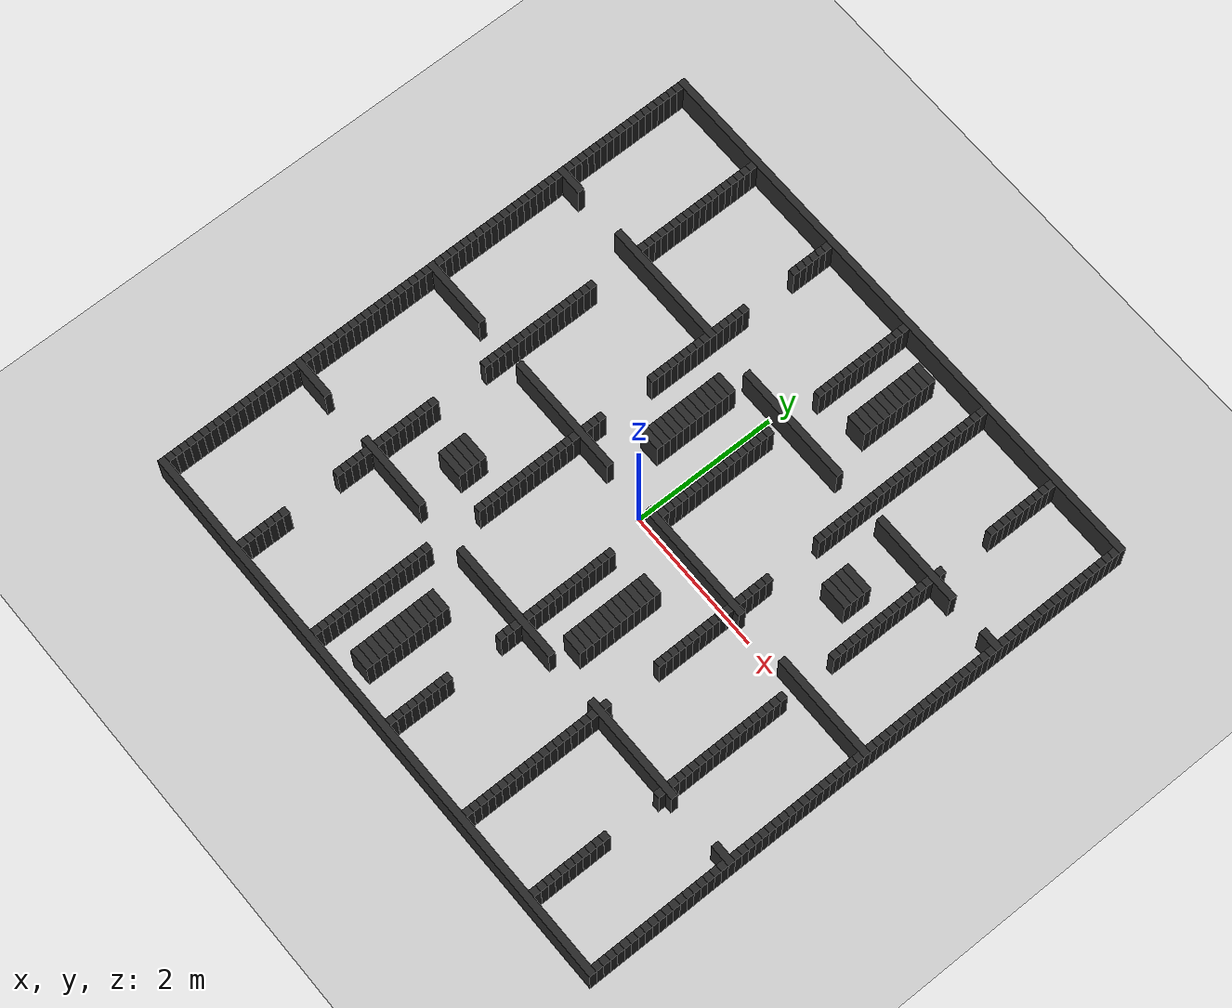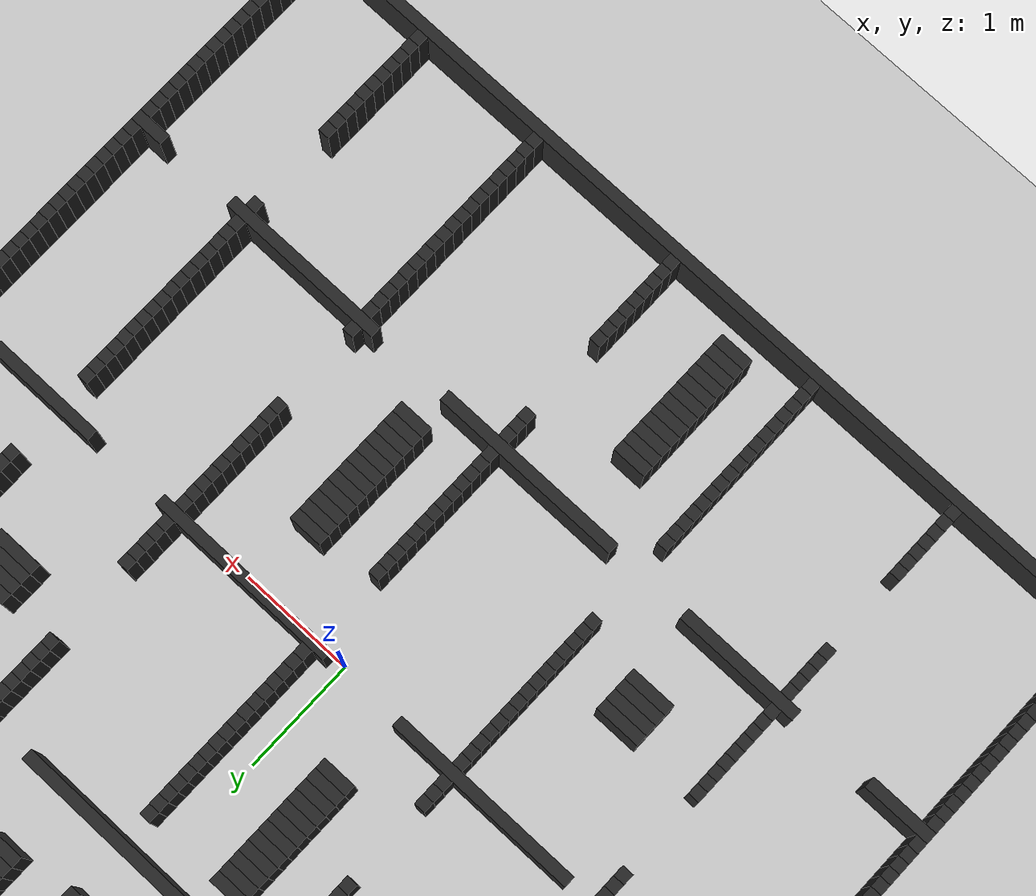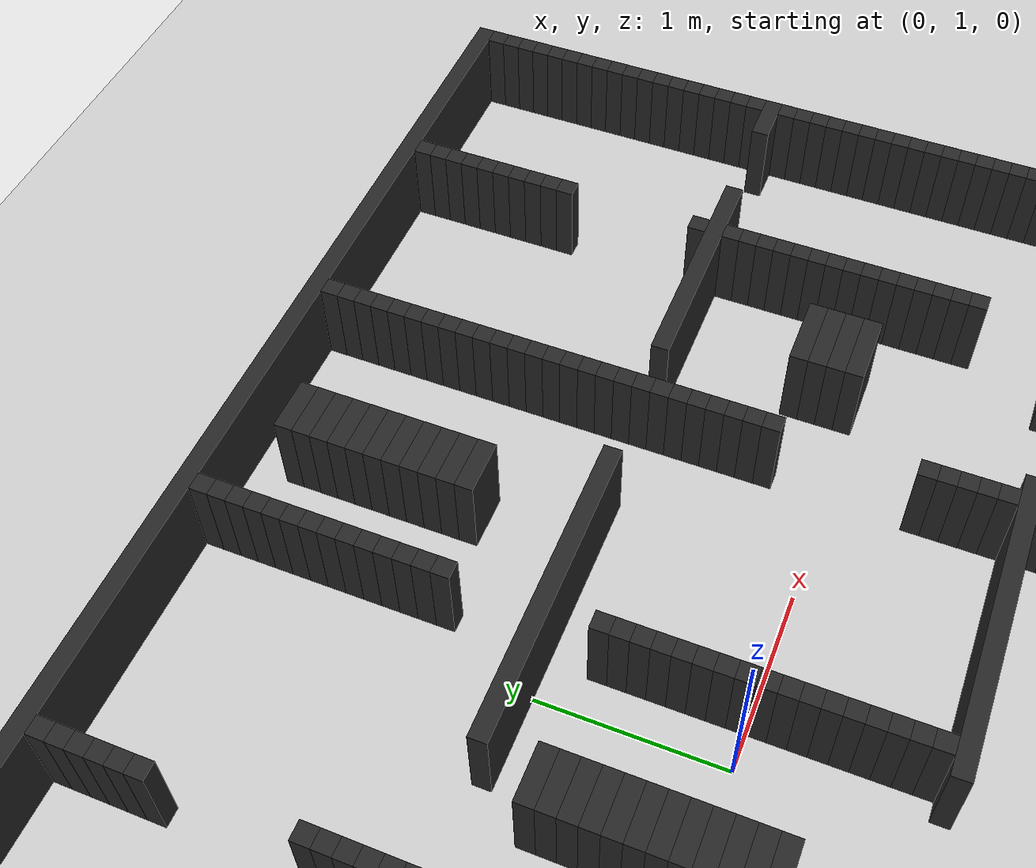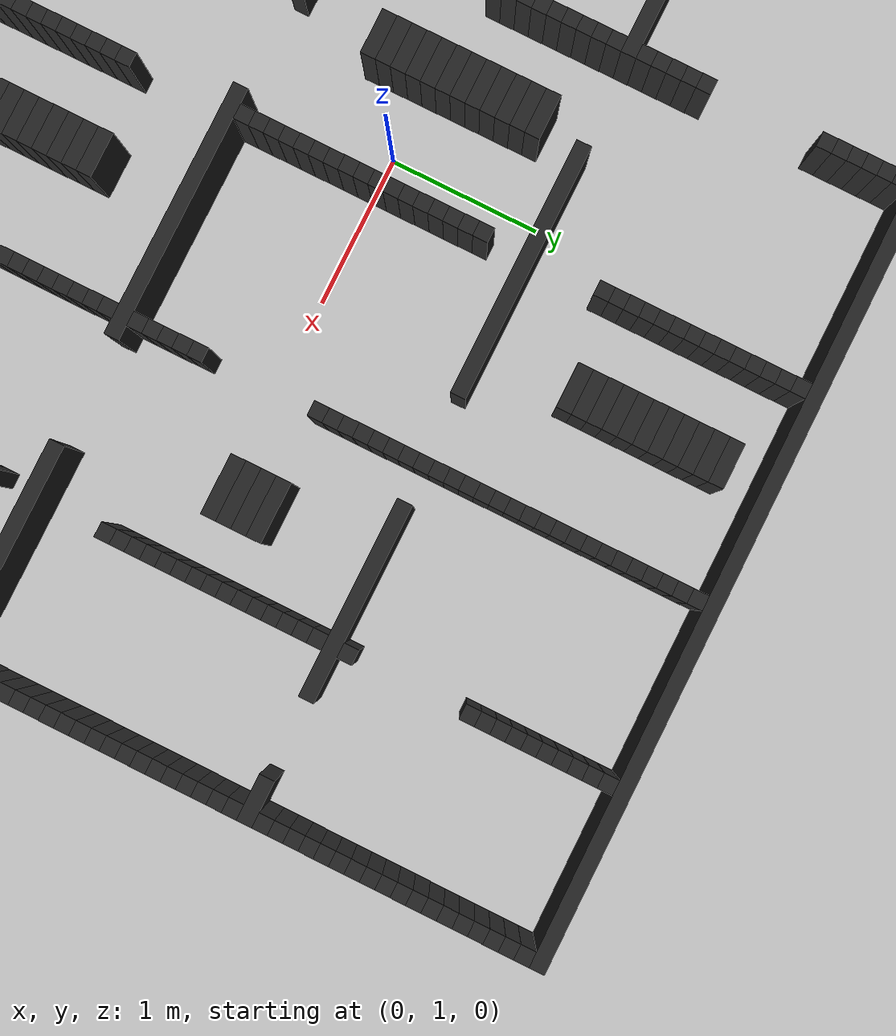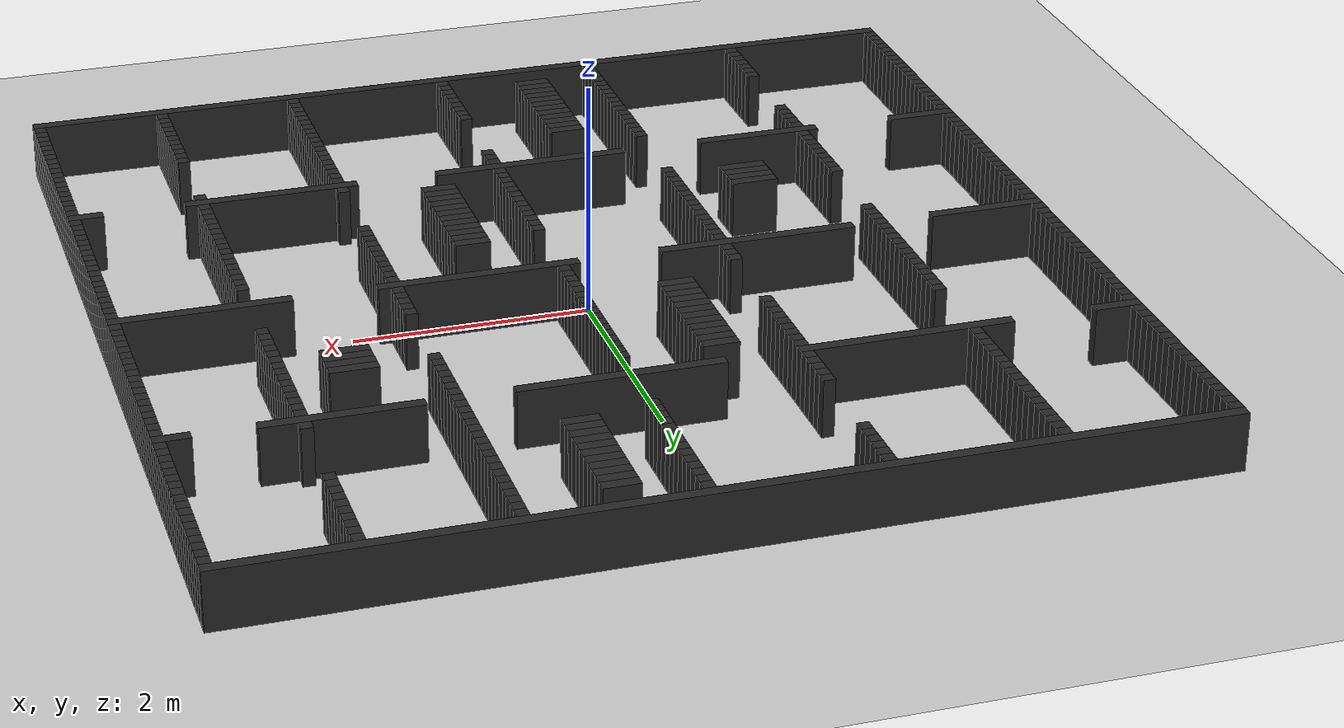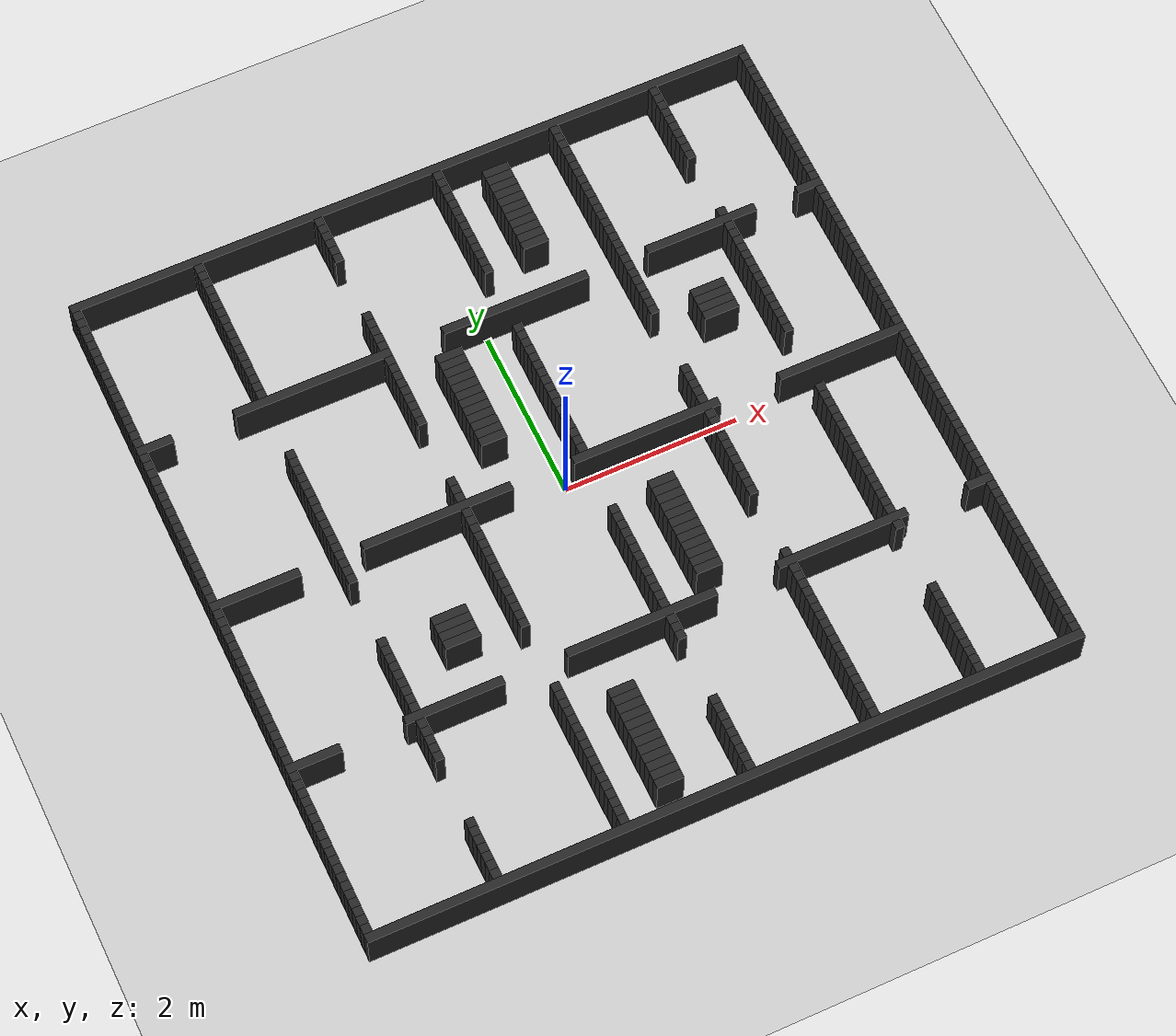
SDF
<?xml version="1.0" ?>
<sdf version="1.6">
  <world name="stress_maze_world">
    <include><uri>model://sun</uri></include>
    <include><uri>model://ground_plane</uri></include>
    <physics type="ode">
      <real_time_update_rate>1000.0</real_time_update_rate>
      <max_step_size>0.001</max_step_size>
      <real_time_factor>1.0</real_time_factor>
    </physics>
    <model name="wall_000_000">
      <static>true</static>
      <pose>0.00000 -3.95000 0.25 0 0 0</pose>
      <link name="link">
        <collision name="collision">
          <geometry><box><size>8.00000 0.10000 0.5</size></box></geometry>
        </collision>
        <visual name="visual">
          <geometry><box><size>8.00000 0.10000 0.5</size></box></geometry>
          <material><ambient>0.12 0.12 0.12 1</ambient><diffuse>0.15 0.15 0.15 1</diffuse></material>
        </visual>
      </link>
    </model>
    <model name="wall_001_000">
      <static>true</static>
      <pose>-3.95000 -3.85000 0.25 0 0 0</pose>
      <link name="link">
        <collision name="collision">
          <geometry><box><size>0.10000 0.10000 0.5</size></box></geometry>
        </collision>
        <visual name="visual">
          <geometry><box><size>0.10000 0.10000 0.5</size></box></geometry>
          <material><ambient>0.12 0.12 0.12 1</ambient><diffuse>0.15 0.15 0.15 1</diffuse></material>
        </visual>
      </link>
    </model>
    <model name="wall_001_014">
      <static>true</static>
      <pose>-2.55000 -3.85000 0.25 0 0 0</pose>
      <link name="link">
        <collision name="collision">
          <geometry><box><size>0.10000 0.10000 0.5</size></box></geometry>
        </collision>
        <visual name="visual">
          <geometry><box><size>0.10000 0.10000 0.5</size></box></geometry>
          <material><ambient>0.12 0.12 0.12 1</ambient><diffuse>0.15 0.15 0.15 1</diffuse></material>
        </visual>
      </link>
    </model>
    <model name="wall_001_028">
      <static>true</static>
      <pose>-1.15000 -3.85000 0.25 0 0 0</pose>
      <link name="link">
        <collision name="collision">
          <geometry><box><size>0.10000 0.10000 0.5</size></box></geometry>
        </collision>
        <visual name="visual">
          <geometry><box><size>0.10000 0.10000 0.5</size></box></geometry>
          <material><ambient>0.12 0.12 0.12 1</ambient><diffuse>0.15 0.15 0.15 1</diffuse></material>
        </visual>
      </link>
    </model>
    <model name="wall_001_042">
      <static>true</static>
      <pose>0.25000 -3.85000 0.25 0 0 0</pose>
      <link name="link">
        <collision name="collision">
          <geometry><box><size>0.10000 0.10000 0.5</size></box></geometry>
        </collision>
        <visual name="visual">
          <geometry><box><size>0.10000 0.10000 0.5</size></box></geometry>
          <material><ambient>0.12 0.12 0.12 1</ambient><diffuse>0.15 0.15 0.15 1</diffuse></material>
        </visual>
      </link>
    </model>
    <model name="wall_001_056">
      <static>true</static>
      <pose>1.65000 -3.85000 0.25 0 0 0</pose>
      <link name="link">
        <collision name="collision">
          <geometry><box><size>0.10000 0.10000 0.5</size></box></geometry>
        </collision>
        <visual name="visual">
          <geometry><box><size>0.10000 0.10000 0.5</size></box></geometry>
          <material><ambient>0.12 0.12 0.12 1</ambient><diffuse>0.15 0.15 0.15 1</diffuse></material>
        </visual>
      </link>
    </model>
    <model name="wall_001_068">
      <static>true</static>
      <pose>2.85000 -3.85000 0.25 0 0 0</pose>
      <link name="link">
        <collision name="collision">
          <geometry><box><size>0.10000 0.10000 0.5</size></box></geometry>
        </collision>
        <visual name="visual">
          <geometry><box><size>0.10000 0.10000 0.5</size></box></geometry>
          <material><ambient>0.12 0.12 0.12 1</ambient><diffuse>0.15 0.15 0.15 1</diffuse></material>
        </visual>
      </link>
    </model>
    <model name="wall_001_079">
      <static>true</static>
      <pose>3.95000 -3.85000 0.25 0 0 0</pose>
      <link name="link">
        <collision name="collision">
          <geometry><box><size>0.10000 0.10000 0.5</size></box></geometry>
        </collision>
        <visual name="visual">
          <geometry><box><size>0.10000 0.10000 0.5</size></box></geometry>
          <material><ambient>0.12 0.12 0.12 1</ambient><diffuse>0.15 0.15 0.15 1</diffuse></material>
        </visual>
      </link>
    </model>
    <model name="wall_002_000">
      <static>true</static>
      <pose>-3.95000 -3.75000 0.25 0 0 0</pose>
      <link name="link">
        <collision name="collision">
          <geometry><box><size>0.10000 0.10000 0.5</size></box></geometry>
        </collision>
        <visual name="visual">
          <geometry><box><size>0.10000 0.10000 0.5</size></box></geometry>
          <material><ambient>0.12 0.12 0.12 1</ambient><diffuse>0.15 0.15 0.15 1</diffuse></material>
        </visual>
      </link>
    </model>
    <model name="wall_002_014">
      <static>true</static>
      <pose>-2.55000 -3.75000 0.25 0 0 0</pose>
      <link name="link">
        <collision name="collision">
          <geometry><box><size>0.10000 0.10000 0.5</size></box></geometry>
        </collision>
        <visual name="visual">
          <geometry><box><size>0.10000 0.10000 0.5</size></box></geometry>
          <material><ambient>0.12 0.12 0.12 1</ambient><diffuse>0.15 0.15 0.15 1</diffuse></material>
        </visual>
      </link>
    </model>
    <model name="wall_002_028">
      <static>true</static>
      <pose>-1.15000 -3.75000 0.25 0 0 0</pose>
      <link name="link">
        <collision name="collision">
          <geometry><box><size>0.10000 0.10000 0.5</size></box></geometry>
        </collision>
        <visual name="visual">
          <geometry><box><size>0.10000 0.10000 0.5</size></box></geometry>
          <material><ambient>0.12 0.12 0.12 1</ambient><diffuse>0.15 0.15 0.15 1</diffuse></material>
        </visual>
      </link>
    </model>
    <model name="wall_002_042">
      <static>true</static>
      <pose>0.25000 -3.75000 0.25 0 0 0</pose>
      <link name="link">
        <collision name="collision">
          <geometry><box><size>0.10000 0.10000 0.5</size></box></geometry>
        </collision>
        <visual name="visual">
          <geometry><box><size>0.10000 0.10000 0.5</size></box></geometry>
          <material><ambient>0.12 0.12 0.12 1</ambient><diffuse>0.15 0.15 0.15 1</diffuse></material>
        </visual>
      </link>
    </model>
    <model name="wall_002_056">
      <static>true</static>
      <pose>1.65000 -3.75000 0.25 0 0 0</pose>
      <link name="link">
        <collision name="collision">
          <geometry><box><size>0.10000 0.10000 0.5</size></box></geometry>
        </collision>
        <visual name="visual">
          <geometry><box><size>0.10000 0.10000 0.5</size></box></geometry>
          <material><ambient>0.12 0.12 0.12 1</ambient><diffuse>0.15 0.15 0.15 1</diffuse></material>
        </visual>
      </link>
    </model>
    <model name="wall_002_068">
      <static>true</static>
      <pose>2.85000 -3.75000 0.25 0 0 0</pose>
      <link name="link">
        <collision name="collision">
          <geometry><box><size>0.10000 0.10000 0.5</size></box></geometry>
        </collision>
        <visual name="visual">
          <geometry><box><size>0.10000 0.10000 0.5</size></box></geometry>
          <material><ambient>0.12 0.12 0.12 1</ambient><diffuse>0.15 0.15 0.15 1</diffuse></material>
        </visual>
      </link>
    </model>
    <model name="wall_002_079">
      <static>true</static>
      <pose>3.95000 -3.75000 0.25 0 0 0</pose>
      <link name="link">
        <collision name="collision">
          <geometry><box><size>0.10000 0.10000 0.5</size></box></geometry>
        </collision>
        <visual name="visual">
          <geometry><box><size>0.10000 0.10000 0.5</size></box></geometry>
          <material><ambient>0.12 0.12 0.12 1</ambient><diffuse>0.15 0.15 0.15 1</diffuse></material>
        </visual>
      </link>
    </model>
    <model name="wall_003_000">
      <static>true</static>
      <pose>-3.95000 -3.65000 0.25 0 0 0</pose>
      <link name="link">
        <collision name="collision">
          <geometry><box><size>0.10000 0.10000 0.5</size></box></geometry>
        </collision>
        <visual name="visual">
          <geometry><box><size>0.10000 0.10000 0.5</size></box></geometry>
          <material><ambient>0.12 0.12 0.12 1</ambient><diffuse>0.15 0.15 0.15 1</diffuse></material>
        </visual>
      </link>
    </model>
    <model name="wall_003_014">
      <static>true</static>
      <pose>-2.55000 -3.65000 0.25 0 0 0</pose>
      <link name="link">
        <collision name="collision">
          <geometry><box><size>0.10000 0.10000 0.5</size></box></geometry>
        </collision>
        <visual name="visual">
          <geometry><box><size>0.10000 0.10000 0.5</size></box></geometry>
          <material><ambient>0.12 0.12 0.12 1</ambient><diffuse>0.15 0.15 0.15 1</diffuse></material>
        </visual>
      </link>
    </model>
    <model name="wall_003_028">
      <static>true</static>
      <pose>-1.15000 -3.65000 0.25 0 0 0</pose>
      <link name="link">
        <collision name="collision">
          <geometry><box><size>0.10000 0.10000 0.5</size></box></geometry>
        </collision>
        <visual name="visual">
          <geometry><box><size>0.10000 0.10000 0.5</size></box></geometry>
          <material><ambient>0.12 0.12 0.12 1</ambient><diffuse>0.15 0.15 0.15 1</diffuse></material>
        </visual>
      </link>
    </model>
    <model name="wall_003_033">
      <static>true</static>
      <pose>-0.55000 -3.65000 0.25 0 0 0</pose>
      <link name="link">
        <collision name="collision">
          <geometry><box><size>0.30000 0.10000 0.5</size></box></geometry>
        </collision>
        <visual name="visual">
          <geometry><box><size>0.30000 0.10000 0.5</size></box></geometry>
          <material><ambient>0.12 0.12 0.12 1</ambient><diffuse>0.15 0.15 0.15 1</diffuse></material>
        </visual>
      </link>
    </model>
    <model name="wall_003_042">
      <static>true</static>
      <pose>0.25000 -3.65000 0.25 0 0 0</pose>
      <link name="link">
        <collision name="collision">
          <geometry><box><size>0.10000 0.10000 0.5</size></box></geometry>
        </collision>
        <visual name="visual">
          <geometry><box><size>0.10000 0.10000 0.5</size></box></geometry>
          <material><ambient>0.12 0.12 0.12 1</ambient><diffuse>0.15 0.15 0.15 1</diffuse></material>
        </visual>
      </link>
    </model>
    <model name="wall_003_056">
      <static>true</static>
      <pose>1.65000 -3.65000 0.25 0 0 0</pose>
      <link name="link">
        <collision name="collision">
          <geometry><box><size>0.10000 0.10000 0.5</size></box></geometry>
        </collision>
        <visual name="visual">
          <geometry><box><size>0.10000 0.10000 0.5</size></box></geometry>
          <material><ambient>0.12 0.12 0.12 1</ambient><diffuse>0.15 0.15 0.15 1</diffuse></material>
        </visual>
      </link>
    </model>
    <model name="wall_003_068">
      <static>true</static>
      <pose>2.85000 -3.65000 0.25 0 0 0</pose>
      <link name="link">
        <collision name="collision">
          <geometry><box><size>0.10000 0.10000 0.5</size></box></geometry>
        </collision>
        <visual name="visual">
          <geometry><box><size>0.10000 0.10000 0.5</size></box></geometry>
          <material><ambient>0.12 0.12 0.12 1</ambient><diffuse>0.15 0.15 0.15 1</diffuse></material>
        </visual>
      </link>
    </model>
    <model name="wall_003_079">
      <static>true</static>
      <pose>3.95000 -3.65000 0.25 0 0 0</pose>
      <link name="link">
        <collision name="collision">
          <geometry><box><size>0.10000 0.10000 0.5</size></box></geometry>
        </collision>
        <visual name="visual">
          <geometry><box><size>0.10000 0.10000 0.5</size></box></geometry>
          <material><ambient>0.12 0.12 0.12 1</ambient><diffuse>0.15 0.15 0.15 1</diffuse></material>
        </visual>
      </link>
    </model>
    <model name="wall_004_000">
      <static>true</static>
      <pose>-3.95000 -3.55000 0.25 0 0 0</pose>
      <link name="link">
        <collision name="collision">
          <geometry><box><size>0.10000 0.10000 0.5</size></box></geometry>
        </collision>
        <visual name="visual">
          <geometry><box><size>0.10000 0.10000 0.5</size></box></geometry>
          <material><ambient>0.12 0.12 0.12 1</ambient><diffuse>0.15 0.15 0.15 1</diffuse></material>
        </visual>
      </link>
    </model>
    <model name="wall_004_014">
      <static>true</static>
      <pose>-2.55000 -3.55000 0.25 0 0 0</pose>
      <link name="link">
        <collision name="collision">
          <geometry><box><size>0.10000 0.10000 0.5</size></box></geometry>
        </collision>
        <visual name="visual">
          <geometry><box><size>0.10000 0.10000 0.5</size></box></geometry>
          <material><ambient>0.12 0.12 0.12 1</ambient><diffuse>0.15 0.15 0.15 1</diffuse></material>
        </visual>
      </link>
    </model>
    <model name="wall_004_028">
      <static>true</static>
      <pose>-1.15000 -3.55000 0.25 0 0 0</pose>
      <link name="link">
        <collision name="collision">
          <geometry><box><size>0.10000 0.10000 0.5</size></box></geometry>
        </collision>
        <visual name="visual">
          <geometry><box><size>0.10000 0.10000 0.5</size></box></geometry>
          <material><ambient>0.12 0.12 0.12 1</ambient><diffuse>0.15 0.15 0.15 1</diffuse></material>
        </visual>
      </link>
    </model>
    <model name="wall_004_033">
      <static>true</static>
      <pose>-0.55000 -3.55000 0.25 0 0 0</pose>
      <link name="link">
        <collision name="collision">
          <geometry><box><size>0.30000 0.10000 0.5</size></box></geometry>
        </collision>
        <visual name="visual">
          <geometry><box><size>0.30000 0.10000 0.5</size></box></geometry>
          <material><ambient>0.12 0.12 0.12 1</ambient><diffuse>0.15 0.15 0.15 1</diffuse></material>
        </visual>
      </link>
    </model>
    <model name="wall_004_042">
      <static>true</static>
      <pose>0.25000 -3.55000 0.25 0 0 0</pose>
      <link name="link">
        <collision name="collision">
          <geometry><box><size>0.10000 0.10000 0.5</size></box></geometry>
        </collision>
        <visual name="visual">
          <geometry><box><size>0.10000 0.10000 0.5</size></box></geometry>
          <material><ambient>0.12 0.12 0.12 1</ambient><diffuse>0.15 0.15 0.15 1</diffuse></material>
        </visual>
      </link>
    </model>
    <model name="wall_004_056">
      <static>true</static>
      <pose>1.65000 -3.55000 0.25 0 0 0</pose>
      <link name="link">
        <collision name="collision">
          <geometry><box><size>0.10000 0.10000 0.5</size></box></geometry>
        </collision>
        <visual name="visual">
          <geometry><box><size>0.10000 0.10000 0.5</size></box></geometry>
          <material><ambient>0.12 0.12 0.12 1</ambient><diffuse>0.15 0.15 0.15 1</diffuse></material>
        </visual>
      </link>
    </model>
    <model name="wall_004_068">
      <static>true</static>
      <pose>2.85000 -3.55000 0.25 0 0 0</pose>
      <link name="link">
        <collision name="collision">
          <geometry><box><size>0.10000 0.10000 0.5</size></box></geometry>
        </collision>
        <visual name="visual">
          <geometry><box><size>0.10000 0.10000 0.5</size></box></geometry>
          <material><ambient>0.12 0.12 0.12 1</ambient><diffuse>0.15 0.15 0.15 1</diffuse></material>
        </visual>
      </link>
    </model>
    <model name="wall_004_079">
      <static>true</static>
      <pose>3.95000 -3.55000 0.25 0 0 0</pose>
      <link name="link">
        <collision name="collision">
          <geometry><box><size>0.10000 0.10000 0.5</size></box></geometry>
        </collision>
        <visual name="visual">
          <geometry><box><size>0.10000 0.10000 0.5</size></box></geometry>
          <material><ambient>0.12 0.12 0.12 1</ambient><diffuse>0.15 0.15 0.15 1</diffuse></material>
        </visual>
      </link>
    </model>
    <model name="wall_005_000">
      <static>true</static>
      <pose>-3.95000 -3.45000 0.25 0 0 0</pose>
      <link name="link">
        <collision name="collision">
          <geometry><box><size>0.10000 0.10000 0.5</size></box></geometry>
        </collision>
        <visual name="visual">
          <geometry><box><size>0.10000 0.10000 0.5</size></box></geometry>
          <material><ambient>0.12 0.12 0.12 1</ambient><diffuse>0.15 0.15 0.15 1</diffuse></material>
        </visual>
      </link>
    </model>
    <model name="wall_005_014">
      <static>true</static>
      <pose>-2.55000 -3.45000 0.25 0 0 0</pose>
      <link name="link">
        <collision name="collision">
          <geometry><box><size>0.10000 0.10000 0.5</size></box></geometry>
        </collision>
        <visual name="visual">
          <geometry><box><size>0.10000 0.10000 0.5</size></box></geometry>
          <material><ambient>0.12 0.12 0.12 1</ambient><diffuse>0.15 0.15 0.15 1</diffuse></material>
        </visual>
      </link>
    </model>
    <model name="wall_005_028">
      <static>true</static>
      <pose>-1.15000 -3.45000 0.25 0 0 0</pose>
      <link name="link">
        <collision name="collision">
          <geometry><box><size>0.10000 0.10000 0.5</size></box></geometry>
        </collision>
        <visual name="visual">
          <geometry><box><size>0.10000 0.10000 0.5</size></box></geometry>
          <material><ambient>0.12 0.12 0.12 1</ambient><diffuse>0.15 0.15 0.15 1</diffuse></material>
        </visual>
      </link>
    </model>
    <model name="wall_005_033">
      <static>true</static>
      <pose>-0.55000 -3.45000 0.25 0 0 0</pose>
      <link name="link">
        <collision name="collision">
          <geometry><box><size>0.30000 0.10000 0.5</size></box></geometry>
        </collision>
        <visual name="visual">
          <geometry><box><size>0.30000 0.10000 0.5</size></box></geometry>
          <material><ambient>0.12 0.12 0.12 1</ambient><diffuse>0.15 0.15 0.15 1</diffuse></material>
        </visual>
      </link>
    </model>
    <model name="wall_005_042">
      <static>true</static>
      <pose>0.25000 -3.45000 0.25 0 0 0</pose>
      <link name="link">
        <collision name="collision">
          <geometry><box><size>0.10000 0.10000 0.5</size></box></geometry>
        </collision>
        <visual name="visual">
          <geometry><box><size>0.10000 0.10000 0.5</size></box></geometry>
          <material><ambient>0.12 0.12 0.12 1</ambient><diffuse>0.15 0.15 0.15 1</diffuse></material>
        </visual>
      </link>
    </model>
    <model name="wall_005_056">
      <static>true</static>
      <pose>1.65000 -3.45000 0.25 0 0 0</pose>
      <link name="link">
        <collision name="collision">
          <geometry><box><size>0.10000 0.10000 0.5</size></box></geometry>
        </collision>
        <visual name="visual">
          <geometry><box><size>0.10000 0.10000 0.5</size></box></geometry>
          <material><ambient>0.12 0.12 0.12 1</ambient><diffuse>0.15 0.15 0.15 1</diffuse></material>
        </visual>
      </link>
    </model>
    <model name="wall_005_068">
      <static>true</static>
      <pose>2.85000 -3.45000 0.25 0 0 0</pose>
      <link name="link">
        <collision name="collision">
          <geometry><box><size>0.10000 0.10000 0.5</size></box></geometry>
        </collision>
        <visual name="visual">
          <geometry><box><size>0.10000 0.10000 0.5</size></box></geometry>
          <material><ambient>0.12 0.12 0.12 1</ambient><diffuse>0.15 0.15 0.15 1</diffuse></material>
        </visual>
      </link>
    </model>
    <model name="wall_005_079">
      <static>true</static>
      <pose>3.95000 -3.45000 0.25 0 0 0</pose>
      <link name="link">
        <collision name="collision">
          <geometry><box><size>0.10000 0.10000 0.5</size></box></geometry>
        </collision>
        <visual name="visual">
          <geometry><box><size>0.10000 0.10000 0.5</size></box></geometry>
          <material><ambient>0.12 0.12 0.12 1</ambient><diffuse>0.15 0.15 0.15 1</diffuse></material>
        </visual>
      </link>
    </model>
    <model name="wall_006_000">
      <static>true</static>
      <pose>-3.95000 -3.35000 0.25 0 0 0</pose>
      <link name="link">
        <collision name="collision">
          <geometry><box><size>0.10000 0.10000 0.5</size></box></geometry>
        </collision>
        <visual name="visual">
          <geometry><box><size>0.10000 0.10000 0.5</size></box></geometry>
          <material><ambient>0.12 0.12 0.12 1</ambient><diffuse>0.15 0.15 0.15 1</diffuse></material>
        </visual>
      </link>
    </model>
    <model name="wall_006_014">
      <static>true</static>
      <pose>-2.55000 -3.35000 0.25 0 0 0</pose>
      <link name="link">
        <collision name="collision">
          <geometry><box><size>0.10000 0.10000 0.5</size></box></geometry>
        </collision>
        <visual name="visual">
          <geometry><box><size>0.10000 0.10000 0.5</size></box></geometry>
          <material><ambient>0.12 0.12 0.12 1</ambient><diffuse>0.15 0.15 0.15 1</diffuse></material>
        </visual>
      </link>
    </model>
    <model name="wall_006_028">
      <static>true</static>
      <pose>-1.15000 -3.35000 0.25 0 0 0</pose>
      <link name="link">
        <collision name="collision">
          <geometry><box><size>0.10000 0.10000 0.5</size></box></geometry>
        </collision>
        <visual name="visual">
          <geometry><box><size>0.10000 0.10000 0.5</size></box></geometry>
          <material><ambient>0.12 0.12 0.12 1</ambient><diffuse>0.15 0.15 0.15 1</diffuse></material>
        </visual>
      </link>
    </model>
    <model name="wall_006_033">
      <static>true</static>
      <pose>-0.55000 -3.35000 0.25 0 0 0</pose>
      <link name="link">
        <collision name="collision">
          <geometry><box><size>0.30000 0.10000 0.5</size></box></geometry>
        </collision>
        <visual name="visual">
          <geometry><box><size>0.30000 0.10000 0.5</size></box></geometry>
          <material><ambient>0.12 0.12 0.12 1</ambient><diffuse>0.15 0.15 0.15 1</diffuse></material>
        </visual>
      </link>
    </model>
    <model name="wall_006_042">
      <static>true</static>
      <pose>0.25000 -3.35000 0.25 0 0 0</pose>
      <link name="link">
        <collision name="collision">
          <geometry><box><size>0.10000 0.10000 0.5</size></box></geometry>
        </collision>
        <visual name="visual">
          <geometry><box><size>0.10000 0.10000 0.5</size></box></geometry>
          <material><ambient>0.12 0.12 0.12 1</ambient><diffuse>0.15 0.15 0.15 1</diffuse></material>
        </visual>
      </link>
    </model>
    <model name="wall_006_056">
      <static>true</static>
      <pose>1.65000 -3.35000 0.25 0 0 0</pose>
      <link name="link">
        <collision name="collision">
          <geometry><box><size>0.10000 0.10000 0.5</size></box></geometry>
        </collision>
        <visual name="visual">
          <geometry><box><size>0.10000 0.10000 0.5</size></box></geometry>
          <material><ambient>0.12 0.12 0.12 1</ambient><diffuse>0.15 0.15 0.15 1</diffuse></material>
        </visual>
      </link>
    </model>
    <model name="wall_006_068">
      <static>true</static>
      <pose>2.85000 -3.35000 0.25 0 0 0</pose>
      <link name="link">
        <collision name="collision">
          <geometry><box><size>0.10000 0.10000 0.5</size></box></geometry>
        </collision>
        <visual name="visual">
          <geometry><box><size>0.10000 0.10000 0.5</size></box></geometry>
          <material><ambient>0.12 0.12 0.12 1</ambient><diffuse>0.15 0.15 0.15 1</diffuse></material>
        </visual>
      </link>
    </model>
    <model name="wall_006_079">
      <static>true</static>
      <pose>3.95000 -3.35000 0.25 0 0 0</pose>
      <link name="link">
        <collision name="collision">
          <geometry><box><size>0.10000 0.10000 0.5</size></box></geometry>
        </collision>
        <visual name="visual">
          <geometry><box><size>0.10000 0.10000 0.5</size></box></geometry>
          <material><ambient>0.12 0.12 0.12 1</ambient><diffuse>0.15 0.15 0.15 1</diffuse></material>
        </visual>
      </link>
    </model>
    <model name="wall_007_000">
      <static>true</static>
      <pose>-3.95000 -3.25000 0.25 0 0 0</pose>
      <link name="link">
        <collision name="collision">
          <geometry><box><size>0.10000 0.10000 0.5</size></box></geometry>
        </collision>
        <visual name="visual">
          <geometry><box><size>0.10000 0.10000 0.5</size></box></geometry>
          <material><ambient>0.12 0.12 0.12 1</ambient><diffuse>0.15 0.15 0.15 1</diffuse></material>
        </visual>
      </link>
    </model>
    <model name="wall_007_014">
      <static>true</static>
      <pose>-2.55000 -3.25000 0.25 0 0 0</pose>
      <link name="link">
        <collision name="collision">
          <geometry><box><size>0.10000 0.10000 0.5</size></box></geometry>
        </collision>
        <visual name="visual">
          <geometry><box><size>0.10000 0.10000 0.5</size></box></geometry>
          <material><ambient>0.12 0.12 0.12 1</ambient><diffuse>0.15 0.15 0.15 1</diffuse></material>
        </visual>
      </link>
    </model>
    <model name="wall_007_028">
      <static>true</static>
      <pose>-1.15000 -3.25000 0.25 0 0 0</pose>
      <link name="link">
        <collision name="collision">
          <geometry><box><size>0.10000 0.10000 0.5</size></box></geometry>
        </collision>
        <visual name="visual">
          <geometry><box><size>0.10000 0.10000 0.5</size></box></geometry>
          <material><ambient>0.12 0.12 0.12 1</ambient><diffuse>0.15 0.15 0.15 1</diffuse></material>
        </visual>
      </link>
    </model>
    <model name="wall_007_033">
      <static>true</static>
      <pose>-0.55000 -3.25000 0.25 0 0 0</pose>
      <link name="link">
        <collision name="collision">
          <geometry><box><size>0.30000 0.10000 0.5</size></box></geometry>
        </collision>
        <visual name="visual">
          <geometry><box><size>0.30000 0.10000 0.5</size></box></geometry>
          <material><ambient>0.12 0.12 0.12 1</ambient><diffuse>0.15 0.15 0.15 1</diffuse></material>
        </visual>
      </link>
    </model>
    <model name="wall_007_042">
      <static>true</static>
      <pose>0.25000 -3.25000 0.25 0 0 0</pose>
      <link name="link">
        <collision name="collision">
          <geometry><box><size>0.10000 0.10000 0.5</size></box></geometry>
        </collision>
        <visual name="visual">
          <geometry><box><size>0.10000 0.10000 0.5</size></box></geometry>
          <material><ambient>0.12 0.12 0.12 1</ambient><diffuse>0.15 0.15 0.15 1</diffuse></material>
        </visual>
      </link>
    </model>
    <model name="wall_007_056">
      <static>true</static>
      <pose>1.65000 -3.25000 0.25 0 0 0</pose>
      <link name="link">
        <collision name="collision">
          <geometry><box><size>0.10000 0.10000 0.5</size></box></geometry>
        </collision>
        <visual name="visual">
          <geometry><box><size>0.10000 0.10000 0.5</size></box></geometry>
          <material><ambient>0.12 0.12 0.12 1</ambient><diffuse>0.15 0.15 0.15 1</diffuse></material>
        </visual>
      </link>
    </model>
    <model name="wall_007_068">
      <static>true</static>
      <pose>2.85000 -3.25000 0.25 0 0 0</pose>
      <link name="link">
        <collision name="collision">
          <geometry><box><size>0.10000 0.10000 0.5</size></box></geometry>
        </collision>
        <visual name="visual">
          <geometry><box><size>0.10000 0.10000 0.5</size></box></geometry>
          <material><ambient>0.12 0.12 0.12 1</ambient><diffuse>0.15 0.15 0.15 1</diffuse></material>
        </visual>
      </link>
    </model>
    <model name="wall_007_079">
      <static>true</static>
      <pose>3.95000 -3.25000 0.25 0 0 0</pose>
      <link name="link">
        <collision name="collision">
          <geometry><box><size>0.10000 0.10000 0.5</size></box></geometry>
        </collision>
        <visual name="visual">
          <geometry><box><size>0.10000 0.10000 0.5</size></box></geometry>
          <material><ambient>0.12 0.12 0.12 1</ambient><diffuse>0.15 0.15 0.15 1</diffuse></material>
        </visual>
      </link>
    </model>
    <model name="wall_008_000">
      <static>true</static>
      <pose>-3.95000 -3.15000 0.25 0 0 0</pose>
      <link name="link">
        <collision name="collision">
          <geometry><box><size>0.10000 0.10000 0.5</size></box></geometry>
        </collision>
        <visual name="visual">
          <geometry><box><size>0.10000 0.10000 0.5</size></box></geometry>
          <material><ambient>0.12 0.12 0.12 1</ambient><diffuse>0.15 0.15 0.15 1</diffuse></material>
        </visual>
      </link>
    </model>
    <model name="wall_008_028">
      <static>true</static>
      <pose>-1.15000 -3.15000 0.25 0 0 0</pose>
      <link name="link">
        <collision name="collision">
          <geometry><box><size>0.10000 0.10000 0.5</size></box></geometry>
        </collision>
        <visual name="visual">
          <geometry><box><size>0.10000 0.10000 0.5</size></box></geometry>
          <material><ambient>0.12 0.12 0.12 1</ambient><diffuse>0.15 0.15 0.15 1</diffuse></material>
        </visual>
      </link>
    </model>
    <model name="wall_008_033">
      <static>true</static>
      <pose>-0.55000 -3.15000 0.25 0 0 0</pose>
      <link name="link">
        <collision name="collision">
          <geometry><box><size>0.30000 0.10000 0.5</size></box></geometry>
        </collision>
        <visual name="visual">
          <geometry><box><size>0.30000 0.10000 0.5</size></box></geometry>
          <material><ambient>0.12 0.12 0.12 1</ambient><diffuse>0.15 0.15 0.15 1</diffuse></material>
        </visual>
      </link>
    </model>
    <model name="wall_008_042">
      <static>true</static>
      <pose>0.25000 -3.15000 0.25 0 0 0</pose>
      <link name="link">
        <collision name="collision">
          <geometry><box><size>0.10000 0.10000 0.5</size></box></geometry>
        </collision>
        <visual name="visual">
          <geometry><box><size>0.10000 0.10000 0.5</size></box></geometry>
          <material><ambient>0.12 0.12 0.12 1</ambient><diffuse>0.15 0.15 0.15 1</diffuse></material>
        </visual>
      </link>
    </model>
    <model name="wall_008_056">
      <static>true</static>
      <pose>1.65000 -3.15000 0.25 0 0 0</pose>
      <link name="link">
        <collision name="collision">
          <geometry><box><size>0.10000 0.10000 0.5</size></box></geometry>
        </collision>
        <visual name="visual">
          <geometry><box><size>0.10000 0.10000 0.5</size></box></geometry>
          <material><ambient>0.12 0.12 0.12 1</ambient><diffuse>0.15 0.15 0.15 1</diffuse></material>
        </visual>
      </link>
    </model>
    <model name="wall_008_068">
      <static>true</static>
      <pose>2.85000 -3.15000 0.25 0 0 0</pose>
      <link name="link">
        <collision name="collision">
          <geometry><box><size>0.10000 0.10000 0.5</size></box></geometry>
        </collision>
        <visual name="visual">
          <geometry><box><size>0.10000 0.10000 0.5</size></box></geometry>
          <material><ambient>0.12 0.12 0.12 1</ambient><diffuse>0.15 0.15 0.15 1</diffuse></material>
        </visual>
      </link>
    </model>
    <model name="wall_008_079">
      <static>true</static>
      <pose>3.95000 -3.15000 0.25 0 0 0</pose>
      <link name="link">
        <collision name="collision">
          <geometry><box><size>0.10000 0.10000 0.5</size></box></geometry>
        </collision>
        <visual name="visual">
          <geometry><box><size>0.10000 0.10000 0.5</size></box></geometry>
          <material><ambient>0.12 0.12 0.12 1</ambient><diffuse>0.15 0.15 0.15 1</diffuse></material>
        </visual>
      </link>
    </model>
    <model name="wall_009_000">
      <static>true</static>
      <pose>-3.95000 -3.05000 0.25 0 0 0</pose>
      <link name="link">
        <collision name="collision">
          <geometry><box><size>0.10000 0.10000 0.5</size></box></geometry>
        </collision>
        <visual name="visual">
          <geometry><box><size>0.10000 0.10000 0.5</size></box></geometry>
          <material><ambient>0.12 0.12 0.12 1</ambient><diffuse>0.15 0.15 0.15 1</diffuse></material>
        </visual>
      </link>
    </model>
    <model name="wall_009_028">
      <static>true</static>
      <pose>-1.15000 -3.05000 0.25 0 0 0</pose>
      <link name="link">
        <collision name="collision">
          <geometry><box><size>0.10000 0.10000 0.5</size></box></geometry>
        </collision>
        <visual name="visual">
          <geometry><box><size>0.10000 0.10000 0.5</size></box></geometry>
          <material><ambient>0.12 0.12 0.12 1</ambient><diffuse>0.15 0.15 0.15 1</diffuse></material>
        </visual>
      </link>
    </model>
    <model name="wall_009_033">
      <static>true</static>
      <pose>-0.55000 -3.05000 0.25 0 0 0</pose>
      <link name="link">
        <collision name="collision">
          <geometry><box><size>0.30000 0.10000 0.5</size></box></geometry>
        </collision>
        <visual name="visual">
          <geometry><box><size>0.30000 0.10000 0.5</size></box></geometry>
          <material><ambient>0.12 0.12 0.12 1</ambient><diffuse>0.15 0.15 0.15 1</diffuse></material>
        </visual>
      </link>
    </model>
    <model name="wall_009_042">
      <static>true</static>
      <pose>0.25000 -3.05000 0.25 0 0 0</pose>
      <link name="link">
        <collision name="collision">
          <geometry><box><size>0.10000 0.10000 0.5</size></box></geometry>
        </collision>
        <visual name="visual">
          <geometry><box><size>0.10000 0.10000 0.5</size></box></geometry>
          <material><ambient>0.12 0.12 0.12 1</ambient><diffuse>0.15 0.15 0.15 1</diffuse></material>
        </visual>
      </link>
    </model>
    <model name="wall_009_056">
      <static>true</static>
      <pose>1.65000 -3.05000 0.25 0 0 0</pose>
      <link name="link">
        <collision name="collision">
          <geometry><box><size>0.10000 0.10000 0.5</size></box></geometry>
        </collision>
        <visual name="visual">
          <geometry><box><size>0.10000 0.10000 0.5</size></box></geometry>
          <material><ambient>0.12 0.12 0.12 1</ambient><diffuse>0.15 0.15 0.15 1</diffuse></material>
        </visual>
      </link>
    </model>
    <model name="wall_009_068">
      <static>true</static>
      <pose>2.85000 -3.05000 0.25 0 0 0</pose>
      <link name="link">
        <collision name="collision">
          <geometry><box><size>0.10000 0.10000 0.5</size></box></geometry>
        </collision>
        <visual name="visual">
          <geometry><box><size>0.10000 0.10000 0.5</size></box></geometry>
          <material><ambient>0.12 0.12 0.12 1</ambient><diffuse>0.15 0.15 0.15 1</diffuse></material>
        </visual>
      </link>
    </model>
    <model name="wall_009_079">
      <static>true</static>
      <pose>3.95000 -3.05000 0.25 0 0 0</pose>
      <link name="link">
        <collision name="collision">
          <geometry><box><size>0.10000 0.10000 0.5</size></box></geometry>
        </collision>
        <visual name="visual">
          <geometry><box><size>0.10000 0.10000 0.5</size></box></geometry>
          <material><ambient>0.12 0.12 0.12 1</ambient><diffuse>0.15 0.15 0.15 1</diffuse></material>
        </visual>
      </link>
    </model>
    <model name="wall_010_000">
      <static>true</static>
      <pose>-3.95000 -2.95000 0.25 0 0 0</pose>
      <link name="link">
        <collision name="collision">
          <geometry><box><size>0.10000 0.10000 0.5</size></box></geometry>
        </collision>
        <visual name="visual">
          <geometry><box><size>0.10000 0.10000 0.5</size></box></geometry>
          <material><ambient>0.12 0.12 0.12 1</ambient><diffuse>0.15 0.15 0.15 1</diffuse></material>
        </visual>
      </link>
    </model>
    <model name="wall_010_028">
      <static>true</static>
      <pose>-1.15000 -2.95000 0.25 0 0 0</pose>
      <link name="link">
        <collision name="collision">
          <geometry><box><size>0.10000 0.10000 0.5</size></box></geometry>
        </collision>
        <visual name="visual">
          <geometry><box><size>0.10000 0.10000 0.5</size></box></geometry>
          <material><ambient>0.12 0.12 0.12 1</ambient><diffuse>0.15 0.15 0.15 1</diffuse></material>
        </visual>
      </link>
    </model>
    <model name="wall_010_033">
      <static>true</static>
      <pose>-0.55000 -2.95000 0.25 0 0 0</pose>
      <link name="link">
        <collision name="collision">
          <geometry><box><size>0.30000 0.10000 0.5</size></box></geometry>
        </collision>
        <visual name="visual">
          <geometry><box><size>0.30000 0.10000 0.5</size></box></geometry>
          <material><ambient>0.12 0.12 0.12 1</ambient><diffuse>0.15 0.15 0.15 1</diffuse></material>
        </visual>
      </link>
    </model>
    <model name="wall_010_056">
      <static>true</static>
      <pose>1.65000 -2.95000 0.25 0 0 0</pose>
      <link name="link">
        <collision name="collision">
          <geometry><box><size>0.10000 0.10000 0.5</size></box></geometry>
        </collision>
        <visual name="visual">
          <geometry><box><size>0.10000 0.10000 0.5</size></box></geometry>
          <material><ambient>0.12 0.12 0.12 1</ambient><diffuse>0.15 0.15 0.15 1</diffuse></material>
        </visual>
      </link>
    </model>
    <model name="wall_010_068">
      <static>true</static>
      <pose>2.85000 -2.95000 0.25 0 0 0</pose>
      <link name="link">
        <collision name="collision">
          <geometry><box><size>0.10000 0.10000 0.5</size></box></geometry>
        </collision>
        <visual name="visual">
          <geometry><box><size>0.10000 0.10000 0.5</size></box></geometry>
          <material><ambient>0.12 0.12 0.12 1</ambient><diffuse>0.15 0.15 0.15 1</diffuse></material>
        </visual>
      </link>
    </model>
    <model name="wall_010_079">
      <static>true</static>
      <pose>3.95000 -2.95000 0.25 0 0 0</pose>
      <link name="link">
        <collision name="collision">
          <geometry><box><size>0.10000 0.10000 0.5</size></box></geometry>
        </collision>
        <visual name="visual">
          <geometry><box><size>0.10000 0.10000 0.5</size></box></geometry>
          <material><ambient>0.12 0.12 0.12 1</ambient><diffuse>0.15 0.15 0.15 1</diffuse></material>
        </visual>
      </link>
    </model>
    <model name="wall_011_000">
      <static>true</static>
      <pose>-3.95000 -2.85000 0.25 0 0 0</pose>
      <link name="link">
        <collision name="collision">
          <geometry><box><size>0.10000 0.10000 0.5</size></box></geometry>
        </collision>
        <visual name="visual">
          <geometry><box><size>0.10000 0.10000 0.5</size></box></geometry>
          <material><ambient>0.12 0.12 0.12 1</ambient><diffuse>0.15 0.15 0.15 1</diffuse></material>
        </visual>
      </link>
    </model>
    <model name="wall_011_028">
      <static>true</static>
      <pose>-1.15000 -2.85000 0.25 0 0 0</pose>
      <link name="link">
        <collision name="collision">
          <geometry><box><size>0.10000 0.10000 0.5</size></box></geometry>
        </collision>
        <visual name="visual">
          <geometry><box><size>0.10000 0.10000 0.5</size></box></geometry>
          <material><ambient>0.12 0.12 0.12 1</ambient><diffuse>0.15 0.15 0.15 1</diffuse></material>
        </visual>
      </link>
    </model>
    <model name="wall_011_033">
      <static>true</static>
      <pose>-0.55000 -2.85000 0.25 0 0 0</pose>
      <link name="link">
        <collision name="collision">
          <geometry><box><size>0.30000 0.10000 0.5</size></box></geometry>
        </collision>
        <visual name="visual">
          <geometry><box><size>0.30000 0.10000 0.5</size></box></geometry>
          <material><ambient>0.12 0.12 0.12 1</ambient><diffuse>0.15 0.15 0.15 1</diffuse></material>
        </visual>
      </link>
    </model>
    <model name="wall_011_056">
      <static>true</static>
      <pose>1.65000 -2.85000 0.25 0 0 0</pose>
      <link name="link">
        <collision name="collision">
          <geometry><box><size>0.10000 0.10000 0.5</size></box></geometry>
        </collision>
        <visual name="visual">
          <geometry><box><size>0.10000 0.10000 0.5</size></box></geometry>
          <material><ambient>0.12 0.12 0.12 1</ambient><diffuse>0.15 0.15 0.15 1</diffuse></material>
        </visual>
      </link>
    </model>
    <model name="wall_011_068">
      <static>true</static>
      <pose>2.85000 -2.85000 0.25 0 0 0</pose>
      <link name="link">
        <collision name="collision">
          <geometry><box><size>0.10000 0.10000 0.5</size></box></geometry>
        </collision>
        <visual name="visual">
          <geometry><box><size>0.10000 0.10000 0.5</size></box></geometry>
          <material><ambient>0.12 0.12 0.12 1</ambient><diffuse>0.15 0.15 0.15 1</diffuse></material>
        </visual>
      </link>
    </model>
    <model name="wall_011_079">
      <static>true</static>
      <pose>3.95000 -2.85000 0.25 0 0 0</pose>
      <link name="link">
        <collision name="collision">
          <geometry><box><size>0.10000 0.10000 0.5</size></box></geometry>
        </collision>
        <visual name="visual">
          <geometry><box><size>0.10000 0.10000 0.5</size></box></geometry>
          <material><ambient>0.12 0.12 0.12 1</ambient><diffuse>0.15 0.15 0.15 1</diffuse></material>
        </visual>
      </link>
    </model>
    <model name="wall_012_000">
      <static>true</static>
      <pose>-3.95000 -2.75000 0.25 0 0 0</pose>
      <link name="link">
        <collision name="collision">
          <geometry><box><size>0.10000 0.10000 0.5</size></box></geometry>
        </collision>
        <visual name="visual">
          <geometry><box><size>0.10000 0.10000 0.5</size></box></geometry>
          <material><ambient>0.12 0.12 0.12 1</ambient><diffuse>0.15 0.15 0.15 1</diffuse></material>
        </visual>
      </link>
    </model>
    <model name="wall_012_028">
      <static>true</static>
      <pose>-1.15000 -2.75000 0.25 0 0 0</pose>
      <link name="link">
        <collision name="collision">
          <geometry><box><size>0.10000 0.10000 0.5</size></box></geometry>
        </collision>
        <visual name="visual">
          <geometry><box><size>0.10000 0.10000 0.5</size></box></geometry>
          <material><ambient>0.12 0.12 0.12 1</ambient><diffuse>0.15 0.15 0.15 1</diffuse></material>
        </visual>
      </link>
    </model>
    <model name="wall_012_033">
      <static>true</static>
      <pose>-0.55000 -2.75000 0.25 0 0 0</pose>
      <link name="link">
        <collision name="collision">
          <geometry><box><size>0.30000 0.10000 0.5</size></box></geometry>
        </collision>
        <visual name="visual">
          <geometry><box><size>0.30000 0.10000 0.5</size></box></geometry>
          <material><ambient>0.12 0.12 0.12 1</ambient><diffuse>0.15 0.15 0.15 1</diffuse></material>
        </visual>
      </link>
    </model>
    <model name="wall_012_056">
      <static>true</static>
      <pose>1.65000 -2.75000 0.25 0 0 0</pose>
      <link name="link">
        <collision name="collision">
          <geometry><box><size>0.10000 0.10000 0.5</size></box></geometry>
        </collision>
        <visual name="visual">
          <geometry><box><size>0.10000 0.10000 0.5</size></box></geometry>
          <material><ambient>0.12 0.12 0.12 1</ambient><diffuse>0.15 0.15 0.15 1</diffuse></material>
        </visual>
      </link>
    </model>
    <model name="wall_012_079">
      <static>true</static>
      <pose>3.95000 -2.75000 0.25 0 0 0</pose>
      <link name="link">
        <collision name="collision">
          <geometry><box><size>0.10000 0.10000 0.5</size></box></geometry>
        </collision>
        <visual name="visual">
          <geometry><box><size>0.10000 0.10000 0.5</size></box></geometry>
          <material><ambient>0.12 0.12 0.12 1</ambient><diffuse>0.15 0.15 0.15 1</diffuse></material>
        </visual>
      </link>
    </model>
    <model name="wall_013_000">
      <static>true</static>
      <pose>-3.95000 -2.65000 0.25 0 0 0</pose>
      <link name="link">
        <collision name="collision">
          <geometry><box><size>0.10000 0.10000 0.5</size></box></geometry>
        </collision>
        <visual name="visual">
          <geometry><box><size>0.10000 0.10000 0.5</size></box></geometry>
          <material><ambient>0.12 0.12 0.12 1</ambient><diffuse>0.15 0.15 0.15 1</diffuse></material>
        </visual>
      </link>
    </model>
    <model name="wall_013_028">
      <static>true</static>
      <pose>-1.15000 -2.65000 0.25 0 0 0</pose>
      <link name="link">
        <collision name="collision">
          <geometry><box><size>0.10000 0.10000 0.5</size></box></geometry>
        </collision>
        <visual name="visual">
          <geometry><box><size>0.10000 0.10000 0.5</size></box></geometry>
          <material><ambient>0.12 0.12 0.12 1</ambient><diffuse>0.15 0.15 0.15 1</diffuse></material>
        </visual>
      </link>
    </model>
    <model name="wall_013_033">
      <static>true</static>
      <pose>-0.55000 -2.65000 0.25 0 0 0</pose>
      <link name="link">
        <collision name="collision">
          <geometry><box><size>0.30000 0.10000 0.5</size></box></geometry>
        </collision>
        <visual name="visual">
          <geometry><box><size>0.30000 0.10000 0.5</size></box></geometry>
          <material><ambient>0.12 0.12 0.12 1</ambient><diffuse>0.15 0.15 0.15 1</diffuse></material>
        </visual>
      </link>
    </model>
    <model name="wall_013_056">
      <static>true</static>
      <pose>1.65000 -2.65000 0.25 0 0 0</pose>
      <link name="link">
        <collision name="collision">
          <geometry><box><size>0.10000 0.10000 0.5</size></box></geometry>
        </collision>
        <visual name="visual">
          <geometry><box><size>0.10000 0.10000 0.5</size></box></geometry>
          <material><ambient>0.12 0.12 0.12 1</ambient><diffuse>0.15 0.15 0.15 1</diffuse></material>
        </visual>
      </link>
    </model>
    <model name="wall_013_079">
      <static>true</static>
      <pose>3.95000 -2.65000 0.25 0 0 0</pose>
      <link name="link">
        <collision name="collision">
          <geometry><box><size>0.10000 0.10000 0.5</size></box></geometry>
        </collision>
        <visual name="visual">
          <geometry><box><size>0.10000 0.10000 0.5</size></box></geometry>
          <material><ambient>0.12 0.12 0.12 1</ambient><diffuse>0.15 0.15 0.15 1</diffuse></material>
        </visual>
      </link>
    </model>
    <model name="wall_014_000">
      <static>true</static>
      <pose>-3.95000 -2.55000 0.25 0 0 0</pose>
      <link name="link">
        <collision name="collision">
          <geometry><box><size>0.10000 0.10000 0.5</size></box></geometry>
        </collision>
        <visual name="visual">
          <geometry><box><size>0.10000 0.10000 0.5</size></box></geometry>
          <material><ambient>0.12 0.12 0.12 1</ambient><diffuse>0.15 0.15 0.15 1</diffuse></material>
        </visual>
      </link>
    </model>
    <model name="wall_014_028">
      <static>true</static>
      <pose>-1.15000 -2.55000 0.25 0 0 0</pose>
      <link name="link">
        <collision name="collision">
          <geometry><box><size>0.10000 0.10000 0.5</size></box></geometry>
        </collision>
        <visual name="visual">
          <geometry><box><size>0.10000 0.10000 0.5</size></box></geometry>
          <material><ambient>0.12 0.12 0.12 1</ambient><diffuse>0.15 0.15 0.15 1</diffuse></material>
        </visual>
      </link>
    </model>
    <model name="wall_014_033">
      <static>true</static>
      <pose>-0.55000 -2.55000 0.25 0 0 0</pose>
      <link name="link">
        <collision name="collision">
          <geometry><box><size>0.30000 0.10000 0.5</size></box></geometry>
        </collision>
        <visual name="visual">
          <geometry><box><size>0.30000 0.10000 0.5</size></box></geometry>
          <material><ambient>0.12 0.12 0.12 1</ambient><diffuse>0.15 0.15 0.15 1</diffuse></material>
        </visual>
      </link>
    </model>
    <model name="wall_014_056">
      <static>true</static>
      <pose>1.65000 -2.55000 0.25 0 0 0</pose>
      <link name="link">
        <collision name="collision">
          <geometry><box><size>0.10000 0.10000 0.5</size></box></geometry>
        </collision>
        <visual name="visual">
          <geometry><box><size>0.10000 0.10000 0.5</size></box></geometry>
          <material><ambient>0.12 0.12 0.12 1</ambient><diffuse>0.15 0.15 0.15 1</diffuse></material>
        </visual>
      </link>
    </model>
    <model name="wall_014_079">
      <static>true</static>
      <pose>3.95000 -2.55000 0.25 0 0 0</pose>
      <link name="link">
        <collision name="collision">
          <geometry><box><size>0.10000 0.10000 0.5</size></box></geometry>
        </collision>
        <visual name="visual">
          <geometry><box><size>0.10000 0.10000 0.5</size></box></geometry>
          <material><ambient>0.12 0.12 0.12 1</ambient><diffuse>0.15 0.15 0.15 1</diffuse></material>
        </visual>
      </link>
    </model>
    <model name="wall_015_000">
      <static>true</static>
      <pose>-3.95000 -2.45000 0.25 0 0 0</pose>
      <link name="link">
        <collision name="collision">
          <geometry><box><size>0.10000 0.10000 0.5</size></box></geometry>
        </collision>
        <visual name="visual">
          <geometry><box><size>0.10000 0.10000 0.5</size></box></geometry>
          <material><ambient>0.12 0.12 0.12 1</ambient><diffuse>0.15 0.15 0.15 1</diffuse></material>
        </visual>
      </link>
    </model>
    <model name="wall_015_014">
      <static>true</static>
      <pose>-2.55000 -2.45000 0.25 0 0 0</pose>
      <link name="link">
        <collision name="collision">
          <geometry><box><size>0.10000 0.10000 0.5</size></box></geometry>
        </collision>
        <visual name="visual">
          <geometry><box><size>0.10000 0.10000 0.5</size></box></geometry>
          <material><ambient>0.12 0.12 0.12 1</ambient><diffuse>0.15 0.15 0.15 1</diffuse></material>
        </visual>
      </link>
    </model>
    <model name="wall_015_028">
      <static>true</static>
      <pose>-1.15000 -2.45000 0.25 0 0 0</pose>
      <link name="link">
        <collision name="collision">
          <geometry><box><size>0.10000 0.10000 0.5</size></box></geometry>
        </collision>
        <visual name="visual">
          <geometry><box><size>0.10000 0.10000 0.5</size></box></geometry>
          <material><ambient>0.12 0.12 0.12 1</ambient><diffuse>0.15 0.15 0.15 1</diffuse></material>
        </visual>
      </link>
    </model>
    <model name="wall_015_056">
      <static>true</static>
      <pose>1.65000 -2.45000 0.25 0 0 0</pose>
      <link name="link">
        <collision name="collision">
          <geometry><box><size>0.10000 0.10000 0.5</size></box></geometry>
        </collision>
        <visual name="visual">
          <geometry><box><size>0.10000 0.10000 0.5</size></box></geometry>
          <material><ambient>0.12 0.12 0.12 1</ambient><diffuse>0.15 0.15 0.15 1</diffuse></material>
        </visual>
      </link>
    </model>
    <model name="wall_015_079">
      <static>true</static>
      <pose>3.95000 -2.45000 0.25 0 0 0</pose>
      <link name="link">
        <collision name="collision">
          <geometry><box><size>0.10000 0.10000 0.5</size></box></geometry>
        </collision>
        <visual name="visual">
          <geometry><box><size>0.10000 0.10000 0.5</size></box></geometry>
          <material><ambient>0.12 0.12 0.12 1</ambient><diffuse>0.15 0.15 0.15 1</diffuse></material>
        </visual>
      </link>
    </model>
    <model name="wall_016_000">
      <static>true</static>
      <pose>-3.95000 -2.35000 0.25 0 0 0</pose>
      <link name="link">
        <collision name="collision">
          <geometry><box><size>0.10000 0.10000 0.5</size></box></geometry>
        </collision>
        <visual name="visual">
          <geometry><box><size>0.10000 0.10000 0.5</size></box></geometry>
          <material><ambient>0.12 0.12 0.12 1</ambient><diffuse>0.15 0.15 0.15 1</diffuse></material>
        </visual>
      </link>
    </model>
    <model name="wall_016_014">
      <static>true</static>
      <pose>-2.55000 -2.35000 0.25 0 0 0</pose>
      <link name="link">
        <collision name="collision">
          <geometry><box><size>0.10000 0.10000 0.5</size></box></geometry>
        </collision>
        <visual name="visual">
          <geometry><box><size>0.10000 0.10000 0.5</size></box></geometry>
          <material><ambient>0.12 0.12 0.12 1</ambient><diffuse>0.15 0.15 0.15 1</diffuse></material>
        </visual>
      </link>
    </model>
    <model name="wall_016_028">
      <static>true</static>
      <pose>-1.15000 -2.35000 0.25 0 0 0</pose>
      <link name="link">
        <collision name="collision">
          <geometry><box><size>0.10000 0.10000 0.5</size></box></geometry>
        </collision>
        <visual name="visual">
          <geometry><box><size>0.10000 0.10000 0.5</size></box></geometry>
          <material><ambient>0.12 0.12 0.12 1</ambient><diffuse>0.15 0.15 0.15 1</diffuse></material>
        </visual>
      </link>
    </model>
    <model name="wall_016_056">
      <static>true</static>
      <pose>1.65000 -2.35000 0.25 0 0 0</pose>
      <link name="link">
        <collision name="collision">
          <geometry><box><size>0.10000 0.10000 0.5</size></box></geometry>
        </collision>
        <visual name="visual">
          <geometry><box><size>0.10000 0.10000 0.5</size></box></geometry>
          <material><ambient>0.12 0.12 0.12 1</ambient><diffuse>0.15 0.15 0.15 1</diffuse></material>
        </visual>
      </link>
    </model>
    <model name="wall_016_079">
      <static>true</static>
      <pose>3.95000 -2.35000 0.25 0 0 0</pose>
      <link name="link">
        <collision name="collision">
          <geometry><box><size>0.10000 0.10000 0.5</size></box></geometry>
        </collision>
        <visual name="visual">
          <geometry><box><size>0.10000 0.10000 0.5</size></box></geometry>
          <material><ambient>0.12 0.12 0.12 1</ambient><diffuse>0.15 0.15 0.15 1</diffuse></material>
        </visual>
      </link>
    </model>
    <model name="wall_017_000">
      <static>true</static>
      <pose>-3.95000 -2.25000 0.25 0 0 0</pose>
      <link name="link">
        <collision name="collision">
          <geometry><box><size>0.10000 0.10000 0.5</size></box></geometry>
        </collision>
        <visual name="visual">
          <geometry><box><size>0.10000 0.10000 0.5</size></box></geometry>
          <material><ambient>0.12 0.12 0.12 1</ambient><diffuse>0.15 0.15 0.15 1</diffuse></material>
        </visual>
      </link>
    </model>
    <model name="wall_017_014">
      <static>true</static>
      <pose>-2.55000 -2.25000 0.25 0 0 0</pose>
      <link name="link">
        <collision name="collision">
          <geometry><box><size>0.10000 0.10000 0.5</size></box></geometry>
        </collision>
        <visual name="visual">
          <geometry><box><size>0.10000 0.10000 0.5</size></box></geometry>
          <material><ambient>0.12 0.12 0.12 1</ambient><diffuse>0.15 0.15 0.15 1</diffuse></material>
        </visual>
      </link>
    </model>
    <model name="wall_017_028">
      <static>true</static>
      <pose>-1.15000 -2.25000 0.25 0 0 0</pose>
      <link name="link">
        <collision name="collision">
          <geometry><box><size>0.10000 0.10000 0.5</size></box></geometry>
        </collision>
        <visual name="visual">
          <geometry><box><size>0.10000 0.10000 0.5</size></box></geometry>
          <material><ambient>0.12 0.12 0.12 1</ambient><diffuse>0.15 0.15 0.15 1</diffuse></material>
        </visual>
      </link>
    </model>
    <model name="wall_017_042">
      <static>true</static>
      <pose>0.25000 -2.25000 0.25 0 0 0</pose>
      <link name="link">
        <collision name="collision">
          <geometry><box><size>0.10000 0.10000 0.5</size></box></geometry>
        </collision>
        <visual name="visual">
          <geometry><box><size>0.10000 0.10000 0.5</size></box></geometry>
          <material><ambient>0.12 0.12 0.12 1</ambient><diffuse>0.15 0.15 0.15 1</diffuse></material>
        </visual>
      </link>
    </model>
    <model name="wall_017_056">
      <static>true</static>
      <pose>1.65000 -2.25000 0.25 0 0 0</pose>
      <link name="link">
        <collision name="collision">
          <geometry><box><size>0.10000 0.10000 0.5</size></box></geometry>
        </collision>
        <visual name="visual">
          <geometry><box><size>0.10000 0.10000 0.5</size></box></geometry>
          <material><ambient>0.12 0.12 0.12 1</ambient><diffuse>0.15 0.15 0.15 1</diffuse></material>
        </visual>
      </link>
    </model>
    <model name="wall_017_079">
      <static>true</static>
      <pose>3.95000 -2.25000 0.25 0 0 0</pose>
      <link name="link">
        <collision name="collision">
          <geometry><box><size>0.10000 0.10000 0.5</size></box></geometry>
        </collision>
        <visual name="visual">
          <geometry><box><size>0.10000 0.10000 0.5</size></box></geometry>
          <material><ambient>0.12 0.12 0.12 1</ambient><diffuse>0.15 0.15 0.15 1</diffuse></material>
        </visual>
      </link>
    </model>
    <model name="wall_018_000">
      <static>true</static>
      <pose>-3.95000 -2.15000 0.25 0 0 0</pose>
      <link name="link">
        <collision name="collision">
          <geometry><box><size>0.10000 0.10000 0.5</size></box></geometry>
        </collision>
        <visual name="visual">
          <geometry><box><size>0.10000 0.10000 0.5</size></box></geometry>
          <material><ambient>0.12 0.12 0.12 1</ambient><diffuse>0.15 0.15 0.15 1</diffuse></material>
        </visual>
      </link>
    </model>
    <model name="wall_018_014">
      <static>true</static>
      <pose>-2.55000 -2.15000 0.25 0 0 0</pose>
      <link name="link">
        <collision name="collision">
          <geometry><box><size>0.10000 0.10000 0.5</size></box></geometry>
        </collision>
        <visual name="visual">
          <geometry><box><size>0.10000 0.10000 0.5</size></box></geometry>
          <material><ambient>0.12 0.12 0.12 1</ambient><diffuse>0.15 0.15 0.15 1</diffuse></material>
        </visual>
      </link>
    </model>
    <model name="wall_018_042">
      <static>true</static>
      <pose>0.25000 -2.15000 0.25 0 0 0</pose>
      <link name="link">
        <collision name="collision">
          <geometry><box><size>0.10000 0.10000 0.5</size></box></geometry>
        </collision>
        <visual name="visual">
          <geometry><box><size>0.10000 0.10000 0.5</size></box></geometry>
          <material><ambient>0.12 0.12 0.12 1</ambient><diffuse>0.15 0.15 0.15 1</diffuse></material>
        </visual>
      </link>
    </model>
    <model name="wall_018_056">
      <static>true</static>
      <pose>1.65000 -2.15000 0.25 0 0 0</pose>
      <link name="link">
        <collision name="collision">
          <geometry><box><size>0.10000 0.10000 0.5</size></box></geometry>
        </collision>
        <visual name="visual">
          <geometry><box><size>0.10000 0.10000 0.5</size></box></geometry>
          <material><ambient>0.12 0.12 0.12 1</ambient><diffuse>0.15 0.15 0.15 1</diffuse></material>
        </visual>
      </link>
    </model>
    <model name="wall_018_079">
      <static>true</static>
      <pose>3.95000 -2.15000 0.25 0 0 0</pose>
      <link name="link">
        <collision name="collision">
          <geometry><box><size>0.10000 0.10000 0.5</size></box></geometry>
        </collision>
        <visual name="visual">
          <geometry><box><size>0.10000 0.10000 0.5</size></box></geometry>
          <material><ambient>0.12 0.12 0.12 1</ambient><diffuse>0.15 0.15 0.15 1</diffuse></material>
        </visual>
      </link>
    </model>
    <model name="wall_019_000">
      <static>true</static>
      <pose>-3.95000 -2.05000 0.25 0 0 0</pose>
      <link name="link">
        <collision name="collision">
          <geometry><box><size>0.10000 0.10000 0.5</size></box></geometry>
        </collision>
        <visual name="visual">
          <geometry><box><size>0.10000 0.10000 0.5</size></box></geometry>
          <material><ambient>0.12 0.12 0.12 1</ambient><diffuse>0.15 0.15 0.15 1</diffuse></material>
        </visual>
      </link>
    </model>
    <model name="wall_019_014">
      <static>true</static>
      <pose>-2.55000 -2.05000 0.25 0 0 0</pose>
      <link name="link">
        <collision name="collision">
          <geometry><box><size>0.10000 0.10000 0.5</size></box></geometry>
        </collision>
        <visual name="visual">
          <geometry><box><size>0.10000 0.10000 0.5</size></box></geometry>
          <material><ambient>0.12 0.12 0.12 1</ambient><diffuse>0.15 0.15 0.15 1</diffuse></material>
        </visual>
      </link>
    </model>
    <model name="wall_019_042">
      <static>true</static>
      <pose>0.25000 -2.05000 0.25 0 0 0</pose>
      <link name="link">
        <collision name="collision">
          <geometry><box><size>0.10000 0.10000 0.5</size></box></geometry>
        </collision>
        <visual name="visual">
          <geometry><box><size>0.10000 0.10000 0.5</size></box></geometry>
          <material><ambient>0.12 0.12 0.12 1</ambient><diffuse>0.15 0.15 0.15 1</diffuse></material>
        </visual>
      </link>
    </model>
    <model name="wall_019_056">
      <static>true</static>
      <pose>1.65000 -2.05000 0.25 0 0 0</pose>
      <link name="link">
        <collision name="collision">
          <geometry><box><size>0.10000 0.10000 0.5</size></box></geometry>
        </collision>
        <visual name="visual">
          <geometry><box><size>0.10000 0.10000 0.5</size></box></geometry>
          <material><ambient>0.12 0.12 0.12 1</ambient><diffuse>0.15 0.15 0.15 1</diffuse></material>
        </visual>
      </link>
    </model>
    <model name="wall_019_068">
      <static>true</static>
      <pose>2.85000 -2.05000 0.25 0 0 0</pose>
      <link name="link">
        <collision name="collision">
          <geometry><box><size>0.10000 0.10000 0.5</size></box></geometry>
        </collision>
        <visual name="visual">
          <geometry><box><size>0.10000 0.10000 0.5</size></box></geometry>
          <material><ambient>0.12 0.12 0.12 1</ambient><diffuse>0.15 0.15 0.15 1</diffuse></material>
        </visual>
      </link>
    </model>
    <model name="wall_019_079">
      <static>true</static>
      <pose>3.95000 -2.05000 0.25 0 0 0</pose>
      <link name="link">
        <collision name="collision">
          <geometry><box><size>0.10000 0.10000 0.5</size></box></geometry>
        </collision>
        <visual name="visual">
          <geometry><box><size>0.10000 0.10000 0.5</size></box></geometry>
          <material><ambient>0.12 0.12 0.12 1</ambient><diffuse>0.15 0.15 0.15 1</diffuse></material>
        </visual>
      </link>
    </model>
    <model name="wall_020_000">
      <static>true</static>
      <pose>-3.70000 -1.95000 0.25 0 0 0</pose>
      <link name="link">
        <collision name="collision">
          <geometry><box><size>0.60000 0.10000 0.5</size></box></geometry>
        </collision>
        <visual name="visual">
          <geometry><box><size>0.60000 0.10000 0.5</size></box></geometry>
          <material><ambient>0.12 0.12 0.12 1</ambient><diffuse>0.15 0.15 0.15 1</diffuse></material>
        </visual>
      </link>
    </model>
    <model name="wall_020_013">
      <static>true</static>
      <pose>-2.15000 -1.95000 0.25 0 0 0</pose>
      <link name="link">
        <collision name="collision">
          <geometry><box><size>1.10000 0.10000 0.5</size></box></geometry>
        </collision>
        <visual name="visual">
          <geometry><box><size>1.10000 0.10000 0.5</size></box></geometry>
          <material><ambient>0.12 0.12 0.12 1</ambient><diffuse>0.15 0.15 0.15 1</diffuse></material>
        </visual>
      </link>
    </model>
    <model name="wall_020_031">
      <static>true</static>
      <pose>-0.05000 -1.95000 0.25 0 0 0</pose>
      <link name="link">
        <collision name="collision">
          <geometry><box><size>1.70000 0.10000 0.5</size></box></geometry>
        </collision>
        <visual name="visual">
          <geometry><box><size>1.70000 0.10000 0.5</size></box></geometry>
          <material><ambient>0.12 0.12 0.12 1</ambient><diffuse>0.15 0.15 0.15 1</diffuse></material>
        </visual>
      </link>
    </model>
    <model name="wall_020_055">
      <static>true</static>
      <pose>2.25000 -1.95000 0.25 0 0 0</pose>
      <link name="link">
        <collision name="collision">
          <geometry><box><size>1.50000 0.10000 0.5</size></box></geometry>
        </collision>
        <visual name="visual">
          <geometry><box><size>1.50000 0.10000 0.5</size></box></geometry>
          <material><ambient>0.12 0.12 0.12 1</ambient><diffuse>0.15 0.15 0.15 1</diffuse></material>
        </visual>
      </link>
    </model>
    <model name="wall_020_077">
      <static>true</static>
      <pose>3.85000 -1.95000 0.25 0 0 0</pose>
      <link name="link">
        <collision name="collision">
          <geometry><box><size>0.30000 0.10000 0.5</size></box></geometry>
        </collision>
        <visual name="visual">
          <geometry><box><size>0.30000 0.10000 0.5</size></box></geometry>
          <material><ambient>0.12 0.12 0.12 1</ambient><diffuse>0.15 0.15 0.15 1</diffuse></material>
        </visual>
      </link>
    </model>
    <model name="wall_021_000">
      <static>true</static>
      <pose>-3.95000 -1.85000 0.25 0 0 0</pose>
      <link name="link">
        <collision name="collision">
          <geometry><box><size>0.10000 0.10000 0.5</size></box></geometry>
        </collision>
        <visual name="visual">
          <geometry><box><size>0.10000 0.10000 0.5</size></box></geometry>
          <material><ambient>0.12 0.12 0.12 1</ambient><diffuse>0.15 0.15 0.15 1</diffuse></material>
        </visual>
      </link>
    </model>
    <model name="wall_021_014">
      <static>true</static>
      <pose>-2.55000 -1.85000 0.25 0 0 0</pose>
      <link name="link">
        <collision name="collision">
          <geometry><box><size>0.10000 0.10000 0.5</size></box></geometry>
        </collision>
        <visual name="visual">
          <geometry><box><size>0.10000 0.10000 0.5</size></box></geometry>
          <material><ambient>0.12 0.12 0.12 1</ambient><diffuse>0.15 0.15 0.15 1</diffuse></material>
        </visual>
      </link>
    </model>
    <model name="wall_021_042">
      <static>true</static>
      <pose>0.25000 -1.85000 0.25 0 0 0</pose>
      <link name="link">
        <collision name="collision">
          <geometry><box><size>0.10000 0.10000 0.5</size></box></geometry>
        </collision>
        <visual name="visual">
          <geometry><box><size>0.10000 0.10000 0.5</size></box></geometry>
          <material><ambient>0.12 0.12 0.12 1</ambient><diffuse>0.15 0.15 0.15 1</diffuse></material>
        </visual>
      </link>
    </model>
    <model name="wall_021_056">
      <static>true</static>
      <pose>1.65000 -1.85000 0.25 0 0 0</pose>
      <link name="link">
        <collision name="collision">
          <geometry><box><size>0.10000 0.10000 0.5</size></box></geometry>
        </collision>
        <visual name="visual">
          <geometry><box><size>0.10000 0.10000 0.5</size></box></geometry>
          <material><ambient>0.12 0.12 0.12 1</ambient><diffuse>0.15 0.15 0.15 1</diffuse></material>
        </visual>
      </link>
    </model>
    <model name="wall_021_068">
      <static>true</static>
      <pose>2.85000 -1.85000 0.25 0 0 0</pose>
      <link name="link">
        <collision name="collision">
          <geometry><box><size>0.10000 0.10000 0.5</size></box></geometry>
        </collision>
        <visual name="visual">
          <geometry><box><size>0.10000 0.10000 0.5</size></box></geometry>
          <material><ambient>0.12 0.12 0.12 1</ambient><diffuse>0.15 0.15 0.15 1</diffuse></material>
        </visual>
      </link>
    </model>
    <model name="wall_021_079">
      <static>true</static>
      <pose>3.95000 -1.85000 0.25 0 0 0</pose>
      <link name="link">
        <collision name="collision">
          <geometry><box><size>0.10000 0.10000 0.5</size></box></geometry>
        </collision>
        <visual name="visual">
          <geometry><box><size>0.10000 0.10000 0.5</size></box></geometry>
          <material><ambient>0.12 0.12 0.12 1</ambient><diffuse>0.15 0.15 0.15 1</diffuse></material>
        </visual>
      </link>
    </model>
    <model name="wall_022_000">
      <static>true</static>
      <pose>-3.95000 -1.75000 0.25 0 0 0</pose>
      <link name="link">
        <collision name="collision">
          <geometry><box><size>0.10000 0.10000 0.5</size></box></geometry>
        </collision>
        <visual name="visual">
          <geometry><box><size>0.10000 0.10000 0.5</size></box></geometry>
          <material><ambient>0.12 0.12 0.12 1</ambient><diffuse>0.15 0.15 0.15 1</diffuse></material>
        </visual>
      </link>
    </model>
    <model name="wall_022_014">
      <static>true</static>
      <pose>-2.55000 -1.75000 0.25 0 0 0</pose>
      <link name="link">
        <collision name="collision">
          <geometry><box><size>0.10000 0.10000 0.5</size></box></geometry>
        </collision>
        <visual name="visual">
          <geometry><box><size>0.10000 0.10000 0.5</size></box></geometry>
          <material><ambient>0.12 0.12 0.12 1</ambient><diffuse>0.15 0.15 0.15 1</diffuse></material>
        </visual>
      </link>
    </model>
    <model name="wall_022_042">
      <static>true</static>
      <pose>0.25000 -1.75000 0.25 0 0 0</pose>
      <link name="link">
        <collision name="collision">
          <geometry><box><size>0.10000 0.10000 0.5</size></box></geometry>
        </collision>
        <visual name="visual">
          <geometry><box><size>0.10000 0.10000 0.5</size></box></geometry>
          <material><ambient>0.12 0.12 0.12 1</ambient><diffuse>0.15 0.15 0.15 1</diffuse></material>
        </visual>
      </link>
    </model>
    <model name="wall_022_068">
      <static>true</static>
      <pose>2.85000 -1.75000 0.25 0 0 0</pose>
      <link name="link">
        <collision name="collision">
          <geometry><box><size>0.10000 0.10000 0.5</size></box></geometry>
        </collision>
        <visual name="visual">
          <geometry><box><size>0.10000 0.10000 0.5</size></box></geometry>
          <material><ambient>0.12 0.12 0.12 1</ambient><diffuse>0.15 0.15 0.15 1</diffuse></material>
        </visual>
      </link>
    </model>
    <model name="wall_022_079">
      <static>true</static>
      <pose>3.95000 -1.75000 0.25 0 0 0</pose>
      <link name="link">
        <collision name="collision">
          <geometry><box><size>0.10000 0.10000 0.5</size></box></geometry>
        </collision>
        <visual name="visual">
          <geometry><box><size>0.10000 0.10000 0.5</size></box></geometry>
          <material><ambient>0.12 0.12 0.12 1</ambient><diffuse>0.15 0.15 0.15 1</diffuse></material>
        </visual>
      </link>
    </model>
    <model name="wall_023_000">
      <static>true</static>
      <pose>-3.95000 -1.65000 0.25 0 0 0</pose>
      <link name="link">
        <collision name="collision">
          <geometry><box><size>0.10000 0.10000 0.5</size></box></geometry>
        </collision>
        <visual name="visual">
          <geometry><box><size>0.10000 0.10000 0.5</size></box></geometry>
          <material><ambient>0.12 0.12 0.12 1</ambient><diffuse>0.15 0.15 0.15 1</diffuse></material>
        </visual>
      </link>
    </model>
    <model name="wall_023_014">
      <static>true</static>
      <pose>-2.55000 -1.65000 0.25 0 0 0</pose>
      <link name="link">
        <collision name="collision">
          <geometry><box><size>0.10000 0.10000 0.5</size></box></geometry>
        </collision>
        <visual name="visual">
          <geometry><box><size>0.10000 0.10000 0.5</size></box></geometry>
          <material><ambient>0.12 0.12 0.12 1</ambient><diffuse>0.15 0.15 0.15 1</diffuse></material>
        </visual>
      </link>
    </model>
    <model name="wall_023_042">
      <static>true</static>
      <pose>0.25000 -1.65000 0.25 0 0 0</pose>
      <link name="link">
        <collision name="collision">
          <geometry><box><size>0.10000 0.10000 0.5</size></box></geometry>
        </collision>
        <visual name="visual">
          <geometry><box><size>0.10000 0.10000 0.5</size></box></geometry>
          <material><ambient>0.12 0.12 0.12 1</ambient><diffuse>0.15 0.15 0.15 1</diffuse></material>
        </visual>
      </link>
    </model>
    <model name="wall_023_047">
      <static>true</static>
      <pose>0.85000 -1.65000 0.25 0 0 0</pose>
      <link name="link">
        <collision name="collision">
          <geometry><box><size>0.30000 0.10000 0.5</size></box></geometry>
        </collision>
        <visual name="visual">
          <geometry><box><size>0.30000 0.10000 0.5</size></box></geometry>
          <material><ambient>0.12 0.12 0.12 1</ambient><diffuse>0.15 0.15 0.15 1</diffuse></material>
        </visual>
      </link>
    </model>
    <model name="wall_023_068">
      <static>true</static>
      <pose>2.85000 -1.65000 0.25 0 0 0</pose>
      <link name="link">
        <collision name="collision">
          <geometry><box><size>0.10000 0.10000 0.5</size></box></geometry>
        </collision>
        <visual name="visual">
          <geometry><box><size>0.10000 0.10000 0.5</size></box></geometry>
          <material><ambient>0.12 0.12 0.12 1</ambient><diffuse>0.15 0.15 0.15 1</diffuse></material>
        </visual>
      </link>
    </model>
    <model name="wall_023_079">
      <static>true</static>
      <pose>3.95000 -1.65000 0.25 0 0 0</pose>
      <link name="link">
        <collision name="collision">
          <geometry><box><size>0.10000 0.10000 0.5</size></box></geometry>
        </collision>
        <visual name="visual">
          <geometry><box><size>0.10000 0.10000 0.5</size></box></geometry>
          <material><ambient>0.12 0.12 0.12 1</ambient><diffuse>0.15 0.15 0.15 1</diffuse></material>
        </visual>
      </link>
    </model>
    <model name="wall_024_000">
      <static>true</static>
      <pose>-3.95000 -1.55000 0.25 0 0 0</pose>
      <link name="link">
        <collision name="collision">
          <geometry><box><size>0.10000 0.10000 0.5</size></box></geometry>
        </collision>
        <visual name="visual">
          <geometry><box><size>0.10000 0.10000 0.5</size></box></geometry>
          <material><ambient>0.12 0.12 0.12 1</ambient><diffuse>0.15 0.15 0.15 1</diffuse></material>
        </visual>
      </link>
    </model>
    <model name="wall_024_014">
      <static>true</static>
      <pose>-2.55000 -1.55000 0.25 0 0 0</pose>
      <link name="link">
        <collision name="collision">
          <geometry><box><size>0.10000 0.10000 0.5</size></box></geometry>
        </collision>
        <visual name="visual">
          <geometry><box><size>0.10000 0.10000 0.5</size></box></geometry>
          <material><ambient>0.12 0.12 0.12 1</ambient><diffuse>0.15 0.15 0.15 1</diffuse></material>
        </visual>
      </link>
    </model>
    <model name="wall_024_042">
      <static>true</static>
      <pose>0.25000 -1.55000 0.25 0 0 0</pose>
      <link name="link">
        <collision name="collision">
          <geometry><box><size>0.10000 0.10000 0.5</size></box></geometry>
        </collision>
        <visual name="visual">
          <geometry><box><size>0.10000 0.10000 0.5</size></box></geometry>
          <material><ambient>0.12 0.12 0.12 1</ambient><diffuse>0.15 0.15 0.15 1</diffuse></material>
        </visual>
      </link>
    </model>
    <model name="wall_024_047">
      <static>true</static>
      <pose>0.85000 -1.55000 0.25 0 0 0</pose>
      <link name="link">
        <collision name="collision">
          <geometry><box><size>0.30000 0.10000 0.5</size></box></geometry>
        </collision>
        <visual name="visual">
          <geometry><box><size>0.30000 0.10000 0.5</size></box></geometry>
          <material><ambient>0.12 0.12 0.12 1</ambient><diffuse>0.15 0.15 0.15 1</diffuse></material>
        </visual>
      </link>
    </model>
    <model name="wall_024_068">
      <static>true</static>
      <pose>2.85000 -1.55000 0.25 0 0 0</pose>
      <link name="link">
        <collision name="collision">
          <geometry><box><size>0.10000 0.10000 0.5</size></box></geometry>
        </collision>
        <visual name="visual">
          <geometry><box><size>0.10000 0.10000 0.5</size></box></geometry>
          <material><ambient>0.12 0.12 0.12 1</ambient><diffuse>0.15 0.15 0.15 1</diffuse></material>
        </visual>
      </link>
    </model>
    <model name="wall_024_079">
      <static>true</static>
      <pose>3.95000 -1.55000 0.25 0 0 0</pose>
      <link name="link">
        <collision name="collision">
          <geometry><box><size>0.10000 0.10000 0.5</size></box></geometry>
        </collision>
        <visual name="visual">
          <geometry><box><size>0.10000 0.10000 0.5</size></box></geometry>
          <material><ambient>0.12 0.12 0.12 1</ambient><diffuse>0.15 0.15 0.15 1</diffuse></material>
        </visual>
      </link>
    </model>
    <model name="wall_025_000">
      <static>true</static>
      <pose>-3.95000 -1.45000 0.25 0 0 0</pose>
      <link name="link">
        <collision name="collision">
          <geometry><box><size>0.10000 0.10000 0.5</size></box></geometry>
        </collision>
        <visual name="visual">
          <geometry><box><size>0.10000 0.10000 0.5</size></box></geometry>
          <material><ambient>0.12 0.12 0.12 1</ambient><diffuse>0.15 0.15 0.15 1</diffuse></material>
        </visual>
      </link>
    </model>
    <model name="wall_025_014">
      <static>true</static>
      <pose>-2.55000 -1.45000 0.25 0 0 0</pose>
      <link name="link">
        <collision name="collision">
          <geometry><box><size>0.10000 0.10000 0.5</size></box></geometry>
        </collision>
        <visual name="visual">
          <geometry><box><size>0.10000 0.10000 0.5</size></box></geometry>
          <material><ambient>0.12 0.12 0.12 1</ambient><diffuse>0.15 0.15 0.15 1</diffuse></material>
        </visual>
      </link>
    </model>
    <model name="wall_025_028">
      <static>true</static>
      <pose>-1.15000 -1.45000 0.25 0 0 0</pose>
      <link name="link">
        <collision name="collision">
          <geometry><box><size>0.10000 0.10000 0.5</size></box></geometry>
        </collision>
        <visual name="visual">
          <geometry><box><size>0.10000 0.10000 0.5</size></box></geometry>
          <material><ambient>0.12 0.12 0.12 1</ambient><diffuse>0.15 0.15 0.15 1</diffuse></material>
        </visual>
      </link>
    </model>
    <model name="wall_025_042">
      <static>true</static>
      <pose>0.25000 -1.45000 0.25 0 0 0</pose>
      <link name="link">
        <collision name="collision">
          <geometry><box><size>0.10000 0.10000 0.5</size></box></geometry>
        </collision>
        <visual name="visual">
          <geometry><box><size>0.10000 0.10000 0.5</size></box></geometry>
          <material><ambient>0.12 0.12 0.12 1</ambient><diffuse>0.15 0.15 0.15 1</diffuse></material>
        </visual>
      </link>
    </model>
    <model name="wall_025_047">
      <static>true</static>
      <pose>0.85000 -1.45000 0.25 0 0 0</pose>
      <link name="link">
        <collision name="collision">
          <geometry><box><size>0.30000 0.10000 0.5</size></box></geometry>
        </collision>
        <visual name="visual">
          <geometry><box><size>0.30000 0.10000 0.5</size></box></geometry>
          <material><ambient>0.12 0.12 0.12 1</ambient><diffuse>0.15 0.15 0.15 1</diffuse></material>
        </visual>
      </link>
    </model>
    <model name="wall_025_068">
      <static>true</static>
      <pose>2.85000 -1.45000 0.25 0 0 0</pose>
      <link name="link">
        <collision name="collision">
          <geometry><box><size>0.10000 0.10000 0.5</size></box></geometry>
        </collision>
        <visual name="visual">
          <geometry><box><size>0.10000 0.10000 0.5</size></box></geometry>
          <material><ambient>0.12 0.12 0.12 1</ambient><diffuse>0.15 0.15 0.15 1</diffuse></material>
        </visual>
      </link>
    </model>
    <model name="wall_025_079">
      <static>true</static>
      <pose>3.95000 -1.45000 0.25 0 0 0</pose>
      <link name="link">
        <collision name="collision">
          <geometry><box><size>0.10000 0.10000 0.5</size></box></geometry>
        </collision>
        <visual name="visual">
          <geometry><box><size>0.10000 0.10000 0.5</size></box></geometry>
          <material><ambient>0.12 0.12 0.12 1</ambient><diffuse>0.15 0.15 0.15 1</diffuse></material>
        </visual>
      </link>
    </model>
    <model name="wall_026_000">
      <static>true</static>
      <pose>-3.95000 -1.35000 0.25 0 0 0</pose>
      <link name="link">
        <collision name="collision">
          <geometry><box><size>0.10000 0.10000 0.5</size></box></geometry>
        </collision>
        <visual name="visual">
          <geometry><box><size>0.10000 0.10000 0.5</size></box></geometry>
          <material><ambient>0.12 0.12 0.12 1</ambient><diffuse>0.15 0.15 0.15 1</diffuse></material>
        </visual>
      </link>
    </model>
    <model name="wall_026_014">
      <static>true</static>
      <pose>-2.55000 -1.35000 0.25 0 0 0</pose>
      <link name="link">
        <collision name="collision">
          <geometry><box><size>0.10000 0.10000 0.5</size></box></geometry>
        </collision>
        <visual name="visual">
          <geometry><box><size>0.10000 0.10000 0.5</size></box></geometry>
          <material><ambient>0.12 0.12 0.12 1</ambient><diffuse>0.15 0.15 0.15 1</diffuse></material>
        </visual>
      </link>
    </model>
    <model name="wall_026_020">
      <static>true</static>
      <pose>-1.80000 -1.35000 0.25 0 0 0</pose>
      <link name="link">
        <collision name="collision">
          <geometry><box><size>0.40000 0.10000 0.5</size></box></geometry>
        </collision>
        <visual name="visual">
          <geometry><box><size>0.40000 0.10000 0.5</size></box></geometry>
          <material><ambient>0.12 0.12 0.12 1</ambient><diffuse>0.15 0.15 0.15 1</diffuse></material>
        </visual>
      </link>
    </model>
    <model name="wall_026_028">
      <static>true</static>
      <pose>-1.15000 -1.35000 0.25 0 0 0</pose>
      <link name="link">
        <collision name="collision">
          <geometry><box><size>0.10000 0.10000 0.5</size></box></geometry>
        </collision>
        <visual name="visual">
          <geometry><box><size>0.10000 0.10000 0.5</size></box></geometry>
          <material><ambient>0.12 0.12 0.12 1</ambient><diffuse>0.15 0.15 0.15 1</diffuse></material>
        </visual>
      </link>
    </model>
    <model name="wall_026_042">
      <static>true</static>
      <pose>0.25000 -1.35000 0.25 0 0 0</pose>
      <link name="link">
        <collision name="collision">
          <geometry><box><size>0.10000 0.10000 0.5</size></box></geometry>
        </collision>
        <visual name="visual">
          <geometry><box><size>0.10000 0.10000 0.5</size></box></geometry>
          <material><ambient>0.12 0.12 0.12 1</ambient><diffuse>0.15 0.15 0.15 1</diffuse></material>
        </visual>
      </link>
    </model>
    <model name="wall_026_047">
      <static>true</static>
      <pose>0.85000 -1.35000 0.25 0 0 0</pose>
      <link name="link">
        <collision name="collision">
          <geometry><box><size>0.30000 0.10000 0.5</size></box></geometry>
        </collision>
        <visual name="visual">
          <geometry><box><size>0.30000 0.10000 0.5</size></box></geometry>
          <material><ambient>0.12 0.12 0.12 1</ambient><diffuse>0.15 0.15 0.15 1</diffuse></material>
        </visual>
      </link>
    </model>
    <model name="wall_026_068">
      <static>true</static>
      <pose>2.85000 -1.35000 0.25 0 0 0</pose>
      <link name="link">
        <collision name="collision">
          <geometry><box><size>0.10000 0.10000 0.5</size></box></geometry>
        </collision>
        <visual name="visual">
          <geometry><box><size>0.10000 0.10000 0.5</size></box></geometry>
          <material><ambient>0.12 0.12 0.12 1</ambient><diffuse>0.15 0.15 0.15 1</diffuse></material>
        </visual>
      </link>
    </model>
    <model name="wall_026_079">
      <static>true</static>
      <pose>3.95000 -1.35000 0.25 0 0 0</pose>
      <link name="link">
        <collision name="collision">
          <geometry><box><size>0.10000 0.10000 0.5</size></box></geometry>
        </collision>
        <visual name="visual">
          <geometry><box><size>0.10000 0.10000 0.5</size></box></geometry>
          <material><ambient>0.12 0.12 0.12 1</ambient><diffuse>0.15 0.15 0.15 1</diffuse></material>
        </visual>
      </link>
    </model>
    <model name="wall_027_000">
      <static>true</static>
      <pose>-3.95000 -1.25000 0.25 0 0 0</pose>
      <link name="link">
        <collision name="collision">
          <geometry><box><size>0.10000 0.10000 0.5</size></box></geometry>
        </collision>
        <visual name="visual">
          <geometry><box><size>0.10000 0.10000 0.5</size></box></geometry>
          <material><ambient>0.12 0.12 0.12 1</ambient><diffuse>0.15 0.15 0.15 1</diffuse></material>
        </visual>
      </link>
    </model>
    <model name="wall_027_014">
      <static>true</static>
      <pose>-2.55000 -1.25000 0.25 0 0 0</pose>
      <link name="link">
        <collision name="collision">
          <geometry><box><size>0.10000 0.10000 0.5</size></box></geometry>
        </collision>
        <visual name="visual">
          <geometry><box><size>0.10000 0.10000 0.5</size></box></geometry>
          <material><ambient>0.12 0.12 0.12 1</ambient><diffuse>0.15 0.15 0.15 1</diffuse></material>
        </visual>
      </link>
    </model>
    <model name="wall_027_020">
      <static>true</static>
      <pose>-1.80000 -1.25000 0.25 0 0 0</pose>
      <link name="link">
        <collision name="collision">
          <geometry><box><size>0.40000 0.10000 0.5</size></box></geometry>
        </collision>
        <visual name="visual">
          <geometry><box><size>0.40000 0.10000 0.5</size></box></geometry>
          <material><ambient>0.12 0.12 0.12 1</ambient><diffuse>0.15 0.15 0.15 1</diffuse></material>
        </visual>
      </link>
    </model>
    <model name="wall_027_028">
      <static>true</static>
      <pose>-1.15000 -1.25000 0.25 0 0 0</pose>
      <link name="link">
        <collision name="collision">
          <geometry><box><size>0.10000 0.10000 0.5</size></box></geometry>
        </collision>
        <visual name="visual">
          <geometry><box><size>0.10000 0.10000 0.5</size></box></geometry>
          <material><ambient>0.12 0.12 0.12 1</ambient><diffuse>0.15 0.15 0.15 1</diffuse></material>
        </visual>
      </link>
    </model>
    <model name="wall_027_042">
      <static>true</static>
      <pose>0.25000 -1.25000 0.25 0 0 0</pose>
      <link name="link">
        <collision name="collision">
          <geometry><box><size>0.10000 0.10000 0.5</size></box></geometry>
        </collision>
        <visual name="visual">
          <geometry><box><size>0.10000 0.10000 0.5</size></box></geometry>
          <material><ambient>0.12 0.12 0.12 1</ambient><diffuse>0.15 0.15 0.15 1</diffuse></material>
        </visual>
      </link>
    </model>
    <model name="wall_027_047">
      <static>true</static>
      <pose>0.85000 -1.25000 0.25 0 0 0</pose>
      <link name="link">
        <collision name="collision">
          <geometry><box><size>0.30000 0.10000 0.5</size></box></geometry>
        </collision>
        <visual name="visual">
          <geometry><box><size>0.30000 0.10000 0.5</size></box></geometry>
          <material><ambient>0.12 0.12 0.12 1</ambient><diffuse>0.15 0.15 0.15 1</diffuse></material>
        </visual>
      </link>
    </model>
    <model name="wall_027_068">
      <static>true</static>
      <pose>2.85000 -1.25000 0.25 0 0 0</pose>
      <link name="link">
        <collision name="collision">
          <geometry><box><size>0.10000 0.10000 0.5</size></box></geometry>
        </collision>
        <visual name="visual">
          <geometry><box><size>0.10000 0.10000 0.5</size></box></geometry>
          <material><ambient>0.12 0.12 0.12 1</ambient><diffuse>0.15 0.15 0.15 1</diffuse></material>
        </visual>
      </link>
    </model>
    <model name="wall_027_079">
      <static>true</static>
      <pose>3.95000 -1.25000 0.25 0 0 0</pose>
      <link name="link">
        <collision name="collision">
          <geometry><box><size>0.10000 0.10000 0.5</size></box></geometry>
        </collision>
        <visual name="visual">
          <geometry><box><size>0.10000 0.10000 0.5</size></box></geometry>
          <material><ambient>0.12 0.12 0.12 1</ambient><diffuse>0.15 0.15 0.15 1</diffuse></material>
        </visual>
      </link>
    </model>
    <model name="wall_028_000">
      <static>true</static>
      <pose>-3.95000 -1.15000 0.25 0 0 0</pose>
      <link name="link">
        <collision name="collision">
          <geometry><box><size>0.10000 0.10000 0.5</size></box></geometry>
        </collision>
        <visual name="visual">
          <geometry><box><size>0.10000 0.10000 0.5</size></box></geometry>
          <material><ambient>0.12 0.12 0.12 1</ambient><diffuse>0.15 0.15 0.15 1</diffuse></material>
        </visual>
      </link>
    </model>
    <model name="wall_028_014">
      <static>true</static>
      <pose>-2.55000 -1.15000 0.25 0 0 0</pose>
      <link name="link">
        <collision name="collision">
          <geometry><box><size>0.10000 0.10000 0.5</size></box></geometry>
        </collision>
        <visual name="visual">
          <geometry><box><size>0.10000 0.10000 0.5</size></box></geometry>
          <material><ambient>0.12 0.12 0.12 1</ambient><diffuse>0.15 0.15 0.15 1</diffuse></material>
        </visual>
      </link>
    </model>
    <model name="wall_028_020">
      <static>true</static>
      <pose>-1.80000 -1.15000 0.25 0 0 0</pose>
      <link name="link">
        <collision name="collision">
          <geometry><box><size>0.40000 0.10000 0.5</size></box></geometry>
        </collision>
        <visual name="visual">
          <geometry><box><size>0.40000 0.10000 0.5</size></box></geometry>
          <material><ambient>0.12 0.12 0.12 1</ambient><diffuse>0.15 0.15 0.15 1</diffuse></material>
        </visual>
      </link>
    </model>
    <model name="wall_028_028">
      <static>true</static>
      <pose>-1.15000 -1.15000 0.25 0 0 0</pose>
      <link name="link">
        <collision name="collision">
          <geometry><box><size>0.10000 0.10000 0.5</size></box></geometry>
        </collision>
        <visual name="visual">
          <geometry><box><size>0.10000 0.10000 0.5</size></box></geometry>
          <material><ambient>0.12 0.12 0.12 1</ambient><diffuse>0.15 0.15 0.15 1</diffuse></material>
        </visual>
      </link>
    </model>
    <model name="wall_028_042">
      <static>true</static>
      <pose>0.25000 -1.15000 0.25 0 0 0</pose>
      <link name="link">
        <collision name="collision">
          <geometry><box><size>0.10000 0.10000 0.5</size></box></geometry>
        </collision>
        <visual name="visual">
          <geometry><box><size>0.10000 0.10000 0.5</size></box></geometry>
          <material><ambient>0.12 0.12 0.12 1</ambient><diffuse>0.15 0.15 0.15 1</diffuse></material>
        </visual>
      </link>
    </model>
    <model name="wall_028_047">
      <static>true</static>
      <pose>0.85000 -1.15000 0.25 0 0 0</pose>
      <link name="link">
        <collision name="collision">
          <geometry><box><size>0.30000 0.10000 0.5</size></box></geometry>
        </collision>
        <visual name="visual">
          <geometry><box><size>0.30000 0.10000 0.5</size></box></geometry>
          <material><ambient>0.12 0.12 0.12 1</ambient><diffuse>0.15 0.15 0.15 1</diffuse></material>
        </visual>
      </link>
    </model>
    <model name="wall_028_068">
      <static>true</static>
      <pose>2.85000 -1.15000 0.25 0 0 0</pose>
      <link name="link">
        <collision name="collision">
          <geometry><box><size>0.10000 0.10000 0.5</size></box></geometry>
        </collision>
        <visual name="visual">
          <geometry><box><size>0.10000 0.10000 0.5</size></box></geometry>
          <material><ambient>0.12 0.12 0.12 1</ambient><diffuse>0.15 0.15 0.15 1</diffuse></material>
        </visual>
      </link>
    </model>
    <model name="wall_028_079">
      <static>true</static>
      <pose>3.95000 -1.15000 0.25 0 0 0</pose>
      <link name="link">
        <collision name="collision">
          <geometry><box><size>0.10000 0.10000 0.5</size></box></geometry>
        </collision>
        <visual name="visual">
          <geometry><box><size>0.10000 0.10000 0.5</size></box></geometry>
          <material><ambient>0.12 0.12 0.12 1</ambient><diffuse>0.15 0.15 0.15 1</diffuse></material>
        </visual>
      </link>
    </model>
    <model name="wall_029_000">
      <static>true</static>
      <pose>-3.95000 -1.05000 0.25 0 0 0</pose>
      <link name="link">
        <collision name="collision">
          <geometry><box><size>0.10000 0.10000 0.5</size></box></geometry>
        </collision>
        <visual name="visual">
          <geometry><box><size>0.10000 0.10000 0.5</size></box></geometry>
          <material><ambient>0.12 0.12 0.12 1</ambient><diffuse>0.15 0.15 0.15 1</diffuse></material>
        </visual>
      </link>
    </model>
    <model name="wall_029_014">
      <static>true</static>
      <pose>-2.55000 -1.05000 0.25 0 0 0</pose>
      <link name="link">
        <collision name="collision">
          <geometry><box><size>0.10000 0.10000 0.5</size></box></geometry>
        </collision>
        <visual name="visual">
          <geometry><box><size>0.10000 0.10000 0.5</size></box></geometry>
          <material><ambient>0.12 0.12 0.12 1</ambient><diffuse>0.15 0.15 0.15 1</diffuse></material>
        </visual>
      </link>
    </model>
    <model name="wall_029_020">
      <static>true</static>
      <pose>-1.80000 -1.05000 0.25 0 0 0</pose>
      <link name="link">
        <collision name="collision">
          <geometry><box><size>0.40000 0.10000 0.5</size></box></geometry>
        </collision>
        <visual name="visual">
          <geometry><box><size>0.40000 0.10000 0.5</size></box></geometry>
          <material><ambient>0.12 0.12 0.12 1</ambient><diffuse>0.15 0.15 0.15 1</diffuse></material>
        </visual>
      </link>
    </model>
    <model name="wall_029_028">
      <static>true</static>
      <pose>-1.15000 -1.05000 0.25 0 0 0</pose>
      <link name="link">
        <collision name="collision">
          <geometry><box><size>0.10000 0.10000 0.5</size></box></geometry>
        </collision>
        <visual name="visual">
          <geometry><box><size>0.10000 0.10000 0.5</size></box></geometry>
          <material><ambient>0.12 0.12 0.12 1</ambient><diffuse>0.15 0.15 0.15 1</diffuse></material>
        </visual>
      </link>
    </model>
    <model name="wall_029_042">
      <static>true</static>
      <pose>0.25000 -1.05000 0.25 0 0 0</pose>
      <link name="link">
        <collision name="collision">
          <geometry><box><size>0.10000 0.10000 0.5</size></box></geometry>
        </collision>
        <visual name="visual">
          <geometry><box><size>0.10000 0.10000 0.5</size></box></geometry>
          <material><ambient>0.12 0.12 0.12 1</ambient><diffuse>0.15 0.15 0.15 1</diffuse></material>
        </visual>
      </link>
    </model>
    <model name="wall_029_047">
      <static>true</static>
      <pose>0.85000 -1.05000 0.25 0 0 0</pose>
      <link name="link">
        <collision name="collision">
          <geometry><box><size>0.30000 0.10000 0.5</size></box></geometry>
        </collision>
        <visual name="visual">
          <geometry><box><size>0.30000 0.10000 0.5</size></box></geometry>
          <material><ambient>0.12 0.12 0.12 1</ambient><diffuse>0.15 0.15 0.15 1</diffuse></material>
        </visual>
      </link>
    </model>
    <model name="wall_029_056">
      <static>true</static>
      <pose>1.65000 -1.05000 0.25 0 0 0</pose>
      <link name="link">
        <collision name="collision">
          <geometry><box><size>0.10000 0.10000 0.5</size></box></geometry>
        </collision>
        <visual name="visual">
          <geometry><box><size>0.10000 0.10000 0.5</size></box></geometry>
          <material><ambient>0.12 0.12 0.12 1</ambient><diffuse>0.15 0.15 0.15 1</diffuse></material>
        </visual>
      </link>
    </model>
    <model name="wall_029_068">
      <static>true</static>
      <pose>2.85000 -1.05000 0.25 0 0 0</pose>
      <link name="link">
        <collision name="collision">
          <geometry><box><size>0.10000 0.10000 0.5</size></box></geometry>
        </collision>
        <visual name="visual">
          <geometry><box><size>0.10000 0.10000 0.5</size></box></geometry>
          <material><ambient>0.12 0.12 0.12 1</ambient><diffuse>0.15 0.15 0.15 1</diffuse></material>
        </visual>
      </link>
    </model>
    <model name="wall_029_079">
      <static>true</static>
      <pose>3.95000 -1.05000 0.25 0 0 0</pose>
      <link name="link">
        <collision name="collision">
          <geometry><box><size>0.10000 0.10000 0.5</size></box></geometry>
        </collision>
        <visual name="visual">
          <geometry><box><size>0.10000 0.10000 0.5</size></box></geometry>
          <material><ambient>0.12 0.12 0.12 1</ambient><diffuse>0.15 0.15 0.15 1</diffuse></material>
        </visual>
      </link>
    </model>
    <model name="wall_030_000">
      <static>true</static>
      <pose>-3.95000 -0.95000 0.25 0 0 0</pose>
      <link name="link">
        <collision name="collision">
          <geometry><box><size>0.10000 0.10000 0.5</size></box></geometry>
        </collision>
        <visual name="visual">
          <geometry><box><size>0.10000 0.10000 0.5</size></box></geometry>
          <material><ambient>0.12 0.12 0.12 1</ambient><diffuse>0.15 0.15 0.15 1</diffuse></material>
        </visual>
      </link>
    </model>
    <model name="wall_030_028">
      <static>true</static>
      <pose>-1.15000 -0.95000 0.25 0 0 0</pose>
      <link name="link">
        <collision name="collision">
          <geometry><box><size>0.10000 0.10000 0.5</size></box></geometry>
        </collision>
        <visual name="visual">
          <geometry><box><size>0.10000 0.10000 0.5</size></box></geometry>
          <material><ambient>0.12 0.12 0.12 1</ambient><diffuse>0.15 0.15 0.15 1</diffuse></material>
        </visual>
      </link>
    </model>
    <model name="wall_030_042">
      <static>true</static>
      <pose>0.25000 -0.95000 0.25 0 0 0</pose>
      <link name="link">
        <collision name="collision">
          <geometry><box><size>0.10000 0.10000 0.5</size></box></geometry>
        </collision>
        <visual name="visual">
          <geometry><box><size>0.10000 0.10000 0.5</size></box></geometry>
          <material><ambient>0.12 0.12 0.12 1</ambient><diffuse>0.15 0.15 0.15 1</diffuse></material>
        </visual>
      </link>
    </model>
    <model name="wall_030_047">
      <static>true</static>
      <pose>0.85000 -0.95000 0.25 0 0 0</pose>
      <link name="link">
        <collision name="collision">
          <geometry><box><size>0.30000 0.10000 0.5</size></box></geometry>
        </collision>
        <visual name="visual">
          <geometry><box><size>0.30000 0.10000 0.5</size></box></geometry>
          <material><ambient>0.12 0.12 0.12 1</ambient><diffuse>0.15 0.15 0.15 1</diffuse></material>
        </visual>
      </link>
    </model>
    <model name="wall_030_056">
      <static>true</static>
      <pose>1.65000 -0.95000 0.25 0 0 0</pose>
      <link name="link">
        <collision name="collision">
          <geometry><box><size>0.10000 0.10000 0.5</size></box></geometry>
        </collision>
        <visual name="visual">
          <geometry><box><size>0.10000 0.10000 0.5</size></box></geometry>
          <material><ambient>0.12 0.12 0.12 1</ambient><diffuse>0.15 0.15 0.15 1</diffuse></material>
        </visual>
      </link>
    </model>
    <model name="wall_030_068">
      <static>true</static>
      <pose>2.85000 -0.95000 0.25 0 0 0</pose>
      <link name="link">
        <collision name="collision">
          <geometry><box><size>0.10000 0.10000 0.5</size></box></geometry>
        </collision>
        <visual name="visual">
          <geometry><box><size>0.10000 0.10000 0.5</size></box></geometry>
          <material><ambient>0.12 0.12 0.12 1</ambient><diffuse>0.15 0.15 0.15 1</diffuse></material>
        </visual>
      </link>
    </model>
    <model name="wall_030_079">
      <static>true</static>
      <pose>3.95000 -0.95000 0.25 0 0 0</pose>
      <link name="link">
        <collision name="collision">
          <geometry><box><size>0.10000 0.10000 0.5</size></box></geometry>
        </collision>
        <visual name="visual">
          <geometry><box><size>0.10000 0.10000 0.5</size></box></geometry>
          <material><ambient>0.12 0.12 0.12 1</ambient><diffuse>0.15 0.15 0.15 1</diffuse></material>
        </visual>
      </link>
    </model>
    <model name="wall_031_000">
      <static>true</static>
      <pose>-3.95000 -0.85000 0.25 0 0 0</pose>
      <link name="link">
        <collision name="collision">
          <geometry><box><size>0.10000 0.10000 0.5</size></box></geometry>
        </collision>
        <visual name="visual">
          <geometry><box><size>0.10000 0.10000 0.5</size></box></geometry>
          <material><ambient>0.12 0.12 0.12 1</ambient><diffuse>0.15 0.15 0.15 1</diffuse></material>
        </visual>
      </link>
    </model>
    <model name="wall_031_028">
      <static>true</static>
      <pose>-1.15000 -0.85000 0.25 0 0 0</pose>
      <link name="link">
        <collision name="collision">
          <geometry><box><size>0.10000 0.10000 0.5</size></box></geometry>
        </collision>
        <visual name="visual">
          <geometry><box><size>0.10000 0.10000 0.5</size></box></geometry>
          <material><ambient>0.12 0.12 0.12 1</ambient><diffuse>0.15 0.15 0.15 1</diffuse></material>
        </visual>
      </link>
    </model>
    <model name="wall_031_042">
      <static>true</static>
      <pose>0.25000 -0.85000 0.25 0 0 0</pose>
      <link name="link">
        <collision name="collision">
          <geometry><box><size>0.10000 0.10000 0.5</size></box></geometry>
        </collision>
        <visual name="visual">
          <geometry><box><size>0.10000 0.10000 0.5</size></box></geometry>
          <material><ambient>0.12 0.12 0.12 1</ambient><diffuse>0.15 0.15 0.15 1</diffuse></material>
        </visual>
      </link>
    </model>
    <model name="wall_031_047">
      <static>true</static>
      <pose>0.85000 -0.85000 0.25 0 0 0</pose>
      <link name="link">
        <collision name="collision">
          <geometry><box><size>0.30000 0.10000 0.5</size></box></geometry>
        </collision>
        <visual name="visual">
          <geometry><box><size>0.30000 0.10000 0.5</size></box></geometry>
          <material><ambient>0.12 0.12 0.12 1</ambient><diffuse>0.15 0.15 0.15 1</diffuse></material>
        </visual>
      </link>
    </model>
    <model name="wall_031_056">
      <static>true</static>
      <pose>1.65000 -0.85000 0.25 0 0 0</pose>
      <link name="link">
        <collision name="collision">
          <geometry><box><size>0.10000 0.10000 0.5</size></box></geometry>
        </collision>
        <visual name="visual">
          <geometry><box><size>0.10000 0.10000 0.5</size></box></geometry>
          <material><ambient>0.12 0.12 0.12 1</ambient><diffuse>0.15 0.15 0.15 1</diffuse></material>
        </visual>
      </link>
    </model>
    <model name="wall_031_068">
      <static>true</static>
      <pose>2.85000 -0.85000 0.25 0 0 0</pose>
      <link name="link">
        <collision name="collision">
          <geometry><box><size>0.10000 0.10000 0.5</size></box></geometry>
        </collision>
        <visual name="visual">
          <geometry><box><size>0.10000 0.10000 0.5</size></box></geometry>
          <material><ambient>0.12 0.12 0.12 1</ambient><diffuse>0.15 0.15 0.15 1</diffuse></material>
        </visual>
      </link>
    </model>
    <model name="wall_031_079">
      <static>true</static>
      <pose>3.95000 -0.85000 0.25 0 0 0</pose>
      <link name="link">
        <collision name="collision">
          <geometry><box><size>0.10000 0.10000 0.5</size></box></geometry>
        </collision>
        <visual name="visual">
          <geometry><box><size>0.10000 0.10000 0.5</size></box></geometry>
          <material><ambient>0.12 0.12 0.12 1</ambient><diffuse>0.15 0.15 0.15 1</diffuse></material>
        </visual>
      </link>
    </model>
    <model name="wall_032_000">
      <static>true</static>
      <pose>-3.95000 -0.75000 0.25 0 0 0</pose>
      <link name="link">
        <collision name="collision">
          <geometry><box><size>0.10000 0.10000 0.5</size></box></geometry>
        </collision>
        <visual name="visual">
          <geometry><box><size>0.10000 0.10000 0.5</size></box></geometry>
          <material><ambient>0.12 0.12 0.12 1</ambient><diffuse>0.15 0.15 0.15 1</diffuse></material>
        </visual>
      </link>
    </model>
    <model name="wall_032_028">
      <static>true</static>
      <pose>-1.15000 -0.75000 0.25 0 0 0</pose>
      <link name="link">
        <collision name="collision">
          <geometry><box><size>0.10000 0.10000 0.5</size></box></geometry>
        </collision>
        <visual name="visual">
          <geometry><box><size>0.10000 0.10000 0.5</size></box></geometry>
          <material><ambient>0.12 0.12 0.12 1</ambient><diffuse>0.15 0.15 0.15 1</diffuse></material>
        </visual>
      </link>
    </model>
    <model name="wall_032_042">
      <static>true</static>
      <pose>0.25000 -0.75000 0.25 0 0 0</pose>
      <link name="link">
        <collision name="collision">
          <geometry><box><size>0.10000 0.10000 0.5</size></box></geometry>
        </collision>
        <visual name="visual">
          <geometry><box><size>0.10000 0.10000 0.5</size></box></geometry>
          <material><ambient>0.12 0.12 0.12 1</ambient><diffuse>0.15 0.15 0.15 1</diffuse></material>
        </visual>
      </link>
    </model>
    <model name="wall_032_047">
      <static>true</static>
      <pose>0.85000 -0.75000 0.25 0 0 0</pose>
      <link name="link">
        <collision name="collision">
          <geometry><box><size>0.30000 0.10000 0.5</size></box></geometry>
        </collision>
        <visual name="visual">
          <geometry><box><size>0.30000 0.10000 0.5</size></box></geometry>
          <material><ambient>0.12 0.12 0.12 1</ambient><diffuse>0.15 0.15 0.15 1</diffuse></material>
        </visual>
      </link>
    </model>
    <model name="wall_032_056">
      <static>true</static>
      <pose>1.65000 -0.75000 0.25 0 0 0</pose>
      <link name="link">
        <collision name="collision">
          <geometry><box><size>0.10000 0.10000 0.5</size></box></geometry>
        </collision>
        <visual name="visual">
          <geometry><box><size>0.10000 0.10000 0.5</size></box></geometry>
          <material><ambient>0.12 0.12 0.12 1</ambient><diffuse>0.15 0.15 0.15 1</diffuse></material>
        </visual>
      </link>
    </model>
    <model name="wall_032_068">
      <static>true</static>
      <pose>2.85000 -0.75000 0.25 0 0 0</pose>
      <link name="link">
        <collision name="collision">
          <geometry><box><size>0.10000 0.10000 0.5</size></box></geometry>
        </collision>
        <visual name="visual">
          <geometry><box><size>0.10000 0.10000 0.5</size></box></geometry>
          <material><ambient>0.12 0.12 0.12 1</ambient><diffuse>0.15 0.15 0.15 1</diffuse></material>
        </visual>
      </link>
    </model>
    <model name="wall_032_079">
      <static>true</static>
      <pose>3.95000 -0.75000 0.25 0 0 0</pose>
      <link name="link">
        <collision name="collision">
          <geometry><box><size>0.10000 0.10000 0.5</size></box></geometry>
        </collision>
        <visual name="visual">
          <geometry><box><size>0.10000 0.10000 0.5</size></box></geometry>
          <material><ambient>0.12 0.12 0.12 1</ambient><diffuse>0.15 0.15 0.15 1</diffuse></material>
        </visual>
      </link>
    </model>
    <model name="wall_033_000">
      <static>true</static>
      <pose>-3.95000 -0.65000 0.25 0 0 0</pose>
      <link name="link">
        <collision name="collision">
          <geometry><box><size>0.10000 0.10000 0.5</size></box></geometry>
        </collision>
        <visual name="visual">
          <geometry><box><size>0.10000 0.10000 0.5</size></box></geometry>
          <material><ambient>0.12 0.12 0.12 1</ambient><diffuse>0.15 0.15 0.15 1</diffuse></material>
        </visual>
      </link>
    </model>
    <model name="wall_033_028">
      <static>true</static>
      <pose>-1.15000 -0.65000 0.25 0 0 0</pose>
      <link name="link">
        <collision name="collision">
          <geometry><box><size>0.10000 0.10000 0.5</size></box></geometry>
        </collision>
        <visual name="visual">
          <geometry><box><size>0.10000 0.10000 0.5</size></box></geometry>
          <material><ambient>0.12 0.12 0.12 1</ambient><diffuse>0.15 0.15 0.15 1</diffuse></material>
        </visual>
      </link>
    </model>
    <model name="wall_033_042">
      <static>true</static>
      <pose>0.25000 -0.65000 0.25 0 0 0</pose>
      <link name="link">
        <collision name="collision">
          <geometry><box><size>0.10000 0.10000 0.5</size></box></geometry>
        </collision>
        <visual name="visual">
          <geometry><box><size>0.10000 0.10000 0.5</size></box></geometry>
          <material><ambient>0.12 0.12 0.12 1</ambient><diffuse>0.15 0.15 0.15 1</diffuse></material>
        </visual>
      </link>
    </model>
    <model name="wall_033_047">
      <static>true</static>
      <pose>0.85000 -0.65000 0.25 0 0 0</pose>
      <link name="link">
        <collision name="collision">
          <geometry><box><size>0.30000 0.10000 0.5</size></box></geometry>
        </collision>
        <visual name="visual">
          <geometry><box><size>0.30000 0.10000 0.5</size></box></geometry>
          <material><ambient>0.12 0.12 0.12 1</ambient><diffuse>0.15 0.15 0.15 1</diffuse></material>
        </visual>
      </link>
    </model>
    <model name="wall_033_056">
      <static>true</static>
      <pose>1.65000 -0.65000 0.25 0 0 0</pose>
      <link name="link">
        <collision name="collision">
          <geometry><box><size>0.10000 0.10000 0.5</size></box></geometry>
        </collision>
        <visual name="visual">
          <geometry><box><size>0.10000 0.10000 0.5</size></box></geometry>
          <material><ambient>0.12 0.12 0.12 1</ambient><diffuse>0.15 0.15 0.15 1</diffuse></material>
        </visual>
      </link>
    </model>
    <model name="wall_033_068">
      <static>true</static>
      <pose>2.85000 -0.65000 0.25 0 0 0</pose>
      <link name="link">
        <collision name="collision">
          <geometry><box><size>0.10000 0.10000 0.5</size></box></geometry>
        </collision>
        <visual name="visual">
          <geometry><box><size>0.10000 0.10000 0.5</size></box></geometry>
          <material><ambient>0.12 0.12 0.12 1</ambient><diffuse>0.15 0.15 0.15 1</diffuse></material>
        </visual>
      </link>
    </model>
    <model name="wall_033_079">
      <static>true</static>
      <pose>3.95000 -0.65000 0.25 0 0 0</pose>
      <link name="link">
        <collision name="collision">
          <geometry><box><size>0.10000 0.10000 0.5</size></box></geometry>
        </collision>
        <visual name="visual">
          <geometry><box><size>0.10000 0.10000 0.5</size></box></geometry>
          <material><ambient>0.12 0.12 0.12 1</ambient><diffuse>0.15 0.15 0.15 1</diffuse></material>
        </visual>
      </link>
    </model>
    <model name="wall_034_000">
      <static>true</static>
      <pose>-3.95000 -0.55000 0.25 0 0 0</pose>
      <link name="link">
        <collision name="collision">
          <geometry><box><size>0.10000 0.10000 0.5</size></box></geometry>
        </collision>
        <visual name="visual">
          <geometry><box><size>0.10000 0.10000 0.5</size></box></geometry>
          <material><ambient>0.12 0.12 0.12 1</ambient><diffuse>0.15 0.15 0.15 1</diffuse></material>
        </visual>
      </link>
    </model>
    <model name="wall_034_028">
      <static>true</static>
      <pose>-1.15000 -0.55000 0.25 0 0 0</pose>
      <link name="link">
        <collision name="collision">
          <geometry><box><size>0.10000 0.10000 0.5</size></box></geometry>
        </collision>
        <visual name="visual">
          <geometry><box><size>0.10000 0.10000 0.5</size></box></geometry>
          <material><ambient>0.12 0.12 0.12 1</ambient><diffuse>0.15 0.15 0.15 1</diffuse></material>
        </visual>
      </link>
    </model>
    <model name="wall_034_047">
      <static>true</static>
      <pose>0.85000 -0.55000 0.25 0 0 0</pose>
      <link name="link">
        <collision name="collision">
          <geometry><box><size>0.30000 0.10000 0.5</size></box></geometry>
        </collision>
        <visual name="visual">
          <geometry><box><size>0.30000 0.10000 0.5</size></box></geometry>
          <material><ambient>0.12 0.12 0.12 1</ambient><diffuse>0.15 0.15 0.15 1</diffuse></material>
        </visual>
      </link>
    </model>
    <model name="wall_034_056">
      <static>true</static>
      <pose>1.65000 -0.55000 0.25 0 0 0</pose>
      <link name="link">
        <collision name="collision">
          <geometry><box><size>0.10000 0.10000 0.5</size></box></geometry>
        </collision>
        <visual name="visual">
          <geometry><box><size>0.10000 0.10000 0.5</size></box></geometry>
          <material><ambient>0.12 0.12 0.12 1</ambient><diffuse>0.15 0.15 0.15 1</diffuse></material>
        </visual>
      </link>
    </model>
    <model name="wall_034_068">
      <static>true</static>
      <pose>2.85000 -0.55000 0.25 0 0 0</pose>
      <link name="link">
        <collision name="collision">
          <geometry><box><size>0.10000 0.10000 0.5</size></box></geometry>
        </collision>
        <visual name="visual">
          <geometry><box><size>0.10000 0.10000 0.5</size></box></geometry>
          <material><ambient>0.12 0.12 0.12 1</ambient><diffuse>0.15 0.15 0.15 1</diffuse></material>
        </visual>
      </link>
    </model>
    <model name="wall_034_079">
      <static>true</static>
      <pose>3.95000 -0.55000 0.25 0 0 0</pose>
      <link name="link">
        <collision name="collision">
          <geometry><box><size>0.10000 0.10000 0.5</size></box></geometry>
        </collision>
        <visual name="visual">
          <geometry><box><size>0.10000 0.10000 0.5</size></box></geometry>
          <material><ambient>0.12 0.12 0.12 1</ambient><diffuse>0.15 0.15 0.15 1</diffuse></material>
        </visual>
      </link>
    </model>
    <model name="wall_035_000">
      <static>true</static>
      <pose>-3.95000 -0.45000 0.25 0 0 0</pose>
      <link name="link">
        <collision name="collision">
          <geometry><box><size>0.10000 0.10000 0.5</size></box></geometry>
        </collision>
        <visual name="visual">
          <geometry><box><size>0.10000 0.10000 0.5</size></box></geometry>
          <material><ambient>0.12 0.12 0.12 1</ambient><diffuse>0.15 0.15 0.15 1</diffuse></material>
        </visual>
      </link>
    </model>
    <model name="wall_035_028">
      <static>true</static>
      <pose>-1.15000 -0.45000 0.25 0 0 0</pose>
      <link name="link">
        <collision name="collision">
          <geometry><box><size>0.10000 0.10000 0.5</size></box></geometry>
        </collision>
        <visual name="visual">
          <geometry><box><size>0.10000 0.10000 0.5</size></box></geometry>
          <material><ambient>0.12 0.12 0.12 1</ambient><diffuse>0.15 0.15 0.15 1</diffuse></material>
        </visual>
      </link>
    </model>
    <model name="wall_035_056">
      <static>true</static>
      <pose>1.65000 -0.45000 0.25 0 0 0</pose>
      <link name="link">
        <collision name="collision">
          <geometry><box><size>0.10000 0.10000 0.5</size></box></geometry>
        </collision>
        <visual name="visual">
          <geometry><box><size>0.10000 0.10000 0.5</size></box></geometry>
          <material><ambient>0.12 0.12 0.12 1</ambient><diffuse>0.15 0.15 0.15 1</diffuse></material>
        </visual>
      </link>
    </model>
    <model name="wall_035_068">
      <static>true</static>
      <pose>2.85000 -0.45000 0.25 0 0 0</pose>
      <link name="link">
        <collision name="collision">
          <geometry><box><size>0.10000 0.10000 0.5</size></box></geometry>
        </collision>
        <visual name="visual">
          <geometry><box><size>0.10000 0.10000 0.5</size></box></geometry>
          <material><ambient>0.12 0.12 0.12 1</ambient><diffuse>0.15 0.15 0.15 1</diffuse></material>
        </visual>
      </link>
    </model>
    <model name="wall_035_079">
      <static>true</static>
      <pose>3.95000 -0.45000 0.25 0 0 0</pose>
      <link name="link">
        <collision name="collision">
          <geometry><box><size>0.10000 0.10000 0.5</size></box></geometry>
        </collision>
        <visual name="visual">
          <geometry><box><size>0.10000 0.10000 0.5</size></box></geometry>
          <material><ambient>0.12 0.12 0.12 1</ambient><diffuse>0.15 0.15 0.15 1</diffuse></material>
        </visual>
      </link>
    </model>
    <model name="wall_036_000">
      <static>true</static>
      <pose>-3.95000 -0.35000 0.25 0 0 0</pose>
      <link name="link">
        <collision name="collision">
          <geometry><box><size>0.10000 0.10000 0.5</size></box></geometry>
        </collision>
        <visual name="visual">
          <geometry><box><size>0.10000 0.10000 0.5</size></box></geometry>
          <material><ambient>0.12 0.12 0.12 1</ambient><diffuse>0.15 0.15 0.15 1</diffuse></material>
        </visual>
      </link>
    </model>
    <model name="wall_036_028">
      <static>true</static>
      <pose>-1.15000 -0.35000 0.25 0 0 0</pose>
      <link name="link">
        <collision name="collision">
          <geometry><box><size>0.10000 0.10000 0.5</size></box></geometry>
        </collision>
        <visual name="visual">
          <geometry><box><size>0.10000 0.10000 0.5</size></box></geometry>
          <material><ambient>0.12 0.12 0.12 1</ambient><diffuse>0.15 0.15 0.15 1</diffuse></material>
        </visual>
      </link>
    </model>
    <model name="wall_036_056">
      <static>true</static>
      <pose>1.65000 -0.35000 0.25 0 0 0</pose>
      <link name="link">
        <collision name="collision">
          <geometry><box><size>0.10000 0.10000 0.5</size></box></geometry>
        </collision>
        <visual name="visual">
          <geometry><box><size>0.10000 0.10000 0.5</size></box></geometry>
          <material><ambient>0.12 0.12 0.12 1</ambient><diffuse>0.15 0.15 0.15 1</diffuse></material>
        </visual>
      </link>
    </model>
    <model name="wall_036_068">
      <static>true</static>
      <pose>2.85000 -0.35000 0.25 0 0 0</pose>
      <link name="link">
        <collision name="collision">
          <geometry><box><size>0.10000 0.10000 0.5</size></box></geometry>
        </collision>
        <visual name="visual">
          <geometry><box><size>0.10000 0.10000 0.5</size></box></geometry>
          <material><ambient>0.12 0.12 0.12 1</ambient><diffuse>0.15 0.15 0.15 1</diffuse></material>
        </visual>
      </link>
    </model>
    <model name="wall_036_079">
      <static>true</static>
      <pose>3.95000 -0.35000 0.25 0 0 0</pose>
      <link name="link">
        <collision name="collision">
          <geometry><box><size>0.10000 0.10000 0.5</size></box></geometry>
        </collision>
        <visual name="visual">
          <geometry><box><size>0.10000 0.10000 0.5</size></box></geometry>
          <material><ambient>0.12 0.12 0.12 1</ambient><diffuse>0.15 0.15 0.15 1</diffuse></material>
        </visual>
      </link>
    </model>
    <model name="wall_037_000">
      <static>true</static>
      <pose>-3.95000 -0.25000 0.25 0 0 0</pose>
      <link name="link">
        <collision name="collision">
          <geometry><box><size>0.10000 0.10000 0.5</size></box></geometry>
        </collision>
        <visual name="visual">
          <geometry><box><size>0.10000 0.10000 0.5</size></box></geometry>
          <material><ambient>0.12 0.12 0.12 1</ambient><diffuse>0.15 0.15 0.15 1</diffuse></material>
        </visual>
      </link>
    </model>
    <model name="wall_037_014">
      <static>true</static>
      <pose>-2.55000 -0.25000 0.25 0 0 0</pose>
      <link name="link">
        <collision name="collision">
          <geometry><box><size>0.10000 0.10000 0.5</size></box></geometry>
        </collision>
        <visual name="visual">
          <geometry><box><size>0.10000 0.10000 0.5</size></box></geometry>
          <material><ambient>0.12 0.12 0.12 1</ambient><diffuse>0.15 0.15 0.15 1</diffuse></material>
        </visual>
      </link>
    </model>
    <model name="wall_037_028">
      <static>true</static>
      <pose>-1.15000 -0.25000 0.25 0 0 0</pose>
      <link name="link">
        <collision name="collision">
          <geometry><box><size>0.10000 0.10000 0.5</size></box></geometry>
        </collision>
        <visual name="visual">
          <geometry><box><size>0.10000 0.10000 0.5</size></box></geometry>
          <material><ambient>0.12 0.12 0.12 1</ambient><diffuse>0.15 0.15 0.15 1</diffuse></material>
        </visual>
      </link>
    </model>
    <model name="wall_037_056">
      <static>true</static>
      <pose>1.65000 -0.25000 0.25 0 0 0</pose>
      <link name="link">
        <collision name="collision">
          <geometry><box><size>0.10000 0.10000 0.5</size></box></geometry>
        </collision>
        <visual name="visual">
          <geometry><box><size>0.10000 0.10000 0.5</size></box></geometry>
          <material><ambient>0.12 0.12 0.12 1</ambient><diffuse>0.15 0.15 0.15 1</diffuse></material>
        </visual>
      </link>
    </model>
    <model name="wall_037_068">
      <static>true</static>
      <pose>2.85000 -0.25000 0.25 0 0 0</pose>
      <link name="link">
        <collision name="collision">
          <geometry><box><size>0.10000 0.10000 0.5</size></box></geometry>
        </collision>
        <visual name="visual">
          <geometry><box><size>0.10000 0.10000 0.5</size></box></geometry>
          <material><ambient>0.12 0.12 0.12 1</ambient><diffuse>0.15 0.15 0.15 1</diffuse></material>
        </visual>
      </link>
    </model>
    <model name="wall_037_079">
      <static>true</static>
      <pose>3.95000 -0.25000 0.25 0 0 0</pose>
      <link name="link">
        <collision name="collision">
          <geometry><box><size>0.10000 0.10000 0.5</size></box></geometry>
        </collision>
        <visual name="visual">
          <geometry><box><size>0.10000 0.10000 0.5</size></box></geometry>
          <material><ambient>0.12 0.12 0.12 1</ambient><diffuse>0.15 0.15 0.15 1</diffuse></material>
        </visual>
      </link>
    </model>
    <model name="wall_038_000">
      <static>true</static>
      <pose>-3.95000 -0.15000 0.25 0 0 0</pose>
      <link name="link">
        <collision name="collision">
          <geometry><box><size>0.10000 0.10000 0.5</size></box></geometry>
        </collision>
        <visual name="visual">
          <geometry><box><size>0.10000 0.10000 0.5</size></box></geometry>
          <material><ambient>0.12 0.12 0.12 1</ambient><diffuse>0.15 0.15 0.15 1</diffuse></material>
        </visual>
      </link>
    </model>
    <model name="wall_038_014">
      <static>true</static>
      <pose>-2.55000 -0.15000 0.25 0 0 0</pose>
      <link name="link">
        <collision name="collision">
          <geometry><box><size>0.10000 0.10000 0.5</size></box></geometry>
        </collision>
        <visual name="visual">
          <geometry><box><size>0.10000 0.10000 0.5</size></box></geometry>
          <material><ambient>0.12 0.12 0.12 1</ambient><diffuse>0.15 0.15 0.15 1</diffuse></material>
        </visual>
      </link>
    </model>
    <model name="wall_038_028">
      <static>true</static>
      <pose>-1.15000 -0.15000 0.25 0 0 0</pose>
      <link name="link">
        <collision name="collision">
          <geometry><box><size>0.10000 0.10000 0.5</size></box></geometry>
        </collision>
        <visual name="visual">
          <geometry><box><size>0.10000 0.10000 0.5</size></box></geometry>
          <material><ambient>0.12 0.12 0.12 1</ambient><diffuse>0.15 0.15 0.15 1</diffuse></material>
        </visual>
      </link>
    </model>
    <model name="wall_038_056">
      <static>true</static>
      <pose>1.65000 -0.15000 0.25 0 0 0</pose>
      <link name="link">
        <collision name="collision">
          <geometry><box><size>0.10000 0.10000 0.5</size></box></geometry>
        </collision>
        <visual name="visual">
          <geometry><box><size>0.10000 0.10000 0.5</size></box></geometry>
          <material><ambient>0.12 0.12 0.12 1</ambient><diffuse>0.15 0.15 0.15 1</diffuse></material>
        </visual>
      </link>
    </model>
    <model name="wall_038_079">
      <static>true</static>
      <pose>3.95000 -0.15000 0.25 0 0 0</pose>
      <link name="link">
        <collision name="collision">
          <geometry><box><size>0.10000 0.10000 0.5</size></box></geometry>
        </collision>
        <visual name="visual">
          <geometry><box><size>0.10000 0.10000 0.5</size></box></geometry>
          <material><ambient>0.12 0.12 0.12 1</ambient><diffuse>0.15 0.15 0.15 1</diffuse></material>
        </visual>
      </link>
    </model>
    <model name="wall_039_000">
      <static>true</static>
      <pose>-3.95000 -0.05000 0.25 0 0 0</pose>
      <link name="link">
        <collision name="collision">
          <geometry><box><size>0.10000 0.10000 0.5</size></box></geometry>
        </collision>
        <visual name="visual">
          <geometry><box><size>0.10000 0.10000 0.5</size></box></geometry>
          <material><ambient>0.12 0.12 0.12 1</ambient><diffuse>0.15 0.15 0.15 1</diffuse></material>
        </visual>
      </link>
    </model>
    <model name="wall_039_014">
      <static>true</static>
      <pose>-2.55000 -0.05000 0.25 0 0 0</pose>
      <link name="link">
        <collision name="collision">
          <geometry><box><size>0.10000 0.10000 0.5</size></box></geometry>
        </collision>
        <visual name="visual">
          <geometry><box><size>0.10000 0.10000 0.5</size></box></geometry>
          <material><ambient>0.12 0.12 0.12 1</ambient><diffuse>0.15 0.15 0.15 1</diffuse></material>
        </visual>
      </link>
    </model>
    <model name="wall_039_028">
      <static>true</static>
      <pose>-1.15000 -0.05000 0.25 0 0 0</pose>
      <link name="link">
        <collision name="collision">
          <geometry><box><size>0.10000 0.10000 0.5</size></box></geometry>
        </collision>
        <visual name="visual">
          <geometry><box><size>0.10000 0.10000 0.5</size></box></geometry>
          <material><ambient>0.12 0.12 0.12 1</ambient><diffuse>0.15 0.15 0.15 1</diffuse></material>
        </visual>
      </link>
    </model>
    <model name="wall_039_056">
      <static>true</static>
      <pose>1.65000 -0.05000 0.25 0 0 0</pose>
      <link name="link">
        <collision name="collision">
          <geometry><box><size>0.10000 0.10000 0.5</size></box></geometry>
        </collision>
        <visual name="visual">
          <geometry><box><size>0.10000 0.10000 0.5</size></box></geometry>
          <material><ambient>0.12 0.12 0.12 1</ambient><diffuse>0.15 0.15 0.15 1</diffuse></material>
        </visual>
      </link>
    </model>
    <model name="wall_039_079">
      <static>true</static>
      <pose>3.95000 -0.05000 0.25 0 0 0</pose>
      <link name="link">
        <collision name="collision">
          <geometry><box><size>0.10000 0.10000 0.5</size></box></geometry>
        </collision>
        <visual name="visual">
          <geometry><box><size>0.10000 0.10000 0.5</size></box></geometry>
          <material><ambient>0.12 0.12 0.12 1</ambient><diffuse>0.15 0.15 0.15 1</diffuse></material>
        </visual>
      </link>
    </model>
    <model name="wall_040_000">
      <static>true</static>
      <pose>-3.50000 0.05000 0.25 0 0 0</pose>
      <link name="link">
        <collision name="collision">
          <geometry><box><size>1.00000 0.10000 0.5</size></box></geometry>
        </collision>
        <visual name="visual">
          <geometry><box><size>1.00000 0.10000 0.5</size></box></geometry>
          <material><ambient>0.12 0.12 0.12 1</ambient><diffuse>0.15 0.15 0.15 1</diffuse></material>
        </visual>
      </link>
    </model>
    <model name="wall_040_014">
      <static>true</static>
      <pose>-2.55000 0.05000 0.25 0 0 0</pose>
      <link name="link">
        <collision name="collision">
          <geometry><box><size>0.10000 0.10000 0.5</size></box></geometry>
        </collision>
        <visual name="visual">
          <geometry><box><size>0.10000 0.10000 0.5</size></box></geometry>
          <material><ambient>0.12 0.12 0.12 1</ambient><diffuse>0.15 0.15 0.15 1</diffuse></material>
        </visual>
      </link>
    </model>
    <model name="wall_040_017">
      <static>true</static>
      <pose>-1.45000 0.05000 0.25 0 0 0</pose>
      <link name="link">
        <collision name="collision">
          <geometry><box><size>1.70000 0.10000 0.5</size></box></geometry>
        </collision>
        <visual name="visual">
          <geometry><box><size>1.70000 0.10000 0.5</size></box></geometry>
          <material><ambient>0.12 0.12 0.12 1</ambient><diffuse>0.15 0.15 0.15 1</diffuse></material>
        </visual>
      </link>
    </model>
    <model name="wall_040_041">
      <static>true</static>
      <pose>0.95000 0.05000 0.25 0 0 0</pose>
      <link name="link">
        <collision name="collision">
          <geometry><box><size>1.70000 0.10000 0.5</size></box></geometry>
        </collision>
        <visual name="visual">
          <geometry><box><size>1.70000 0.10000 0.5</size></box></geometry>
          <material><ambient>0.12 0.12 0.12 1</ambient><diffuse>0.15 0.15 0.15 1</diffuse></material>
        </visual>
      </link>
    </model>
    <model name="wall_040_065">
      <static>true</static>
      <pose>3.25000 0.05000 0.25 0 0 0</pose>
      <link name="link">
        <collision name="collision">
          <geometry><box><size>1.50000 0.10000 0.5</size></box></geometry>
        </collision>
        <visual name="visual">
          <geometry><box><size>1.50000 0.10000 0.5</size></box></geometry>
          <material><ambient>0.12 0.12 0.12 1</ambient><diffuse>0.15 0.15 0.15 1</diffuse></material>
        </visual>
      </link>
    </model>
    <model name="wall_041_000">
      <static>true</static>
      <pose>-3.95000 0.15000 0.25 0 0 0</pose>
      <link name="link">
        <collision name="collision">
          <geometry><box><size>0.10000 0.10000 0.5</size></box></geometry>
        </collision>
        <visual name="visual">
          <geometry><box><size>0.10000 0.10000 0.5</size></box></geometry>
          <material><ambient>0.12 0.12 0.12 1</ambient><diffuse>0.15 0.15 0.15 1</diffuse></material>
        </visual>
      </link>
    </model>
    <model name="wall_041_014">
      <static>true</static>
      <pose>-2.55000 0.15000 0.25 0 0 0</pose>
      <link name="link">
        <collision name="collision">
          <geometry><box><size>0.10000 0.10000 0.5</size></box></geometry>
        </collision>
        <visual name="visual">
          <geometry><box><size>0.10000 0.10000 0.5</size></box></geometry>
          <material><ambient>0.12 0.12 0.12 1</ambient><diffuse>0.15 0.15 0.15 1</diffuse></material>
        </visual>
      </link>
    </model>
    <model name="wall_041_028">
      <static>true</static>
      <pose>-1.15000 0.15000 0.25 0 0 0</pose>
      <link name="link">
        <collision name="collision">
          <geometry><box><size>0.10000 0.10000 0.5</size></box></geometry>
        </collision>
        <visual name="visual">
          <geometry><box><size>0.10000 0.10000 0.5</size></box></geometry>
          <material><ambient>0.12 0.12 0.12 1</ambient><diffuse>0.15 0.15 0.15 1</diffuse></material>
        </visual>
      </link>
    </model>
    <model name="wall_041_042">
      <static>true</static>
      <pose>0.25000 0.15000 0.25 0 0 0</pose>
      <link name="link">
        <collision name="collision">
          <geometry><box><size>0.10000 0.10000 0.5</size></box></geometry>
        </collision>
        <visual name="visual">
          <geometry><box><size>0.10000 0.10000 0.5</size></box></geometry>
          <material><ambient>0.12 0.12 0.12 1</ambient><diffuse>0.15 0.15 0.15 1</diffuse></material>
        </visual>
      </link>
    </model>
    <model name="wall_041_056">
      <static>true</static>
      <pose>1.65000 0.15000 0.25 0 0 0</pose>
      <link name="link">
        <collision name="collision">
          <geometry><box><size>0.10000 0.10000 0.5</size></box></geometry>
        </collision>
        <visual name="visual">
          <geometry><box><size>0.10000 0.10000 0.5</size></box></geometry>
          <material><ambient>0.12 0.12 0.12 1</ambient><diffuse>0.15 0.15 0.15 1</diffuse></material>
        </visual>
      </link>
    </model>
    <model name="wall_041_079">
      <static>true</static>
      <pose>3.95000 0.15000 0.25 0 0 0</pose>
      <link name="link">
        <collision name="collision">
          <geometry><box><size>0.10000 0.10000 0.5</size></box></geometry>
        </collision>
        <visual name="visual">
          <geometry><box><size>0.10000 0.10000 0.5</size></box></geometry>
          <material><ambient>0.12 0.12 0.12 1</ambient><diffuse>0.15 0.15 0.15 1</diffuse></material>
        </visual>
      </link>
    </model>
    <model name="wall_042_000">
      <static>true</static>
      <pose>-3.95000 0.25000 0.25 0 0 0</pose>
      <link name="link">
        <collision name="collision">
          <geometry><box><size>0.10000 0.10000 0.5</size></box></geometry>
        </collision>
        <visual name="visual">
          <geometry><box><size>0.10000 0.10000 0.5</size></box></geometry>
          <material><ambient>0.12 0.12 0.12 1</ambient><diffuse>0.15 0.15 0.15 1</diffuse></material>
        </visual>
      </link>
    </model>
    <model name="wall_042_014">
      <static>true</static>
      <pose>-2.55000 0.25000 0.25 0 0 0</pose>
      <link name="link">
        <collision name="collision">
          <geometry><box><size>0.10000 0.10000 0.5</size></box></geometry>
        </collision>
        <visual name="visual">
          <geometry><box><size>0.10000 0.10000 0.5</size></box></geometry>
          <material><ambient>0.12 0.12 0.12 1</ambient><diffuse>0.15 0.15 0.15 1</diffuse></material>
        </visual>
      </link>
    </model>
    <model name="wall_042_028">
      <static>true</static>
      <pose>-1.15000 0.25000 0.25 0 0 0</pose>
      <link name="link">
        <collision name="collision">
          <geometry><box><size>0.10000 0.10000 0.5</size></box></geometry>
        </collision>
        <visual name="visual">
          <geometry><box><size>0.10000 0.10000 0.5</size></box></geometry>
          <material><ambient>0.12 0.12 0.12 1</ambient><diffuse>0.15 0.15 0.15 1</diffuse></material>
        </visual>
      </link>
    </model>
    <model name="wall_042_042">
      <static>true</static>
      <pose>0.25000 0.25000 0.25 0 0 0</pose>
      <link name="link">
        <collision name="collision">
          <geometry><box><size>0.10000 0.10000 0.5</size></box></geometry>
        </collision>
        <visual name="visual">
          <geometry><box><size>0.10000 0.10000 0.5</size></box></geometry>
          <material><ambient>0.12 0.12 0.12 1</ambient><diffuse>0.15 0.15 0.15 1</diffuse></material>
        </visual>
      </link>
    </model>
    <model name="wall_042_056">
      <static>true</static>
      <pose>1.65000 0.25000 0.25 0 0 0</pose>
      <link name="link">
        <collision name="collision">
          <geometry><box><size>0.10000 0.10000 0.5</size></box></geometry>
        </collision>
        <visual name="visual">
          <geometry><box><size>0.10000 0.10000 0.5</size></box></geometry>
          <material><ambient>0.12 0.12 0.12 1</ambient><diffuse>0.15 0.15 0.15 1</diffuse></material>
        </visual>
      </link>
    </model>
    <model name="wall_042_079">
      <static>true</static>
      <pose>3.95000 0.25000 0.25 0 0 0</pose>
      <link name="link">
        <collision name="collision">
          <geometry><box><size>0.10000 0.10000 0.5</size></box></geometry>
        </collision>
        <visual name="visual">
          <geometry><box><size>0.10000 0.10000 0.5</size></box></geometry>
          <material><ambient>0.12 0.12 0.12 1</ambient><diffuse>0.15 0.15 0.15 1</diffuse></material>
        </visual>
      </link>
    </model>
    <model name="wall_043_000">
      <static>true</static>
      <pose>-3.95000 0.35000 0.25 0 0 0</pose>
      <link name="link">
        <collision name="collision">
          <geometry><box><size>0.10000 0.10000 0.5</size></box></geometry>
        </collision>
        <visual name="visual">
          <geometry><box><size>0.10000 0.10000 0.5</size></box></geometry>
          <material><ambient>0.12 0.12 0.12 1</ambient><diffuse>0.15 0.15 0.15 1</diffuse></material>
        </visual>
      </link>
    </model>
    <model name="wall_043_014">
      <static>true</static>
      <pose>-2.55000 0.35000 0.25 0 0 0</pose>
      <link name="link">
        <collision name="collision">
          <geometry><box><size>0.10000 0.10000 0.5</size></box></geometry>
        </collision>
        <visual name="visual">
          <geometry><box><size>0.10000 0.10000 0.5</size></box></geometry>
          <material><ambient>0.12 0.12 0.12 1</ambient><diffuse>0.15 0.15 0.15 1</diffuse></material>
        </visual>
      </link>
    </model>
    <model name="wall_043_028">
      <static>true</static>
      <pose>-1.15000 0.35000 0.25 0 0 0</pose>
      <link name="link">
        <collision name="collision">
          <geometry><box><size>0.10000 0.10000 0.5</size></box></geometry>
        </collision>
        <visual name="visual">
          <geometry><box><size>0.10000 0.10000 0.5</size></box></geometry>
          <material><ambient>0.12 0.12 0.12 1</ambient><diffuse>0.15 0.15 0.15 1</diffuse></material>
        </visual>
      </link>
    </model>
    <model name="wall_043_042">
      <static>true</static>
      <pose>0.25000 0.35000 0.25 0 0 0</pose>
      <link name="link">
        <collision name="collision">
          <geometry><box><size>0.10000 0.10000 0.5</size></box></geometry>
        </collision>
        <visual name="visual">
          <geometry><box><size>0.10000 0.10000 0.5</size></box></geometry>
          <material><ambient>0.12 0.12 0.12 1</ambient><diffuse>0.15 0.15 0.15 1</diffuse></material>
        </visual>
      </link>
    </model>
    <model name="wall_043_056">
      <static>true</static>
      <pose>1.65000 0.35000 0.25 0 0 0</pose>
      <link name="link">
        <collision name="collision">
          <geometry><box><size>0.10000 0.10000 0.5</size></box></geometry>
        </collision>
        <visual name="visual">
          <geometry><box><size>0.10000 0.10000 0.5</size></box></geometry>
          <material><ambient>0.12 0.12 0.12 1</ambient><diffuse>0.15 0.15 0.15 1</diffuse></material>
        </visual>
      </link>
    </model>
    <model name="wall_043_079">
      <static>true</static>
      <pose>3.95000 0.35000 0.25 0 0 0</pose>
      <link name="link">
        <collision name="collision">
          <geometry><box><size>0.10000 0.10000 0.5</size></box></geometry>
        </collision>
        <visual name="visual">
          <geometry><box><size>0.10000 0.10000 0.5</size></box></geometry>
          <material><ambient>0.12 0.12 0.12 1</ambient><diffuse>0.15 0.15 0.15 1</diffuse></material>
        </visual>
      </link>
    </model>
    <model name="wall_044_000">
      <static>true</static>
      <pose>-3.95000 0.45000 0.25 0 0 0</pose>
      <link name="link">
        <collision name="collision">
          <geometry><box><size>0.10000 0.10000 0.5</size></box></geometry>
        </collision>
        <visual name="visual">
          <geometry><box><size>0.10000 0.10000 0.5</size></box></geometry>
          <material><ambient>0.12 0.12 0.12 1</ambient><diffuse>0.15 0.15 0.15 1</diffuse></material>
        </visual>
      </link>
    </model>
    <model name="wall_044_014">
      <static>true</static>
      <pose>-2.55000 0.45000 0.25 0 0 0</pose>
      <link name="link">
        <collision name="collision">
          <geometry><box><size>0.10000 0.10000 0.5</size></box></geometry>
        </collision>
        <visual name="visual">
          <geometry><box><size>0.10000 0.10000 0.5</size></box></geometry>
          <material><ambient>0.12 0.12 0.12 1</ambient><diffuse>0.15 0.15 0.15 1</diffuse></material>
        </visual>
      </link>
    </model>
    <model name="wall_044_042">
      <static>true</static>
      <pose>0.25000 0.45000 0.25 0 0 0</pose>
      <link name="link">
        <collision name="collision">
          <geometry><box><size>0.10000 0.10000 0.5</size></box></geometry>
        </collision>
        <visual name="visual">
          <geometry><box><size>0.10000 0.10000 0.5</size></box></geometry>
          <material><ambient>0.12 0.12 0.12 1</ambient><diffuse>0.15 0.15 0.15 1</diffuse></material>
        </visual>
      </link>
    </model>
    <model name="wall_044_056">
      <static>true</static>
      <pose>1.65000 0.45000 0.25 0 0 0</pose>
      <link name="link">
        <collision name="collision">
          <geometry><box><size>0.10000 0.10000 0.5</size></box></geometry>
        </collision>
        <visual name="visual">
          <geometry><box><size>0.10000 0.10000 0.5</size></box></geometry>
          <material><ambient>0.12 0.12 0.12 1</ambient><diffuse>0.15 0.15 0.15 1</diffuse></material>
        </visual>
      </link>
    </model>
    <model name="wall_044_079">
      <static>true</static>
      <pose>3.95000 0.45000 0.25 0 0 0</pose>
      <link name="link">
        <collision name="collision">
          <geometry><box><size>0.10000 0.10000 0.5</size></box></geometry>
        </collision>
        <visual name="visual">
          <geometry><box><size>0.10000 0.10000 0.5</size></box></geometry>
          <material><ambient>0.12 0.12 0.12 1</ambient><diffuse>0.15 0.15 0.15 1</diffuse></material>
        </visual>
      </link>
    </model>
    <model name="wall_045_000">
      <static>true</static>
      <pose>-3.95000 0.55000 0.25 0 0 0</pose>
      <link name="link">
        <collision name="collision">
          <geometry><box><size>0.10000 0.10000 0.5</size></box></geometry>
        </collision>
        <visual name="visual">
          <geometry><box><size>0.10000 0.10000 0.5</size></box></geometry>
          <material><ambient>0.12 0.12 0.12 1</ambient><diffuse>0.15 0.15 0.15 1</diffuse></material>
        </visual>
      </link>
    </model>
    <model name="wall_045_014">
      <static>true</static>
      <pose>-2.55000 0.55000 0.25 0 0 0</pose>
      <link name="link">
        <collision name="collision">
          <geometry><box><size>0.10000 0.10000 0.5</size></box></geometry>
        </collision>
        <visual name="visual">
          <geometry><box><size>0.10000 0.10000 0.5</size></box></geometry>
          <material><ambient>0.12 0.12 0.12 1</ambient><diffuse>0.15 0.15 0.15 1</diffuse></material>
        </visual>
      </link>
    </model>
    <model name="wall_045_042">
      <static>true</static>
      <pose>0.25000 0.55000 0.25 0 0 0</pose>
      <link name="link">
        <collision name="collision">
          <geometry><box><size>0.10000 0.10000 0.5</size></box></geometry>
        </collision>
        <visual name="visual">
          <geometry><box><size>0.10000 0.10000 0.5</size></box></geometry>
          <material><ambient>0.12 0.12 0.12 1</ambient><diffuse>0.15 0.15 0.15 1</diffuse></material>
        </visual>
      </link>
    </model>
    <model name="wall_045_056">
      <static>true</static>
      <pose>1.65000 0.55000 0.25 0 0 0</pose>
      <link name="link">
        <collision name="collision">
          <geometry><box><size>0.10000 0.10000 0.5</size></box></geometry>
        </collision>
        <visual name="visual">
          <geometry><box><size>0.10000 0.10000 0.5</size></box></geometry>
          <material><ambient>0.12 0.12 0.12 1</ambient><diffuse>0.15 0.15 0.15 1</diffuse></material>
        </visual>
      </link>
    </model>
    <model name="wall_045_068">
      <static>true</static>
      <pose>2.85000 0.55000 0.25 0 0 0</pose>
      <link name="link">
        <collision name="collision">
          <geometry><box><size>0.10000 0.10000 0.5</size></box></geometry>
        </collision>
        <visual name="visual">
          <geometry><box><size>0.10000 0.10000 0.5</size></box></geometry>
          <material><ambient>0.12 0.12 0.12 1</ambient><diffuse>0.15 0.15 0.15 1</diffuse></material>
        </visual>
      </link>
    </model>
    <model name="wall_045_079">
      <static>true</static>
      <pose>3.95000 0.55000 0.25 0 0 0</pose>
      <link name="link">
        <collision name="collision">
          <geometry><box><size>0.10000 0.10000 0.5</size></box></geometry>
        </collision>
        <visual name="visual">
          <geometry><box><size>0.10000 0.10000 0.5</size></box></geometry>
          <material><ambient>0.12 0.12 0.12 1</ambient><diffuse>0.15 0.15 0.15 1</diffuse></material>
        </visual>
      </link>
    </model>
    <model name="wall_046_000">
      <static>true</static>
      <pose>-3.95000 0.65000 0.25 0 0 0</pose>
      <link name="link">
        <collision name="collision">
          <geometry><box><size>0.10000 0.10000 0.5</size></box></geometry>
        </collision>
        <visual name="visual">
          <geometry><box><size>0.10000 0.10000 0.5</size></box></geometry>
          <material><ambient>0.12 0.12 0.12 1</ambient><diffuse>0.15 0.15 0.15 1</diffuse></material>
        </visual>
      </link>
    </model>
    <model name="wall_046_014">
      <static>true</static>
      <pose>-2.55000 0.65000 0.25 0 0 0</pose>
      <link name="link">
        <collision name="collision">
          <geometry><box><size>0.10000 0.10000 0.5</size></box></geometry>
        </collision>
        <visual name="visual">
          <geometry><box><size>0.10000 0.10000 0.5</size></box></geometry>
          <material><ambient>0.12 0.12 0.12 1</ambient><diffuse>0.15 0.15 0.15 1</diffuse></material>
        </visual>
      </link>
    </model>
    <model name="wall_046_033">
      <static>true</static>
      <pose>-0.55000 0.65000 0.25 0 0 0</pose>
      <link name="link">
        <collision name="collision">
          <geometry><box><size>0.30000 0.10000 0.5</size></box></geometry>
        </collision>
        <visual name="visual">
          <geometry><box><size>0.30000 0.10000 0.5</size></box></geometry>
          <material><ambient>0.12 0.12 0.12 1</ambient><diffuse>0.15 0.15 0.15 1</diffuse></material>
        </visual>
      </link>
    </model>
    <model name="wall_046_042">
      <static>true</static>
      <pose>0.25000 0.65000 0.25 0 0 0</pose>
      <link name="link">
        <collision name="collision">
          <geometry><box><size>0.10000 0.10000 0.5</size></box></geometry>
        </collision>
        <visual name="visual">
          <geometry><box><size>0.10000 0.10000 0.5</size></box></geometry>
          <material><ambient>0.12 0.12 0.12 1</ambient><diffuse>0.15 0.15 0.15 1</diffuse></material>
        </visual>
      </link>
    </model>
    <model name="wall_046_068">
      <static>true</static>
      <pose>2.85000 0.65000 0.25 0 0 0</pose>
      <link name="link">
        <collision name="collision">
          <geometry><box><size>0.10000 0.10000 0.5</size></box></geometry>
        </collision>
        <visual name="visual">
          <geometry><box><size>0.10000 0.10000 0.5</size></box></geometry>
          <material><ambient>0.12 0.12 0.12 1</ambient><diffuse>0.15 0.15 0.15 1</diffuse></material>
        </visual>
      </link>
    </model>
    <model name="wall_046_079">
      <static>true</static>
      <pose>3.95000 0.65000 0.25 0 0 0</pose>
      <link name="link">
        <collision name="collision">
          <geometry><box><size>0.10000 0.10000 0.5</size></box></geometry>
        </collision>
        <visual name="visual">
          <geometry><box><size>0.10000 0.10000 0.5</size></box></geometry>
          <material><ambient>0.12 0.12 0.12 1</ambient><diffuse>0.15 0.15 0.15 1</diffuse></material>
        </visual>
      </link>
    </model>
    <model name="wall_047_000">
      <static>true</static>
      <pose>-3.95000 0.75000 0.25 0 0 0</pose>
      <link name="link">
        <collision name="collision">
          <geometry><box><size>0.10000 0.10000 0.5</size></box></geometry>
        </collision>
        <visual name="visual">
          <geometry><box><size>0.10000 0.10000 0.5</size></box></geometry>
          <material><ambient>0.12 0.12 0.12 1</ambient><diffuse>0.15 0.15 0.15 1</diffuse></material>
        </visual>
      </link>
    </model>
    <model name="wall_047_014">
      <static>true</static>
      <pose>-2.55000 0.75000 0.25 0 0 0</pose>
      <link name="link">
        <collision name="collision">
          <geometry><box><size>0.10000 0.10000 0.5</size></box></geometry>
        </collision>
        <visual name="visual">
          <geometry><box><size>0.10000 0.10000 0.5</size></box></geometry>
          <material><ambient>0.12 0.12 0.12 1</ambient><diffuse>0.15 0.15 0.15 1</diffuse></material>
        </visual>
      </link>
    </model>
    <model name="wall_047_033">
      <static>true</static>
      <pose>-0.55000 0.75000 0.25 0 0 0</pose>
      <link name="link">
        <collision name="collision">
          <geometry><box><size>0.30000 0.10000 0.5</size></box></geometry>
        </collision>
        <visual name="visual">
          <geometry><box><size>0.30000 0.10000 0.5</size></box></geometry>
          <material><ambient>0.12 0.12 0.12 1</ambient><diffuse>0.15 0.15 0.15 1</diffuse></material>
        </visual>
      </link>
    </model>
    <model name="wall_047_042">
      <static>true</static>
      <pose>0.25000 0.75000 0.25 0 0 0</pose>
      <link name="link">
        <collision name="collision">
          <geometry><box><size>0.10000 0.10000 0.5</size></box></geometry>
        </collision>
        <visual name="visual">
          <geometry><box><size>0.10000 0.10000 0.5</size></box></geometry>
          <material><ambient>0.12 0.12 0.12 1</ambient><diffuse>0.15 0.15 0.15 1</diffuse></material>
        </visual>
      </link>
    </model>
    <model name="wall_047_068">
      <static>true</static>
      <pose>2.85000 0.75000 0.25 0 0 0</pose>
      <link name="link">
        <collision name="collision">
          <geometry><box><size>0.10000 0.10000 0.5</size></box></geometry>
        </collision>
        <visual name="visual">
          <geometry><box><size>0.10000 0.10000 0.5</size></box></geometry>
          <material><ambient>0.12 0.12 0.12 1</ambient><diffuse>0.15 0.15 0.15 1</diffuse></material>
        </visual>
      </link>
    </model>
    <model name="wall_047_079">
      <static>true</static>
      <pose>3.95000 0.75000 0.25 0 0 0</pose>
      <link name="link">
        <collision name="collision">
          <geometry><box><size>0.10000 0.10000 0.5</size></box></geometry>
        </collision>
        <visual name="visual">
          <geometry><box><size>0.10000 0.10000 0.5</size></box></geometry>
          <material><ambient>0.12 0.12 0.12 1</ambient><diffuse>0.15 0.15 0.15 1</diffuse></material>
        </visual>
      </link>
    </model>
    <model name="wall_048_000">
      <static>true</static>
      <pose>-3.95000 0.85000 0.25 0 0 0</pose>
      <link name="link">
        <collision name="collision">
          <geometry><box><size>0.10000 0.10000 0.5</size></box></geometry>
        </collision>
        <visual name="visual">
          <geometry><box><size>0.10000 0.10000 0.5</size></box></geometry>
          <material><ambient>0.12 0.12 0.12 1</ambient><diffuse>0.15 0.15 0.15 1</diffuse></material>
        </visual>
      </link>
    </model>
    <model name="wall_048_014">
      <static>true</static>
      <pose>-2.55000 0.85000 0.25 0 0 0</pose>
      <link name="link">
        <collision name="collision">
          <geometry><box><size>0.10000 0.10000 0.5</size></box></geometry>
        </collision>
        <visual name="visual">
          <geometry><box><size>0.10000 0.10000 0.5</size></box></geometry>
          <material><ambient>0.12 0.12 0.12 1</ambient><diffuse>0.15 0.15 0.15 1</diffuse></material>
        </visual>
      </link>
    </model>
    <model name="wall_048_033">
      <static>true</static>
      <pose>-0.55000 0.85000 0.25 0 0 0</pose>
      <link name="link">
        <collision name="collision">
          <geometry><box><size>0.30000 0.10000 0.5</size></box></geometry>
        </collision>
        <visual name="visual">
          <geometry><box><size>0.30000 0.10000 0.5</size></box></geometry>
          <material><ambient>0.12 0.12 0.12 1</ambient><diffuse>0.15 0.15 0.15 1</diffuse></material>
        </visual>
      </link>
    </model>
    <model name="wall_048_042">
      <static>true</static>
      <pose>0.25000 0.85000 0.25 0 0 0</pose>
      <link name="link">
        <collision name="collision">
          <geometry><box><size>0.10000 0.10000 0.5</size></box></geometry>
        </collision>
        <visual name="visual">
          <geometry><box><size>0.10000 0.10000 0.5</size></box></geometry>
          <material><ambient>0.12 0.12 0.12 1</ambient><diffuse>0.15 0.15 0.15 1</diffuse></material>
        </visual>
      </link>
    </model>
    <model name="wall_048_068">
      <static>true</static>
      <pose>2.85000 0.85000 0.25 0 0 0</pose>
      <link name="link">
        <collision name="collision">
          <geometry><box><size>0.10000 0.10000 0.5</size></box></geometry>
        </collision>
        <visual name="visual">
          <geometry><box><size>0.10000 0.10000 0.5</size></box></geometry>
          <material><ambient>0.12 0.12 0.12 1</ambient><diffuse>0.15 0.15 0.15 1</diffuse></material>
        </visual>
      </link>
    </model>
    <model name="wall_048_079">
      <static>true</static>
      <pose>3.95000 0.85000 0.25 0 0 0</pose>
      <link name="link">
        <collision name="collision">
          <geometry><box><size>0.10000 0.10000 0.5</size></box></geometry>
        </collision>
        <visual name="visual">
          <geometry><box><size>0.10000 0.10000 0.5</size></box></geometry>
          <material><ambient>0.12 0.12 0.12 1</ambient><diffuse>0.15 0.15 0.15 1</diffuse></material>
        </visual>
      </link>
    </model>
    <model name="wall_049_000">
      <static>true</static>
      <pose>-3.95000 0.95000 0.25 0 0 0</pose>
      <link name="link">
        <collision name="collision">
          <geometry><box><size>0.10000 0.10000 0.5</size></box></geometry>
        </collision>
        <visual name="visual">
          <geometry><box><size>0.10000 0.10000 0.5</size></box></geometry>
          <material><ambient>0.12 0.12 0.12 1</ambient><diffuse>0.15 0.15 0.15 1</diffuse></material>
        </visual>
      </link>
    </model>
    <model name="wall_049_014">
      <static>true</static>
      <pose>-2.55000 0.95000 0.25 0 0 0</pose>
      <link name="link">
        <collision name="collision">
          <geometry><box><size>0.10000 0.10000 0.5</size></box></geometry>
        </collision>
        <visual name="visual">
          <geometry><box><size>0.10000 0.10000 0.5</size></box></geometry>
          <material><ambient>0.12 0.12 0.12 1</ambient><diffuse>0.15 0.15 0.15 1</diffuse></material>
        </visual>
      </link>
    </model>
    <model name="wall_049_033">
      <static>true</static>
      <pose>-0.55000 0.95000 0.25 0 0 0</pose>
      <link name="link">
        <collision name="collision">
          <geometry><box><size>0.30000 0.10000 0.5</size></box></geometry>
        </collision>
        <visual name="visual">
          <geometry><box><size>0.30000 0.10000 0.5</size></box></geometry>
          <material><ambient>0.12 0.12 0.12 1</ambient><diffuse>0.15 0.15 0.15 1</diffuse></material>
        </visual>
      </link>
    </model>
    <model name="wall_049_042">
      <static>true</static>
      <pose>0.25000 0.95000 0.25 0 0 0</pose>
      <link name="link">
        <collision name="collision">
          <geometry><box><size>0.10000 0.10000 0.5</size></box></geometry>
        </collision>
        <visual name="visual">
          <geometry><box><size>0.10000 0.10000 0.5</size></box></geometry>
          <material><ambient>0.12 0.12 0.12 1</ambient><diffuse>0.15 0.15 0.15 1</diffuse></material>
        </visual>
      </link>
    </model>
    <model name="wall_049_068">
      <static>true</static>
      <pose>2.85000 0.95000 0.25 0 0 0</pose>
      <link name="link">
        <collision name="collision">
          <geometry><box><size>0.10000 0.10000 0.5</size></box></geometry>
        </collision>
        <visual name="visual">
          <geometry><box><size>0.10000 0.10000 0.5</size></box></geometry>
          <material><ambient>0.12 0.12 0.12 1</ambient><diffuse>0.15 0.15 0.15 1</diffuse></material>
        </visual>
      </link>
    </model>
    <model name="wall_049_079">
      <static>true</static>
      <pose>3.95000 0.95000 0.25 0 0 0</pose>
      <link name="link">
        <collision name="collision">
          <geometry><box><size>0.10000 0.10000 0.5</size></box></geometry>
        </collision>
        <visual name="visual">
          <geometry><box><size>0.10000 0.10000 0.5</size></box></geometry>
          <material><ambient>0.12 0.12 0.12 1</ambient><diffuse>0.15 0.15 0.15 1</diffuse></material>
        </visual>
      </link>
    </model>
    <model name="wall_050_000">
      <static>true</static>
      <pose>-3.95000 1.05000 0.25 0 0 0</pose>
      <link name="link">
        <collision name="collision">
          <geometry><box><size>0.10000 0.10000 0.5</size></box></geometry>
        </collision>
        <visual name="visual">
          <geometry><box><size>0.10000 0.10000 0.5</size></box></geometry>
          <material><ambient>0.12 0.12 0.12 1</ambient><diffuse>0.15 0.15 0.15 1</diffuse></material>
        </visual>
      </link>
    </model>
    <model name="wall_050_014">
      <static>true</static>
      <pose>-2.55000 1.05000 0.25 0 0 0</pose>
      <link name="link">
        <collision name="collision">
          <geometry><box><size>0.10000 0.10000 0.5</size></box></geometry>
        </collision>
        <visual name="visual">
          <geometry><box><size>0.10000 0.10000 0.5</size></box></geometry>
          <material><ambient>0.12 0.12 0.12 1</ambient><diffuse>0.15 0.15 0.15 1</diffuse></material>
        </visual>
      </link>
    </model>
    <model name="wall_050_033">
      <static>true</static>
      <pose>-0.55000 1.05000 0.25 0 0 0</pose>
      <link name="link">
        <collision name="collision">
          <geometry><box><size>0.30000 0.10000 0.5</size></box></geometry>
        </collision>
        <visual name="visual">
          <geometry><box><size>0.30000 0.10000 0.5</size></box></geometry>
          <material><ambient>0.12 0.12 0.12 1</ambient><diffuse>0.15 0.15 0.15 1</diffuse></material>
        </visual>
      </link>
    </model>
    <model name="wall_050_042">
      <static>true</static>
      <pose>0.25000 1.05000 0.25 0 0 0</pose>
      <link name="link">
        <collision name="collision">
          <geometry><box><size>0.10000 0.10000 0.5</size></box></geometry>
        </collision>
        <visual name="visual">
          <geometry><box><size>0.10000 0.10000 0.5</size></box></geometry>
          <material><ambient>0.12 0.12 0.12 1</ambient><diffuse>0.15 0.15 0.15 1</diffuse></material>
        </visual>
      </link>
    </model>
    <model name="wall_050_061">
      <static>true</static>
      <pose>2.30000 1.05000 0.25 0 0 0</pose>
      <link name="link">
        <collision name="collision">
          <geometry><box><size>0.40000 0.10000 0.5</size></box></geometry>
        </collision>
        <visual name="visual">
          <geometry><box><size>0.40000 0.10000 0.5</size></box></geometry>
          <material><ambient>0.12 0.12 0.12 1</ambient><diffuse>0.15 0.15 0.15 1</diffuse></material>
        </visual>
      </link>
    </model>
    <model name="wall_050_068">
      <static>true</static>
      <pose>2.85000 1.05000 0.25 0 0 0</pose>
      <link name="link">
        <collision name="collision">
          <geometry><box><size>0.10000 0.10000 0.5</size></box></geometry>
        </collision>
        <visual name="visual">
          <geometry><box><size>0.10000 0.10000 0.5</size></box></geometry>
          <material><ambient>0.12 0.12 0.12 1</ambient><diffuse>0.15 0.15 0.15 1</diffuse></material>
        </visual>
      </link>
    </model>
    <model name="wall_050_079">
      <static>true</static>
      <pose>3.95000 1.05000 0.25 0 0 0</pose>
      <link name="link">
        <collision name="collision">
          <geometry><box><size>0.10000 0.10000 0.5</size></box></geometry>
        </collision>
        <visual name="visual">
          <geometry><box><size>0.10000 0.10000 0.5</size></box></geometry>
          <material><ambient>0.12 0.12 0.12 1</ambient><diffuse>0.15 0.15 0.15 1</diffuse></material>
        </visual>
      </link>
    </model>
    <model name="wall_051_000">
      <static>true</static>
      <pose>-3.95000 1.15000 0.25 0 0 0</pose>
      <link name="link">
        <collision name="collision">
          <geometry><box><size>0.10000 0.10000 0.5</size></box></geometry>
        </collision>
        <visual name="visual">
          <geometry><box><size>0.10000 0.10000 0.5</size></box></geometry>
          <material><ambient>0.12 0.12 0.12 1</ambient><diffuse>0.15 0.15 0.15 1</diffuse></material>
        </visual>
      </link>
    </model>
    <model name="wall_051_014">
      <static>true</static>
      <pose>-2.55000 1.15000 0.25 0 0 0</pose>
      <link name="link">
        <collision name="collision">
          <geometry><box><size>0.10000 0.10000 0.5</size></box></geometry>
        </collision>
        <visual name="visual">
          <geometry><box><size>0.10000 0.10000 0.5</size></box></geometry>
          <material><ambient>0.12 0.12 0.12 1</ambient><diffuse>0.15 0.15 0.15 1</diffuse></material>
        </visual>
      </link>
    </model>
    <model name="wall_051_028">
      <static>true</static>
      <pose>-1.15000 1.15000 0.25 0 0 0</pose>
      <link name="link">
        <collision name="collision">
          <geometry><box><size>0.10000 0.10000 0.5</size></box></geometry>
        </collision>
        <visual name="visual">
          <geometry><box><size>0.10000 0.10000 0.5</size></box></geometry>
          <material><ambient>0.12 0.12 0.12 1</ambient><diffuse>0.15 0.15 0.15 1</diffuse></material>
        </visual>
      </link>
    </model>
    <model name="wall_051_033">
      <static>true</static>
      <pose>-0.55000 1.15000 0.25 0 0 0</pose>
      <link name="link">
        <collision name="collision">
          <geometry><box><size>0.30000 0.10000 0.5</size></box></geometry>
        </collision>
        <visual name="visual">
          <geometry><box><size>0.30000 0.10000 0.5</size></box></geometry>
          <material><ambient>0.12 0.12 0.12 1</ambient><diffuse>0.15 0.15 0.15 1</diffuse></material>
        </visual>
      </link>
    </model>
    <model name="wall_051_042">
      <static>true</static>
      <pose>0.25000 1.15000 0.25 0 0 0</pose>
      <link name="link">
        <collision name="collision">
          <geometry><box><size>0.10000 0.10000 0.5</size></box></geometry>
        </collision>
        <visual name="visual">
          <geometry><box><size>0.10000 0.10000 0.5</size></box></geometry>
          <material><ambient>0.12 0.12 0.12 1</ambient><diffuse>0.15 0.15 0.15 1</diffuse></material>
        </visual>
      </link>
    </model>
    <model name="wall_051_061">
      <static>true</static>
      <pose>2.30000 1.15000 0.25 0 0 0</pose>
      <link name="link">
        <collision name="collision">
          <geometry><box><size>0.40000 0.10000 0.5</size></box></geometry>
        </collision>
        <visual name="visual">
          <geometry><box><size>0.40000 0.10000 0.5</size></box></geometry>
          <material><ambient>0.12 0.12 0.12 1</ambient><diffuse>0.15 0.15 0.15 1</diffuse></material>
        </visual>
      </link>
    </model>
    <model name="wall_051_068">
      <static>true</static>
      <pose>2.85000 1.15000 0.25 0 0 0</pose>
      <link name="link">
        <collision name="collision">
          <geometry><box><size>0.10000 0.10000 0.5</size></box></geometry>
        </collision>
        <visual name="visual">
          <geometry><box><size>0.10000 0.10000 0.5</size></box></geometry>
          <material><ambient>0.12 0.12 0.12 1</ambient><diffuse>0.15 0.15 0.15 1</diffuse></material>
        </visual>
      </link>
    </model>
    <model name="wall_051_079">
      <static>true</static>
      <pose>3.95000 1.15000 0.25 0 0 0</pose>
      <link name="link">
        <collision name="collision">
          <geometry><box><size>0.10000 0.10000 0.5</size></box></geometry>
        </collision>
        <visual name="visual">
          <geometry><box><size>0.10000 0.10000 0.5</size></box></geometry>
          <material><ambient>0.12 0.12 0.12 1</ambient><diffuse>0.15 0.15 0.15 1</diffuse></material>
        </visual>
      </link>
    </model>
    <model name="wall_052_000">
      <static>true</static>
      <pose>-3.95000 1.25000 0.25 0 0 0</pose>
      <link name="link">
        <collision name="collision">
          <geometry><box><size>0.10000 0.10000 0.5</size></box></geometry>
        </collision>
        <visual name="visual">
          <geometry><box><size>0.10000 0.10000 0.5</size></box></geometry>
          <material><ambient>0.12 0.12 0.12 1</ambient><diffuse>0.15 0.15 0.15 1</diffuse></material>
        </visual>
      </link>
    </model>
    <model name="wall_052_014">
      <static>true</static>
      <pose>-2.55000 1.25000 0.25 0 0 0</pose>
      <link name="link">
        <collision name="collision">
          <geometry><box><size>0.10000 0.10000 0.5</size></box></geometry>
        </collision>
        <visual name="visual">
          <geometry><box><size>0.10000 0.10000 0.5</size></box></geometry>
          <material><ambient>0.12 0.12 0.12 1</ambient><diffuse>0.15 0.15 0.15 1</diffuse></material>
        </visual>
      </link>
    </model>
    <model name="wall_052_028">
      <static>true</static>
      <pose>-1.15000 1.25000 0.25 0 0 0</pose>
      <link name="link">
        <collision name="collision">
          <geometry><box><size>0.10000 0.10000 0.5</size></box></geometry>
        </collision>
        <visual name="visual">
          <geometry><box><size>0.10000 0.10000 0.5</size></box></geometry>
          <material><ambient>0.12 0.12 0.12 1</ambient><diffuse>0.15 0.15 0.15 1</diffuse></material>
        </visual>
      </link>
    </model>
    <model name="wall_052_033">
      <static>true</static>
      <pose>-0.55000 1.25000 0.25 0 0 0</pose>
      <link name="link">
        <collision name="collision">
          <geometry><box><size>0.30000 0.10000 0.5</size></box></geometry>
        </collision>
        <visual name="visual">
          <geometry><box><size>0.30000 0.10000 0.5</size></box></geometry>
          <material><ambient>0.12 0.12 0.12 1</ambient><diffuse>0.15 0.15 0.15 1</diffuse></material>
        </visual>
      </link>
    </model>
    <model name="wall_052_042">
      <static>true</static>
      <pose>0.25000 1.25000 0.25 0 0 0</pose>
      <link name="link">
        <collision name="collision">
          <geometry><box><size>0.10000 0.10000 0.5</size></box></geometry>
        </collision>
        <visual name="visual">
          <geometry><box><size>0.10000 0.10000 0.5</size></box></geometry>
          <material><ambient>0.12 0.12 0.12 1</ambient><diffuse>0.15 0.15 0.15 1</diffuse></material>
        </visual>
      </link>
    </model>
    <model name="wall_052_061">
      <static>true</static>
      <pose>2.30000 1.25000 0.25 0 0 0</pose>
      <link name="link">
        <collision name="collision">
          <geometry><box><size>0.40000 0.10000 0.5</size></box></geometry>
        </collision>
        <visual name="visual">
          <geometry><box><size>0.40000 0.10000 0.5</size></box></geometry>
          <material><ambient>0.12 0.12 0.12 1</ambient><diffuse>0.15 0.15 0.15 1</diffuse></material>
        </visual>
      </link>
    </model>
    <model name="wall_052_068">
      <static>true</static>
      <pose>2.85000 1.25000 0.25 0 0 0</pose>
      <link name="link">
        <collision name="collision">
          <geometry><box><size>0.10000 0.10000 0.5</size></box></geometry>
        </collision>
        <visual name="visual">
          <geometry><box><size>0.10000 0.10000 0.5</size></box></geometry>
          <material><ambient>0.12 0.12 0.12 1</ambient><diffuse>0.15 0.15 0.15 1</diffuse></material>
        </visual>
      </link>
    </model>
    <model name="wall_052_079">
      <static>true</static>
      <pose>3.95000 1.25000 0.25 0 0 0</pose>
      <link name="link">
        <collision name="collision">
          <geometry><box><size>0.10000 0.10000 0.5</size></box></geometry>
        </collision>
        <visual name="visual">
          <geometry><box><size>0.10000 0.10000 0.5</size></box></geometry>
          <material><ambient>0.12 0.12 0.12 1</ambient><diffuse>0.15 0.15 0.15 1</diffuse></material>
        </visual>
      </link>
    </model>
    <model name="wall_053_000">
      <static>true</static>
      <pose>-3.95000 1.35000 0.25 0 0 0</pose>
      <link name="link">
        <collision name="collision">
          <geometry><box><size>0.10000 0.10000 0.5</size></box></geometry>
        </collision>
        <visual name="visual">
          <geometry><box><size>0.10000 0.10000 0.5</size></box></geometry>
          <material><ambient>0.12 0.12 0.12 1</ambient><diffuse>0.15 0.15 0.15 1</diffuse></material>
        </visual>
      </link>
    </model>
    <model name="wall_053_014">
      <static>true</static>
      <pose>-2.55000 1.35000 0.25 0 0 0</pose>
      <link name="link">
        <collision name="collision">
          <geometry><box><size>0.10000 0.10000 0.5</size></box></geometry>
        </collision>
        <visual name="visual">
          <geometry><box><size>0.10000 0.10000 0.5</size></box></geometry>
          <material><ambient>0.12 0.12 0.12 1</ambient><diffuse>0.15 0.15 0.15 1</diffuse></material>
        </visual>
      </link>
    </model>
    <model name="wall_053_028">
      <static>true</static>
      <pose>-1.15000 1.35000 0.25 0 0 0</pose>
      <link name="link">
        <collision name="collision">
          <geometry><box><size>0.10000 0.10000 0.5</size></box></geometry>
        </collision>
        <visual name="visual">
          <geometry><box><size>0.10000 0.10000 0.5</size></box></geometry>
          <material><ambient>0.12 0.12 0.12 1</ambient><diffuse>0.15 0.15 0.15 1</diffuse></material>
        </visual>
      </link>
    </model>
    <model name="wall_053_033">
      <static>true</static>
      <pose>-0.55000 1.35000 0.25 0 0 0</pose>
      <link name="link">
        <collision name="collision">
          <geometry><box><size>0.30000 0.10000 0.5</size></box></geometry>
        </collision>
        <visual name="visual">
          <geometry><box><size>0.30000 0.10000 0.5</size></box></geometry>
          <material><ambient>0.12 0.12 0.12 1</ambient><diffuse>0.15 0.15 0.15 1</diffuse></material>
        </visual>
      </link>
    </model>
    <model name="wall_053_042">
      <static>true</static>
      <pose>0.25000 1.35000 0.25 0 0 0</pose>
      <link name="link">
        <collision name="collision">
          <geometry><box><size>0.10000 0.10000 0.5</size></box></geometry>
        </collision>
        <visual name="visual">
          <geometry><box><size>0.10000 0.10000 0.5</size></box></geometry>
          <material><ambient>0.12 0.12 0.12 1</ambient><diffuse>0.15 0.15 0.15 1</diffuse></material>
        </visual>
      </link>
    </model>
    <model name="wall_053_056">
      <static>true</static>
      <pose>1.65000 1.35000 0.25 0 0 0</pose>
      <link name="link">
        <collision name="collision">
          <geometry><box><size>0.10000 0.10000 0.5</size></box></geometry>
        </collision>
        <visual name="visual">
          <geometry><box><size>0.10000 0.10000 0.5</size></box></geometry>
          <material><ambient>0.12 0.12 0.12 1</ambient><diffuse>0.15 0.15 0.15 1</diffuse></material>
        </visual>
      </link>
    </model>
    <model name="wall_053_061">
      <static>true</static>
      <pose>2.30000 1.35000 0.25 0 0 0</pose>
      <link name="link">
        <collision name="collision">
          <geometry><box><size>0.40000 0.10000 0.5</size></box></geometry>
        </collision>
        <visual name="visual">
          <geometry><box><size>0.40000 0.10000 0.5</size></box></geometry>
          <material><ambient>0.12 0.12 0.12 1</ambient><diffuse>0.15 0.15 0.15 1</diffuse></material>
        </visual>
      </link>
    </model>
    <model name="wall_053_068">
      <static>true</static>
      <pose>2.85000 1.35000 0.25 0 0 0</pose>
      <link name="link">
        <collision name="collision">
          <geometry><box><size>0.10000 0.10000 0.5</size></box></geometry>
        </collision>
        <visual name="visual">
          <geometry><box><size>0.10000 0.10000 0.5</size></box></geometry>
          <material><ambient>0.12 0.12 0.12 1</ambient><diffuse>0.15 0.15 0.15 1</diffuse></material>
        </visual>
      </link>
    </model>
    <model name="wall_053_079">
      <static>true</static>
      <pose>3.95000 1.35000 0.25 0 0 0</pose>
      <link name="link">
        <collision name="collision">
          <geometry><box><size>0.10000 0.10000 0.5</size></box></geometry>
        </collision>
        <visual name="visual">
          <geometry><box><size>0.10000 0.10000 0.5</size></box></geometry>
          <material><ambient>0.12 0.12 0.12 1</ambient><diffuse>0.15 0.15 0.15 1</diffuse></material>
        </visual>
      </link>
    </model>
    <model name="wall_054_000">
      <static>true</static>
      <pose>-3.95000 1.45000 0.25 0 0 0</pose>
      <link name="link">
        <collision name="collision">
          <geometry><box><size>0.10000 0.10000 0.5</size></box></geometry>
        </collision>
        <visual name="visual">
          <geometry><box><size>0.10000 0.10000 0.5</size></box></geometry>
          <material><ambient>0.12 0.12 0.12 1</ambient><diffuse>0.15 0.15 0.15 1</diffuse></material>
        </visual>
      </link>
    </model>
    <model name="wall_054_028">
      <static>true</static>
      <pose>-1.15000 1.45000 0.25 0 0 0</pose>
      <link name="link">
        <collision name="collision">
          <geometry><box><size>0.10000 0.10000 0.5</size></box></geometry>
        </collision>
        <visual name="visual">
          <geometry><box><size>0.10000 0.10000 0.5</size></box></geometry>
          <material><ambient>0.12 0.12 0.12 1</ambient><diffuse>0.15 0.15 0.15 1</diffuse></material>
        </visual>
      </link>
    </model>
    <model name="wall_054_033">
      <static>true</static>
      <pose>-0.55000 1.45000 0.25 0 0 0</pose>
      <link name="link">
        <collision name="collision">
          <geometry><box><size>0.30000 0.10000 0.5</size></box></geometry>
        </collision>
        <visual name="visual">
          <geometry><box><size>0.30000 0.10000 0.5</size></box></geometry>
          <material><ambient>0.12 0.12 0.12 1</ambient><diffuse>0.15 0.15 0.15 1</diffuse></material>
        </visual>
      </link>
    </model>
    <model name="wall_054_042">
      <static>true</static>
      <pose>0.25000 1.45000 0.25 0 0 0</pose>
      <link name="link">
        <collision name="collision">
          <geometry><box><size>0.10000 0.10000 0.5</size></box></geometry>
        </collision>
        <visual name="visual">
          <geometry><box><size>0.10000 0.10000 0.5</size></box></geometry>
          <material><ambient>0.12 0.12 0.12 1</ambient><diffuse>0.15 0.15 0.15 1</diffuse></material>
        </visual>
      </link>
    </model>
    <model name="wall_054_056">
      <static>true</static>
      <pose>1.65000 1.45000 0.25 0 0 0</pose>
      <link name="link">
        <collision name="collision">
          <geometry><box><size>0.10000 0.10000 0.5</size></box></geometry>
        </collision>
        <visual name="visual">
          <geometry><box><size>0.10000 0.10000 0.5</size></box></geometry>
          <material><ambient>0.12 0.12 0.12 1</ambient><diffuse>0.15 0.15 0.15 1</diffuse></material>
        </visual>
      </link>
    </model>
    <model name="wall_054_068">
      <static>true</static>
      <pose>2.85000 1.45000 0.25 0 0 0</pose>
      <link name="link">
        <collision name="collision">
          <geometry><box><size>0.10000 0.10000 0.5</size></box></geometry>
        </collision>
        <visual name="visual">
          <geometry><box><size>0.10000 0.10000 0.5</size></box></geometry>
          <material><ambient>0.12 0.12 0.12 1</ambient><diffuse>0.15 0.15 0.15 1</diffuse></material>
        </visual>
      </link>
    </model>
    <model name="wall_054_079">
      <static>true</static>
      <pose>3.95000 1.45000 0.25 0 0 0</pose>
      <link name="link">
        <collision name="collision">
          <geometry><box><size>0.10000 0.10000 0.5</size></box></geometry>
        </collision>
        <visual name="visual">
          <geometry><box><size>0.10000 0.10000 0.5</size></box></geometry>
          <material><ambient>0.12 0.12 0.12 1</ambient><diffuse>0.15 0.15 0.15 1</diffuse></material>
        </visual>
      </link>
    </model>
    <model name="wall_055_000">
      <static>true</static>
      <pose>-3.95000 1.55000 0.25 0 0 0</pose>
      <link name="link">
        <collision name="collision">
          <geometry><box><size>0.10000 0.10000 0.5</size></box></geometry>
        </collision>
        <visual name="visual">
          <geometry><box><size>0.10000 0.10000 0.5</size></box></geometry>
          <material><ambient>0.12 0.12 0.12 1</ambient><diffuse>0.15 0.15 0.15 1</diffuse></material>
        </visual>
      </link>
    </model>
    <model name="wall_055_028">
      <static>true</static>
      <pose>-1.15000 1.55000 0.25 0 0 0</pose>
      <link name="link">
        <collision name="collision">
          <geometry><box><size>0.10000 0.10000 0.5</size></box></geometry>
        </collision>
        <visual name="visual">
          <geometry><box><size>0.10000 0.10000 0.5</size></box></geometry>
          <material><ambient>0.12 0.12 0.12 1</ambient><diffuse>0.15 0.15 0.15 1</diffuse></material>
        </visual>
      </link>
    </model>
    <model name="wall_055_033">
      <static>true</static>
      <pose>-0.55000 1.55000 0.25 0 0 0</pose>
      <link name="link">
        <collision name="collision">
          <geometry><box><size>0.30000 0.10000 0.5</size></box></geometry>
        </collision>
        <visual name="visual">
          <geometry><box><size>0.30000 0.10000 0.5</size></box></geometry>
          <material><ambient>0.12 0.12 0.12 1</ambient><diffuse>0.15 0.15 0.15 1</diffuse></material>
        </visual>
      </link>
    </model>
    <model name="wall_055_042">
      <static>true</static>
      <pose>0.25000 1.55000 0.25 0 0 0</pose>
      <link name="link">
        <collision name="collision">
          <geometry><box><size>0.10000 0.10000 0.5</size></box></geometry>
        </collision>
        <visual name="visual">
          <geometry><box><size>0.10000 0.10000 0.5</size></box></geometry>
          <material><ambient>0.12 0.12 0.12 1</ambient><diffuse>0.15 0.15 0.15 1</diffuse></material>
        </visual>
      </link>
    </model>
    <model name="wall_055_056">
      <static>true</static>
      <pose>1.65000 1.55000 0.25 0 0 0</pose>
      <link name="link">
        <collision name="collision">
          <geometry><box><size>0.10000 0.10000 0.5</size></box></geometry>
        </collision>
        <visual name="visual">
          <geometry><box><size>0.10000 0.10000 0.5</size></box></geometry>
          <material><ambient>0.12 0.12 0.12 1</ambient><diffuse>0.15 0.15 0.15 1</diffuse></material>
        </visual>
      </link>
    </model>
    <model name="wall_055_068">
      <static>true</static>
      <pose>2.85000 1.55000 0.25 0 0 0</pose>
      <link name="link">
        <collision name="collision">
          <geometry><box><size>0.10000 0.10000 0.5</size></box></geometry>
        </collision>
        <visual name="visual">
          <geometry><box><size>0.10000 0.10000 0.5</size></box></geometry>
          <material><ambient>0.12 0.12 0.12 1</ambient><diffuse>0.15 0.15 0.15 1</diffuse></material>
        </visual>
      </link>
    </model>
    <model name="wall_055_079">
      <static>true</static>
      <pose>3.95000 1.55000 0.25 0 0 0</pose>
      <link name="link">
        <collision name="collision">
          <geometry><box><size>0.10000 0.10000 0.5</size></box></geometry>
        </collision>
        <visual name="visual">
          <geometry><box><size>0.10000 0.10000 0.5</size></box></geometry>
          <material><ambient>0.12 0.12 0.12 1</ambient><diffuse>0.15 0.15 0.15 1</diffuse></material>
        </visual>
      </link>
    </model>
    <model name="wall_056_000">
      <static>true</static>
      <pose>-3.95000 1.65000 0.25 0 0 0</pose>
      <link name="link">
        <collision name="collision">
          <geometry><box><size>0.10000 0.10000 0.5</size></box></geometry>
        </collision>
        <visual name="visual">
          <geometry><box><size>0.10000 0.10000 0.5</size></box></geometry>
          <material><ambient>0.12 0.12 0.12 1</ambient><diffuse>0.15 0.15 0.15 1</diffuse></material>
        </visual>
      </link>
    </model>
    <model name="wall_056_028">
      <static>true</static>
      <pose>-1.15000 1.65000 0.25 0 0 0</pose>
      <link name="link">
        <collision name="collision">
          <geometry><box><size>0.10000 0.10000 0.5</size></box></geometry>
        </collision>
        <visual name="visual">
          <geometry><box><size>0.10000 0.10000 0.5</size></box></geometry>
          <material><ambient>0.12 0.12 0.12 1</ambient><diffuse>0.15 0.15 0.15 1</diffuse></material>
        </visual>
      </link>
    </model>
    <model name="wall_056_033">
      <static>true</static>
      <pose>-0.55000 1.65000 0.25 0 0 0</pose>
      <link name="link">
        <collision name="collision">
          <geometry><box><size>0.30000 0.10000 0.5</size></box></geometry>
        </collision>
        <visual name="visual">
          <geometry><box><size>0.30000 0.10000 0.5</size></box></geometry>
          <material><ambient>0.12 0.12 0.12 1</ambient><diffuse>0.15 0.15 0.15 1</diffuse></material>
        </visual>
      </link>
    </model>
    <model name="wall_056_042">
      <static>true</static>
      <pose>0.25000 1.65000 0.25 0 0 0</pose>
      <link name="link">
        <collision name="collision">
          <geometry><box><size>0.10000 0.10000 0.5</size></box></geometry>
        </collision>
        <visual name="visual">
          <geometry><box><size>0.10000 0.10000 0.5</size></box></geometry>
          <material><ambient>0.12 0.12 0.12 1</ambient><diffuse>0.15 0.15 0.15 1</diffuse></material>
        </visual>
      </link>
    </model>
    <model name="wall_056_056">
      <static>true</static>
      <pose>1.65000 1.65000 0.25 0 0 0</pose>
      <link name="link">
        <collision name="collision">
          <geometry><box><size>0.10000 0.10000 0.5</size></box></geometry>
        </collision>
        <visual name="visual">
          <geometry><box><size>0.10000 0.10000 0.5</size></box></geometry>
          <material><ambient>0.12 0.12 0.12 1</ambient><diffuse>0.15 0.15 0.15 1</diffuse></material>
        </visual>
      </link>
    </model>
    <model name="wall_056_068">
      <static>true</static>
      <pose>2.85000 1.65000 0.25 0 0 0</pose>
      <link name="link">
        <collision name="collision">
          <geometry><box><size>0.10000 0.10000 0.5</size></box></geometry>
        </collision>
        <visual name="visual">
          <geometry><box><size>0.10000 0.10000 0.5</size></box></geometry>
          <material><ambient>0.12 0.12 0.12 1</ambient><diffuse>0.15 0.15 0.15 1</diffuse></material>
        </visual>
      </link>
    </model>
    <model name="wall_056_079">
      <static>true</static>
      <pose>3.95000 1.65000 0.25 0 0 0</pose>
      <link name="link">
        <collision name="collision">
          <geometry><box><size>0.10000 0.10000 0.5</size></box></geometry>
        </collision>
        <visual name="visual">
          <geometry><box><size>0.10000 0.10000 0.5</size></box></geometry>
          <material><ambient>0.12 0.12 0.12 1</ambient><diffuse>0.15 0.15 0.15 1</diffuse></material>
        </visual>
      </link>
    </model>
    <model name="wall_057_000">
      <static>true</static>
      <pose>-3.95000 1.75000 0.25 0 0 0</pose>
      <link name="link">
        <collision name="collision">
          <geometry><box><size>0.10000 0.10000 0.5</size></box></geometry>
        </collision>
        <visual name="visual">
          <geometry><box><size>0.10000 0.10000 0.5</size></box></geometry>
          <material><ambient>0.12 0.12 0.12 1</ambient><diffuse>0.15 0.15 0.15 1</diffuse></material>
        </visual>
      </link>
    </model>
    <model name="wall_057_028">
      <static>true</static>
      <pose>-1.15000 1.75000 0.25 0 0 0</pose>
      <link name="link">
        <collision name="collision">
          <geometry><box><size>0.10000 0.10000 0.5</size></box></geometry>
        </collision>
        <visual name="visual">
          <geometry><box><size>0.10000 0.10000 0.5</size></box></geometry>
          <material><ambient>0.12 0.12 0.12 1</ambient><diffuse>0.15 0.15 0.15 1</diffuse></material>
        </visual>
      </link>
    </model>
    <model name="wall_057_033">
      <static>true</static>
      <pose>-0.55000 1.75000 0.25 0 0 0</pose>
      <link name="link">
        <collision name="collision">
          <geometry><box><size>0.30000 0.10000 0.5</size></box></geometry>
        </collision>
        <visual name="visual">
          <geometry><box><size>0.30000 0.10000 0.5</size></box></geometry>
          <material><ambient>0.12 0.12 0.12 1</ambient><diffuse>0.15 0.15 0.15 1</diffuse></material>
        </visual>
      </link>
    </model>
    <model name="wall_057_042">
      <static>true</static>
      <pose>0.25000 1.75000 0.25 0 0 0</pose>
      <link name="link">
        <collision name="collision">
          <geometry><box><size>0.10000 0.10000 0.5</size></box></geometry>
        </collision>
        <visual name="visual">
          <geometry><box><size>0.10000 0.10000 0.5</size></box></geometry>
          <material><ambient>0.12 0.12 0.12 1</ambient><diffuse>0.15 0.15 0.15 1</diffuse></material>
        </visual>
      </link>
    </model>
    <model name="wall_057_056">
      <static>true</static>
      <pose>1.65000 1.75000 0.25 0 0 0</pose>
      <link name="link">
        <collision name="collision">
          <geometry><box><size>0.10000 0.10000 0.5</size></box></geometry>
        </collision>
        <visual name="visual">
          <geometry><box><size>0.10000 0.10000 0.5</size></box></geometry>
          <material><ambient>0.12 0.12 0.12 1</ambient><diffuse>0.15 0.15 0.15 1</diffuse></material>
        </visual>
      </link>
    </model>
    <model name="wall_057_068">
      <static>true</static>
      <pose>2.85000 1.75000 0.25 0 0 0</pose>
      <link name="link">
        <collision name="collision">
          <geometry><box><size>0.10000 0.10000 0.5</size></box></geometry>
        </collision>
        <visual name="visual">
          <geometry><box><size>0.10000 0.10000 0.5</size></box></geometry>
          <material><ambient>0.12 0.12 0.12 1</ambient><diffuse>0.15 0.15 0.15 1</diffuse></material>
        </visual>
      </link>
    </model>
    <model name="wall_057_079">
      <static>true</static>
      <pose>3.95000 1.75000 0.25 0 0 0</pose>
      <link name="link">
        <collision name="collision">
          <geometry><box><size>0.10000 0.10000 0.5</size></box></geometry>
        </collision>
        <visual name="visual">
          <geometry><box><size>0.10000 0.10000 0.5</size></box></geometry>
          <material><ambient>0.12 0.12 0.12 1</ambient><diffuse>0.15 0.15 0.15 1</diffuse></material>
        </visual>
      </link>
    </model>
    <model name="wall_058_000">
      <static>true</static>
      <pose>-3.95000 1.85000 0.25 0 0 0</pose>
      <link name="link">
        <collision name="collision">
          <geometry><box><size>0.10000 0.10000 0.5</size></box></geometry>
        </collision>
        <visual name="visual">
          <geometry><box><size>0.10000 0.10000 0.5</size></box></geometry>
          <material><ambient>0.12 0.12 0.12 1</ambient><diffuse>0.15 0.15 0.15 1</diffuse></material>
        </visual>
      </link>
    </model>
    <model name="wall_058_028">
      <static>true</static>
      <pose>-1.15000 1.85000 0.25 0 0 0</pose>
      <link name="link">
        <collision name="collision">
          <geometry><box><size>0.10000 0.10000 0.5</size></box></geometry>
        </collision>
        <visual name="visual">
          <geometry><box><size>0.10000 0.10000 0.5</size></box></geometry>
          <material><ambient>0.12 0.12 0.12 1</ambient><diffuse>0.15 0.15 0.15 1</diffuse></material>
        </visual>
      </link>
    </model>
    <model name="wall_058_056">
      <static>true</static>
      <pose>1.65000 1.85000 0.25 0 0 0</pose>
      <link name="link">
        <collision name="collision">
          <geometry><box><size>0.10000 0.10000 0.5</size></box></geometry>
        </collision>
        <visual name="visual">
          <geometry><box><size>0.10000 0.10000 0.5</size></box></geometry>
          <material><ambient>0.12 0.12 0.12 1</ambient><diffuse>0.15 0.15 0.15 1</diffuse></material>
        </visual>
      </link>
    </model>
    <model name="wall_058_068">
      <static>true</static>
      <pose>2.85000 1.85000 0.25 0 0 0</pose>
      <link name="link">
        <collision name="collision">
          <geometry><box><size>0.10000 0.10000 0.5</size></box></geometry>
        </collision>
        <visual name="visual">
          <geometry><box><size>0.10000 0.10000 0.5</size></box></geometry>
          <material><ambient>0.12 0.12 0.12 1</ambient><diffuse>0.15 0.15 0.15 1</diffuse></material>
        </visual>
      </link>
    </model>
    <model name="wall_058_079">
      <static>true</static>
      <pose>3.95000 1.85000 0.25 0 0 0</pose>
      <link name="link">
        <collision name="collision">
          <geometry><box><size>0.10000 0.10000 0.5</size></box></geometry>
        </collision>
        <visual name="visual">
          <geometry><box><size>0.10000 0.10000 0.5</size></box></geometry>
          <material><ambient>0.12 0.12 0.12 1</ambient><diffuse>0.15 0.15 0.15 1</diffuse></material>
        </visual>
      </link>
    </model>
    <model name="wall_059_000">
      <static>true</static>
      <pose>-3.95000 1.95000 0.25 0 0 0</pose>
      <link name="link">
        <collision name="collision">
          <geometry><box><size>0.10000 0.10000 0.5</size></box></geometry>
        </collision>
        <visual name="visual">
          <geometry><box><size>0.10000 0.10000 0.5</size></box></geometry>
          <material><ambient>0.12 0.12 0.12 1</ambient><diffuse>0.15 0.15 0.15 1</diffuse></material>
        </visual>
      </link>
    </model>
    <model name="wall_059_028">
      <static>true</static>
      <pose>-1.15000 1.95000 0.25 0 0 0</pose>
      <link name="link">
        <collision name="collision">
          <geometry><box><size>0.10000 0.10000 0.5</size></box></geometry>
        </collision>
        <visual name="visual">
          <geometry><box><size>0.10000 0.10000 0.5</size></box></geometry>
          <material><ambient>0.12 0.12 0.12 1</ambient><diffuse>0.15 0.15 0.15 1</diffuse></material>
        </visual>
      </link>
    </model>
    <model name="wall_059_056">
      <static>true</static>
      <pose>1.65000 1.95000 0.25 0 0 0</pose>
      <link name="link">
        <collision name="collision">
          <geometry><box><size>0.10000 0.10000 0.5</size></box></geometry>
        </collision>
        <visual name="visual">
          <geometry><box><size>0.10000 0.10000 0.5</size></box></geometry>
          <material><ambient>0.12 0.12 0.12 1</ambient><diffuse>0.15 0.15 0.15 1</diffuse></material>
        </visual>
      </link>
    </model>
    <model name="wall_059_068">
      <static>true</static>
      <pose>2.85000 1.95000 0.25 0 0 0</pose>
      <link name="link">
        <collision name="collision">
          <geometry><box><size>0.10000 0.10000 0.5</size></box></geometry>
        </collision>
        <visual name="visual">
          <geometry><box><size>0.10000 0.10000 0.5</size></box></geometry>
          <material><ambient>0.12 0.12 0.12 1</ambient><diffuse>0.15 0.15 0.15 1</diffuse></material>
        </visual>
      </link>
    </model>
    <model name="wall_059_079">
      <static>true</static>
      <pose>3.95000 1.95000 0.25 0 0 0</pose>
      <link name="link">
        <collision name="collision">
          <geometry><box><size>0.10000 0.10000 0.5</size></box></geometry>
        </collision>
        <visual name="visual">
          <geometry><box><size>0.10000 0.10000 0.5</size></box></geometry>
          <material><ambient>0.12 0.12 0.12 1</ambient><diffuse>0.15 0.15 0.15 1</diffuse></material>
        </visual>
      </link>
    </model>
    <model name="wall_060_000">
      <static>true</static>
      <pose>-3.80000 2.05000 0.25 0 0 0</pose>
      <link name="link">
        <collision name="collision">
          <geometry><box><size>0.40000 0.10000 0.5</size></box></geometry>
        </collision>
        <visual name="visual">
          <geometry><box><size>0.40000 0.10000 0.5</size></box></geometry>
          <material><ambient>0.12 0.12 0.12 1</ambient><diffuse>0.15 0.15 0.15 1</diffuse></material>
        </visual>
      </link>
    </model>
    <model name="wall_060_011">
      <static>true</static>
      <pose>-2.00000 2.05000 0.25 0 0 0</pose>
      <link name="link">
        <collision name="collision">
          <geometry><box><size>1.80000 0.10000 0.5</size></box></geometry>
        </collision>
        <visual name="visual">
          <geometry><box><size>1.80000 0.10000 0.5</size></box></geometry>
          <material><ambient>0.12 0.12 0.12 1</ambient><diffuse>0.15 0.15 0.15 1</diffuse></material>
        </visual>
      </link>
    </model>
    <model name="wall_060_035">
      <static>true</static>
      <pose>0.35000 2.05000 0.25 0 0 0</pose>
      <link name="link">
        <collision name="collision">
          <geometry><box><size>1.70000 0.10000 0.5</size></box></geometry>
        </collision>
        <visual name="visual">
          <geometry><box><size>1.70000 0.10000 0.5</size></box></geometry>
          <material><ambient>0.12 0.12 0.12 1</ambient><diffuse>0.15 0.15 0.15 1</diffuse></material>
        </visual>
      </link>
    </model>
    <model name="wall_060_056">
      <static>true</static>
      <pose>1.65000 2.05000 0.25 0 0 0</pose>
      <link name="link">
        <collision name="collision">
          <geometry><box><size>0.10000 0.10000 0.5</size></box></geometry>
        </collision>
        <visual name="visual">
          <geometry><box><size>0.10000 0.10000 0.5</size></box></geometry>
          <material><ambient>0.12 0.12 0.12 1</ambient><diffuse>0.15 0.15 0.15 1</diffuse></material>
        </visual>
      </link>
    </model>
    <model name="wall_060_059">
      <static>true</static>
      <pose>2.55000 2.05000 0.25 0 0 0</pose>
      <link name="link">
        <collision name="collision">
          <geometry><box><size>1.30000 0.10000 0.5</size></box></geometry>
        </collision>
        <visual name="visual">
          <geometry><box><size>1.30000 0.10000 0.5</size></box></geometry>
          <material><ambient>0.12 0.12 0.12 1</ambient><diffuse>0.15 0.15 0.15 1</diffuse></material>
        </visual>
      </link>
    </model>
    <model name="wall_060_077">
      <static>true</static>
      <pose>3.85000 2.05000 0.25 0 0 0</pose>
      <link name="link">
        <collision name="collision">
          <geometry><box><size>0.30000 0.10000 0.5</size></box></geometry>
        </collision>
        <visual name="visual">
          <geometry><box><size>0.30000 0.10000 0.5</size></box></geometry>
          <material><ambient>0.12 0.12 0.12 1</ambient><diffuse>0.15 0.15 0.15 1</diffuse></material>
        </visual>
      </link>
    </model>
    <model name="wall_061_000">
      <static>true</static>
      <pose>-3.95000 2.15000 0.25 0 0 0</pose>
      <link name="link">
        <collision name="collision">
          <geometry><box><size>0.10000 0.10000 0.5</size></box></geometry>
        </collision>
        <visual name="visual">
          <geometry><box><size>0.10000 0.10000 0.5</size></box></geometry>
          <material><ambient>0.12 0.12 0.12 1</ambient><diffuse>0.15 0.15 0.15 1</diffuse></material>
        </visual>
      </link>
    </model>
    <model name="wall_061_014">
      <static>true</static>
      <pose>-2.55000 2.15000 0.25 0 0 0</pose>
      <link name="link">
        <collision name="collision">
          <geometry><box><size>0.10000 0.10000 0.5</size></box></geometry>
        </collision>
        <visual name="visual">
          <geometry><box><size>0.10000 0.10000 0.5</size></box></geometry>
          <material><ambient>0.12 0.12 0.12 1</ambient><diffuse>0.15 0.15 0.15 1</diffuse></material>
        </visual>
      </link>
    </model>
    <model name="wall_061_028">
      <static>true</static>
      <pose>-1.15000 2.15000 0.25 0 0 0</pose>
      <link name="link">
        <collision name="collision">
          <geometry><box><size>0.10000 0.10000 0.5</size></box></geometry>
        </collision>
        <visual name="visual">
          <geometry><box><size>0.10000 0.10000 0.5</size></box></geometry>
          <material><ambient>0.12 0.12 0.12 1</ambient><diffuse>0.15 0.15 0.15 1</diffuse></material>
        </visual>
      </link>
    </model>
    <model name="wall_061_056">
      <static>true</static>
      <pose>1.65000 2.15000 0.25 0 0 0</pose>
      <link name="link">
        <collision name="collision">
          <geometry><box><size>0.10000 0.10000 0.5</size></box></geometry>
        </collision>
        <visual name="visual">
          <geometry><box><size>0.10000 0.10000 0.5</size></box></geometry>
          <material><ambient>0.12 0.12 0.12 1</ambient><diffuse>0.15 0.15 0.15 1</diffuse></material>
        </visual>
      </link>
    </model>
    <model name="wall_061_068">
      <static>true</static>
      <pose>2.85000 2.15000 0.25 0 0 0</pose>
      <link name="link">
        <collision name="collision">
          <geometry><box><size>0.10000 0.10000 0.5</size></box></geometry>
        </collision>
        <visual name="visual">
          <geometry><box><size>0.10000 0.10000 0.5</size></box></geometry>
          <material><ambient>0.12 0.12 0.12 1</ambient><diffuse>0.15 0.15 0.15 1</diffuse></material>
        </visual>
      </link>
    </model>
    <model name="wall_061_079">
      <static>true</static>
      <pose>3.95000 2.15000 0.25 0 0 0</pose>
      <link name="link">
        <collision name="collision">
          <geometry><box><size>0.10000 0.10000 0.5</size></box></geometry>
        </collision>
        <visual name="visual">
          <geometry><box><size>0.10000 0.10000 0.5</size></box></geometry>
          <material><ambient>0.12 0.12 0.12 1</ambient><diffuse>0.15 0.15 0.15 1</diffuse></material>
        </visual>
      </link>
    </model>
    <model name="wall_062_000">
      <static>true</static>
      <pose>-3.95000 2.25000 0.25 0 0 0</pose>
      <link name="link">
        <collision name="collision">
          <geometry><box><size>0.10000 0.10000 0.5</size></box></geometry>
        </collision>
        <visual name="visual">
          <geometry><box><size>0.10000 0.10000 0.5</size></box></geometry>
          <material><ambient>0.12 0.12 0.12 1</ambient><diffuse>0.15 0.15 0.15 1</diffuse></material>
        </visual>
      </link>
    </model>
    <model name="wall_062_014">
      <static>true</static>
      <pose>-2.55000 2.25000 0.25 0 0 0</pose>
      <link name="link">
        <collision name="collision">
          <geometry><box><size>0.10000 0.10000 0.5</size></box></geometry>
        </collision>
        <visual name="visual">
          <geometry><box><size>0.10000 0.10000 0.5</size></box></geometry>
          <material><ambient>0.12 0.12 0.12 1</ambient><diffuse>0.15 0.15 0.15 1</diffuse></material>
        </visual>
      </link>
    </model>
    <model name="wall_062_028">
      <static>true</static>
      <pose>-1.15000 2.25000 0.25 0 0 0</pose>
      <link name="link">
        <collision name="collision">
          <geometry><box><size>0.10000 0.10000 0.5</size></box></geometry>
        </collision>
        <visual name="visual">
          <geometry><box><size>0.10000 0.10000 0.5</size></box></geometry>
          <material><ambient>0.12 0.12 0.12 1</ambient><diffuse>0.15 0.15 0.15 1</diffuse></material>
        </visual>
      </link>
    </model>
    <model name="wall_062_056">
      <static>true</static>
      <pose>1.65000 2.25000 0.25 0 0 0</pose>
      <link name="link">
        <collision name="collision">
          <geometry><box><size>0.10000 0.10000 0.5</size></box></geometry>
        </collision>
        <visual name="visual">
          <geometry><box><size>0.10000 0.10000 0.5</size></box></geometry>
          <material><ambient>0.12 0.12 0.12 1</ambient><diffuse>0.15 0.15 0.15 1</diffuse></material>
        </visual>
      </link>
    </model>
    <model name="wall_062_079">
      <static>true</static>
      <pose>3.95000 2.25000 0.25 0 0 0</pose>
      <link name="link">
        <collision name="collision">
          <geometry><box><size>0.10000 0.10000 0.5</size></box></geometry>
        </collision>
        <visual name="visual">
          <geometry><box><size>0.10000 0.10000 0.5</size></box></geometry>
          <material><ambient>0.12 0.12 0.12 1</ambient><diffuse>0.15 0.15 0.15 1</diffuse></material>
        </visual>
      </link>
    </model>
    <model name="wall_063_000">
      <static>true</static>
      <pose>-3.95000 2.35000 0.25 0 0 0</pose>
      <link name="link">
        <collision name="collision">
          <geometry><box><size>0.10000 0.10000 0.5</size></box></geometry>
        </collision>
        <visual name="visual">
          <geometry><box><size>0.10000 0.10000 0.5</size></box></geometry>
          <material><ambient>0.12 0.12 0.12 1</ambient><diffuse>0.15 0.15 0.15 1</diffuse></material>
        </visual>
      </link>
    </model>
    <model name="wall_063_014">
      <static>true</static>
      <pose>-2.55000 2.35000 0.25 0 0 0</pose>
      <link name="link">
        <collision name="collision">
          <geometry><box><size>0.10000 0.10000 0.5</size></box></geometry>
        </collision>
        <visual name="visual">
          <geometry><box><size>0.10000 0.10000 0.5</size></box></geometry>
          <material><ambient>0.12 0.12 0.12 1</ambient><diffuse>0.15 0.15 0.15 1</diffuse></material>
        </visual>
      </link>
    </model>
    <model name="wall_063_028">
      <static>true</static>
      <pose>-1.15000 2.35000 0.25 0 0 0</pose>
      <link name="link">
        <collision name="collision">
          <geometry><box><size>0.10000 0.10000 0.5</size></box></geometry>
        </collision>
        <visual name="visual">
          <geometry><box><size>0.10000 0.10000 0.5</size></box></geometry>
          <material><ambient>0.12 0.12 0.12 1</ambient><diffuse>0.15 0.15 0.15 1</diffuse></material>
        </visual>
      </link>
    </model>
    <model name="wall_063_056">
      <static>true</static>
      <pose>1.65000 2.35000 0.25 0 0 0</pose>
      <link name="link">
        <collision name="collision">
          <geometry><box><size>0.10000 0.10000 0.5</size></box></geometry>
        </collision>
        <visual name="visual">
          <geometry><box><size>0.10000 0.10000 0.5</size></box></geometry>
          <material><ambient>0.12 0.12 0.12 1</ambient><diffuse>0.15 0.15 0.15 1</diffuse></material>
        </visual>
      </link>
    </model>
    <model name="wall_063_079">
      <static>true</static>
      <pose>3.95000 2.35000 0.25 0 0 0</pose>
      <link name="link">
        <collision name="collision">
          <geometry><box><size>0.10000 0.10000 0.5</size></box></geometry>
        </collision>
        <visual name="visual">
          <geometry><box><size>0.10000 0.10000 0.5</size></box></geometry>
          <material><ambient>0.12 0.12 0.12 1</ambient><diffuse>0.15 0.15 0.15 1</diffuse></material>
        </visual>
      </link>
    </model>
    <model name="wall_064_000">
      <static>true</static>
      <pose>-3.95000 2.45000 0.25 0 0 0</pose>
      <link name="link">
        <collision name="collision">
          <geometry><box><size>0.10000 0.10000 0.5</size></box></geometry>
        </collision>
        <visual name="visual">
          <geometry><box><size>0.10000 0.10000 0.5</size></box></geometry>
          <material><ambient>0.12 0.12 0.12 1</ambient><diffuse>0.15 0.15 0.15 1</diffuse></material>
        </visual>
      </link>
    </model>
    <model name="wall_064_014">
      <static>true</static>
      <pose>-2.55000 2.45000 0.25 0 0 0</pose>
      <link name="link">
        <collision name="collision">
          <geometry><box><size>0.10000 0.10000 0.5</size></box></geometry>
        </collision>
        <visual name="visual">
          <geometry><box><size>0.10000 0.10000 0.5</size></box></geometry>
          <material><ambient>0.12 0.12 0.12 1</ambient><diffuse>0.15 0.15 0.15 1</diffuse></material>
        </visual>
      </link>
    </model>
    <model name="wall_064_028">
      <static>true</static>
      <pose>-1.15000 2.45000 0.25 0 0 0</pose>
      <link name="link">
        <collision name="collision">
          <geometry><box><size>0.10000 0.10000 0.5</size></box></geometry>
        </collision>
        <visual name="visual">
          <geometry><box><size>0.10000 0.10000 0.5</size></box></geometry>
          <material><ambient>0.12 0.12 0.12 1</ambient><diffuse>0.15 0.15 0.15 1</diffuse></material>
        </visual>
      </link>
    </model>
    <model name="wall_064_056">
      <static>true</static>
      <pose>1.65000 2.45000 0.25 0 0 0</pose>
      <link name="link">
        <collision name="collision">
          <geometry><box><size>0.10000 0.10000 0.5</size></box></geometry>
        </collision>
        <visual name="visual">
          <geometry><box><size>0.10000 0.10000 0.5</size></box></geometry>
          <material><ambient>0.12 0.12 0.12 1</ambient><diffuse>0.15 0.15 0.15 1</diffuse></material>
        </visual>
      </link>
    </model>
    <model name="wall_064_079">
      <static>true</static>
      <pose>3.95000 2.45000 0.25 0 0 0</pose>
      <link name="link">
        <collision name="collision">
          <geometry><box><size>0.10000 0.10000 0.5</size></box></geometry>
        </collision>
        <visual name="visual">
          <geometry><box><size>0.10000 0.10000 0.5</size></box></geometry>
          <material><ambient>0.12 0.12 0.12 1</ambient><diffuse>0.15 0.15 0.15 1</diffuse></material>
        </visual>
      </link>
    </model>
    <model name="wall_065_000">
      <static>true</static>
      <pose>-3.95000 2.55000 0.25 0 0 0</pose>
      <link name="link">
        <collision name="collision">
          <geometry><box><size>0.10000 0.10000 0.5</size></box></geometry>
        </collision>
        <visual name="visual">
          <geometry><box><size>0.10000 0.10000 0.5</size></box></geometry>
          <material><ambient>0.12 0.12 0.12 1</ambient><diffuse>0.15 0.15 0.15 1</diffuse></material>
        </visual>
      </link>
    </model>
    <model name="wall_065_014">
      <static>true</static>
      <pose>-2.55000 2.55000 0.25 0 0 0</pose>
      <link name="link">
        <collision name="collision">
          <geometry><box><size>0.10000 0.10000 0.5</size></box></geometry>
        </collision>
        <visual name="visual">
          <geometry><box><size>0.10000 0.10000 0.5</size></box></geometry>
          <material><ambient>0.12 0.12 0.12 1</ambient><diffuse>0.15 0.15 0.15 1</diffuse></material>
        </visual>
      </link>
    </model>
    <model name="wall_065_028">
      <static>true</static>
      <pose>-1.15000 2.55000 0.25 0 0 0</pose>
      <link name="link">
        <collision name="collision">
          <geometry><box><size>0.10000 0.10000 0.5</size></box></geometry>
        </collision>
        <visual name="visual">
          <geometry><box><size>0.10000 0.10000 0.5</size></box></geometry>
          <material><ambient>0.12 0.12 0.12 1</ambient><diffuse>0.15 0.15 0.15 1</diffuse></material>
        </visual>
      </link>
    </model>
    <model name="wall_065_042">
      <static>true</static>
      <pose>0.25000 2.55000 0.25 0 0 0</pose>
      <link name="link">
        <collision name="collision">
          <geometry><box><size>0.10000 0.10000 0.5</size></box></geometry>
        </collision>
        <visual name="visual">
          <geometry><box><size>0.10000 0.10000 0.5</size></box></geometry>
          <material><ambient>0.12 0.12 0.12 1</ambient><diffuse>0.15 0.15 0.15 1</diffuse></material>
        </visual>
      </link>
    </model>
    <model name="wall_065_056">
      <static>true</static>
      <pose>1.65000 2.55000 0.25 0 0 0</pose>
      <link name="link">
        <collision name="collision">
          <geometry><box><size>0.10000 0.10000 0.5</size></box></geometry>
        </collision>
        <visual name="visual">
          <geometry><box><size>0.10000 0.10000 0.5</size></box></geometry>
          <material><ambient>0.12 0.12 0.12 1</ambient><diffuse>0.15 0.15 0.15 1</diffuse></material>
        </visual>
      </link>
    </model>
    <model name="wall_065_079">
      <static>true</static>
      <pose>3.95000 2.55000 0.25 0 0 0</pose>
      <link name="link">
        <collision name="collision">
          <geometry><box><size>0.10000 0.10000 0.5</size></box></geometry>
        </collision>
        <visual name="visual">
          <geometry><box><size>0.10000 0.10000 0.5</size></box></geometry>
          <material><ambient>0.12 0.12 0.12 1</ambient><diffuse>0.15 0.15 0.15 1</diffuse></material>
        </visual>
      </link>
    </model>
    <model name="wall_066_000">
      <static>true</static>
      <pose>-3.95000 2.65000 0.25 0 0 0</pose>
      <link name="link">
        <collision name="collision">
          <geometry><box><size>0.10000 0.10000 0.5</size></box></geometry>
        </collision>
        <visual name="visual">
          <geometry><box><size>0.10000 0.10000 0.5</size></box></geometry>
          <material><ambient>0.12 0.12 0.12 1</ambient><diffuse>0.15 0.15 0.15 1</diffuse></material>
        </visual>
      </link>
    </model>
    <model name="wall_066_014">
      <static>true</static>
      <pose>-2.55000 2.65000 0.25 0 0 0</pose>
      <link name="link">
        <collision name="collision">
          <geometry><box><size>0.10000 0.10000 0.5</size></box></geometry>
        </collision>
        <visual name="visual">
          <geometry><box><size>0.10000 0.10000 0.5</size></box></geometry>
          <material><ambient>0.12 0.12 0.12 1</ambient><diffuse>0.15 0.15 0.15 1</diffuse></material>
        </visual>
      </link>
    </model>
    <model name="wall_066_042">
      <static>true</static>
      <pose>0.25000 2.65000 0.25 0 0 0</pose>
      <link name="link">
        <collision name="collision">
          <geometry><box><size>0.10000 0.10000 0.5</size></box></geometry>
        </collision>
        <visual name="visual">
          <geometry><box><size>0.10000 0.10000 0.5</size></box></geometry>
          <material><ambient>0.12 0.12 0.12 1</ambient><diffuse>0.15 0.15 0.15 1</diffuse></material>
        </visual>
      </link>
    </model>
    <model name="wall_066_047">
      <static>true</static>
      <pose>0.85000 2.65000 0.25 0 0 0</pose>
      <link name="link">
        <collision name="collision">
          <geometry><box><size>0.30000 0.10000 0.5</size></box></geometry>
        </collision>
        <visual name="visual">
          <geometry><box><size>0.30000 0.10000 0.5</size></box></geometry>
          <material><ambient>0.12 0.12 0.12 1</ambient><diffuse>0.15 0.15 0.15 1</diffuse></material>
        </visual>
      </link>
    </model>
    <model name="wall_066_056">
      <static>true</static>
      <pose>1.65000 2.65000 0.25 0 0 0</pose>
      <link name="link">
        <collision name="collision">
          <geometry><box><size>0.10000 0.10000 0.5</size></box></geometry>
        </collision>
        <visual name="visual">
          <geometry><box><size>0.10000 0.10000 0.5</size></box></geometry>
          <material><ambient>0.12 0.12 0.12 1</ambient><diffuse>0.15 0.15 0.15 1</diffuse></material>
        </visual>
      </link>
    </model>
    <model name="wall_066_079">
      <static>true</static>
      <pose>3.95000 2.65000 0.25 0 0 0</pose>
      <link name="link">
        <collision name="collision">
          <geometry><box><size>0.10000 0.10000 0.5</size></box></geometry>
        </collision>
        <visual name="visual">
          <geometry><box><size>0.10000 0.10000 0.5</size></box></geometry>
          <material><ambient>0.12 0.12 0.12 1</ambient><diffuse>0.15 0.15 0.15 1</diffuse></material>
        </visual>
      </link>
    </model>
    <model name="wall_067_000">
      <static>true</static>
      <pose>-3.95000 2.75000 0.25 0 0 0</pose>
      <link name="link">
        <collision name="collision">
          <geometry><box><size>0.10000 0.10000 0.5</size></box></geometry>
        </collision>
        <visual name="visual">
          <geometry><box><size>0.10000 0.10000 0.5</size></box></geometry>
          <material><ambient>0.12 0.12 0.12 1</ambient><diffuse>0.15 0.15 0.15 1</diffuse></material>
        </visual>
      </link>
    </model>
    <model name="wall_067_014">
      <static>true</static>
      <pose>-2.55000 2.75000 0.25 0 0 0</pose>
      <link name="link">
        <collision name="collision">
          <geometry><box><size>0.10000 0.10000 0.5</size></box></geometry>
        </collision>
        <visual name="visual">
          <geometry><box><size>0.10000 0.10000 0.5</size></box></geometry>
          <material><ambient>0.12 0.12 0.12 1</ambient><diffuse>0.15 0.15 0.15 1</diffuse></material>
        </visual>
      </link>
    </model>
    <model name="wall_067_042">
      <static>true</static>
      <pose>0.25000 2.75000 0.25 0 0 0</pose>
      <link name="link">
        <collision name="collision">
          <geometry><box><size>0.10000 0.10000 0.5</size></box></geometry>
        </collision>
        <visual name="visual">
          <geometry><box><size>0.10000 0.10000 0.5</size></box></geometry>
          <material><ambient>0.12 0.12 0.12 1</ambient><diffuse>0.15 0.15 0.15 1</diffuse></material>
        </visual>
      </link>
    </model>
    <model name="wall_067_047">
      <static>true</static>
      <pose>0.85000 2.75000 0.25 0 0 0</pose>
      <link name="link">
        <collision name="collision">
          <geometry><box><size>0.30000 0.10000 0.5</size></box></geometry>
        </collision>
        <visual name="visual">
          <geometry><box><size>0.30000 0.10000 0.5</size></box></geometry>
          <material><ambient>0.12 0.12 0.12 1</ambient><diffuse>0.15 0.15 0.15 1</diffuse></material>
        </visual>
      </link>
    </model>
    <model name="wall_067_056">
      <static>true</static>
      <pose>1.65000 2.75000 0.25 0 0 0</pose>
      <link name="link">
        <collision name="collision">
          <geometry><box><size>0.10000 0.10000 0.5</size></box></geometry>
        </collision>
        <visual name="visual">
          <geometry><box><size>0.10000 0.10000 0.5</size></box></geometry>
          <material><ambient>0.12 0.12 0.12 1</ambient><diffuse>0.15 0.15 0.15 1</diffuse></material>
        </visual>
      </link>
    </model>
    <model name="wall_067_079">
      <static>true</static>
      <pose>3.95000 2.75000 0.25 0 0 0</pose>
      <link name="link">
        <collision name="collision">
          <geometry><box><size>0.10000 0.10000 0.5</size></box></geometry>
        </collision>
        <visual name="visual">
          <geometry><box><size>0.10000 0.10000 0.5</size></box></geometry>
          <material><ambient>0.12 0.12 0.12 1</ambient><diffuse>0.15 0.15 0.15 1</diffuse></material>
        </visual>
      </link>
    </model>
    <model name="wall_068_000">
      <static>true</static>
      <pose>-3.95000 2.85000 0.25 0 0 0</pose>
      <link name="link">
        <collision name="collision">
          <geometry><box><size>0.10000 0.10000 0.5</size></box></geometry>
        </collision>
        <visual name="visual">
          <geometry><box><size>0.10000 0.10000 0.5</size></box></geometry>
          <material><ambient>0.12 0.12 0.12 1</ambient><diffuse>0.15 0.15 0.15 1</diffuse></material>
        </visual>
      </link>
    </model>
    <model name="wall_068_014">
      <static>true</static>
      <pose>-2.55000 2.85000 0.25 0 0 0</pose>
      <link name="link">
        <collision name="collision">
          <geometry><box><size>0.10000 0.10000 0.5</size></box></geometry>
        </collision>
        <visual name="visual">
          <geometry><box><size>0.10000 0.10000 0.5</size></box></geometry>
          <material><ambient>0.12 0.12 0.12 1</ambient><diffuse>0.15 0.15 0.15 1</diffuse></material>
        </visual>
      </link>
    </model>
    <model name="wall_068_042">
      <static>true</static>
      <pose>0.25000 2.85000 0.25 0 0 0</pose>
      <link name="link">
        <collision name="collision">
          <geometry><box><size>0.10000 0.10000 0.5</size></box></geometry>
        </collision>
        <visual name="visual">
          <geometry><box><size>0.10000 0.10000 0.5</size></box></geometry>
          <material><ambient>0.12 0.12 0.12 1</ambient><diffuse>0.15 0.15 0.15 1</diffuse></material>
        </visual>
      </link>
    </model>
    <model name="wall_068_047">
      <static>true</static>
      <pose>0.85000 2.85000 0.25 0 0 0</pose>
      <link name="link">
        <collision name="collision">
          <geometry><box><size>0.30000 0.10000 0.5</size></box></geometry>
        </collision>
        <visual name="visual">
          <geometry><box><size>0.30000 0.10000 0.5</size></box></geometry>
          <material><ambient>0.12 0.12 0.12 1</ambient><diffuse>0.15 0.15 0.15 1</diffuse></material>
        </visual>
      </link>
    </model>
    <model name="wall_068_056">
      <static>true</static>
      <pose>1.65000 2.85000 0.25 0 0 0</pose>
      <link name="link">
        <collision name="collision">
          <geometry><box><size>0.10000 0.10000 0.5</size></box></geometry>
        </collision>
        <visual name="visual">
          <geometry><box><size>0.10000 0.10000 0.5</size></box></geometry>
          <material><ambient>0.12 0.12 0.12 1</ambient><diffuse>0.15 0.15 0.15 1</diffuse></material>
        </visual>
      </link>
    </model>
    <model name="wall_068_079">
      <static>true</static>
      <pose>3.95000 2.85000 0.25 0 0 0</pose>
      <link name="link">
        <collision name="collision">
          <geometry><box><size>0.10000 0.10000 0.5</size></box></geometry>
        </collision>
        <visual name="visual">
          <geometry><box><size>0.10000 0.10000 0.5</size></box></geometry>
          <material><ambient>0.12 0.12 0.12 1</ambient><diffuse>0.15 0.15 0.15 1</diffuse></material>
        </visual>
      </link>
    </model>
    <model name="wall_069_000">
      <static>true</static>
      <pose>-3.95000 2.95000 0.25 0 0 0</pose>
      <link name="link">
        <collision name="collision">
          <geometry><box><size>0.10000 0.10000 0.5</size></box></geometry>
        </collision>
        <visual name="visual">
          <geometry><box><size>0.10000 0.10000 0.5</size></box></geometry>
          <material><ambient>0.12 0.12 0.12 1</ambient><diffuse>0.15 0.15 0.15 1</diffuse></material>
        </visual>
      </link>
    </model>
    <model name="wall_069_014">
      <static>true</static>
      <pose>-2.55000 2.95000 0.25 0 0 0</pose>
      <link name="link">
        <collision name="collision">
          <geometry><box><size>0.10000 0.10000 0.5</size></box></geometry>
        </collision>
        <visual name="visual">
          <geometry><box><size>0.10000 0.10000 0.5</size></box></geometry>
          <material><ambient>0.12 0.12 0.12 1</ambient><diffuse>0.15 0.15 0.15 1</diffuse></material>
        </visual>
      </link>
    </model>
    <model name="wall_069_042">
      <static>true</static>
      <pose>0.25000 2.95000 0.25 0 0 0</pose>
      <link name="link">
        <collision name="collision">
          <geometry><box><size>0.10000 0.10000 0.5</size></box></geometry>
        </collision>
        <visual name="visual">
          <geometry><box><size>0.10000 0.10000 0.5</size></box></geometry>
          <material><ambient>0.12 0.12 0.12 1</ambient><diffuse>0.15 0.15 0.15 1</diffuse></material>
        </visual>
      </link>
    </model>
    <model name="wall_069_047">
      <static>true</static>
      <pose>0.85000 2.95000 0.25 0 0 0</pose>
      <link name="link">
        <collision name="collision">
          <geometry><box><size>0.30000 0.10000 0.5</size></box></geometry>
        </collision>
        <visual name="visual">
          <geometry><box><size>0.30000 0.10000 0.5</size></box></geometry>
          <material><ambient>0.12 0.12 0.12 1</ambient><diffuse>0.15 0.15 0.15 1</diffuse></material>
        </visual>
      </link>
    </model>
    <model name="wall_069_056">
      <static>true</static>
      <pose>1.65000 2.95000 0.25 0 0 0</pose>
      <link name="link">
        <collision name="collision">
          <geometry><box><size>0.10000 0.10000 0.5</size></box></geometry>
        </collision>
        <visual name="visual">
          <geometry><box><size>0.10000 0.10000 0.5</size></box></geometry>
          <material><ambient>0.12 0.12 0.12 1</ambient><diffuse>0.15 0.15 0.15 1</diffuse></material>
        </visual>
      </link>
    </model>
    <model name="wall_069_068">
      <static>true</static>
      <pose>2.85000 2.95000 0.25 0 0 0</pose>
      <link name="link">
        <collision name="collision">
          <geometry><box><size>0.10000 0.10000 0.5</size></box></geometry>
        </collision>
        <visual name="visual">
          <geometry><box><size>0.10000 0.10000 0.5</size></box></geometry>
          <material><ambient>0.12 0.12 0.12 1</ambient><diffuse>0.15 0.15 0.15 1</diffuse></material>
        </visual>
      </link>
    </model>
    <model name="wall_069_079">
      <static>true</static>
      <pose>3.95000 2.95000 0.25 0 0 0</pose>
      <link name="link">
        <collision name="collision">
          <geometry><box><size>0.10000 0.10000 0.5</size></box></geometry>
        </collision>
        <visual name="visual">
          <geometry><box><size>0.10000 0.10000 0.5</size></box></geometry>
          <material><ambient>0.12 0.12 0.12 1</ambient><diffuse>0.15 0.15 0.15 1</diffuse></material>
        </visual>
      </link>
    </model>
    <model name="wall_070_000">
      <static>true</static>
      <pose>-3.95000 3.05000 0.25 0 0 0</pose>
      <link name="link">
        <collision name="collision">
          <geometry><box><size>0.10000 0.10000 0.5</size></box></geometry>
        </collision>
        <visual name="visual">
          <geometry><box><size>0.10000 0.10000 0.5</size></box></geometry>
          <material><ambient>0.12 0.12 0.12 1</ambient><diffuse>0.15 0.15 0.15 1</diffuse></material>
        </visual>
      </link>
    </model>
    <model name="wall_070_014">
      <static>true</static>
      <pose>-2.55000 3.05000 0.25 0 0 0</pose>
      <link name="link">
        <collision name="collision">
          <geometry><box><size>0.10000 0.10000 0.5</size></box></geometry>
        </collision>
        <visual name="visual">
          <geometry><box><size>0.10000 0.10000 0.5</size></box></geometry>
          <material><ambient>0.12 0.12 0.12 1</ambient><diffuse>0.15 0.15 0.15 1</diffuse></material>
        </visual>
      </link>
    </model>
    <model name="wall_070_042">
      <static>true</static>
      <pose>0.25000 3.05000 0.25 0 0 0</pose>
      <link name="link">
        <collision name="collision">
          <geometry><box><size>0.10000 0.10000 0.5</size></box></geometry>
        </collision>
        <visual name="visual">
          <geometry><box><size>0.10000 0.10000 0.5</size></box></geometry>
          <material><ambient>0.12 0.12 0.12 1</ambient><diffuse>0.15 0.15 0.15 1</diffuse></material>
        </visual>
      </link>
    </model>
    <model name="wall_070_047">
      <static>true</static>
      <pose>0.85000 3.05000 0.25 0 0 0</pose>
      <link name="link">
        <collision name="collision">
          <geometry><box><size>0.30000 0.10000 0.5</size></box></geometry>
        </collision>
        <visual name="visual">
          <geometry><box><size>0.30000 0.10000 0.5</size></box></geometry>
          <material><ambient>0.12 0.12 0.12 1</ambient><diffuse>0.15 0.15 0.15 1</diffuse></material>
        </visual>
      </link>
    </model>
    <model name="wall_070_056">
      <static>true</static>
      <pose>1.65000 3.05000 0.25 0 0 0</pose>
      <link name="link">
        <collision name="collision">
          <geometry><box><size>0.10000 0.10000 0.5</size></box></geometry>
        </collision>
        <visual name="visual">
          <geometry><box><size>0.10000 0.10000 0.5</size></box></geometry>
          <material><ambient>0.12 0.12 0.12 1</ambient><diffuse>0.15 0.15 0.15 1</diffuse></material>
        </visual>
      </link>
    </model>
    <model name="wall_070_068">
      <static>true</static>
      <pose>2.85000 3.05000 0.25 0 0 0</pose>
      <link name="link">
        <collision name="collision">
          <geometry><box><size>0.10000 0.10000 0.5</size></box></geometry>
        </collision>
        <visual name="visual">
          <geometry><box><size>0.10000 0.10000 0.5</size></box></geometry>
          <material><ambient>0.12 0.12 0.12 1</ambient><diffuse>0.15 0.15 0.15 1</diffuse></material>
        </visual>
      </link>
    </model>
    <model name="wall_070_079">
      <static>true</static>
      <pose>3.95000 3.05000 0.25 0 0 0</pose>
      <link name="link">
        <collision name="collision">
          <geometry><box><size>0.10000 0.10000 0.5</size></box></geometry>
        </collision>
        <visual name="visual">
          <geometry><box><size>0.10000 0.10000 0.5</size></box></geometry>
          <material><ambient>0.12 0.12 0.12 1</ambient><diffuse>0.15 0.15 0.15 1</diffuse></material>
        </visual>
      </link>
    </model>
    <model name="wall_071_000">
      <static>true</static>
      <pose>-3.95000 3.15000 0.25 0 0 0</pose>
      <link name="link">
        <collision name="collision">
          <geometry><box><size>0.10000 0.10000 0.5</size></box></geometry>
        </collision>
        <visual name="visual">
          <geometry><box><size>0.10000 0.10000 0.5</size></box></geometry>
          <material><ambient>0.12 0.12 0.12 1</ambient><diffuse>0.15 0.15 0.15 1</diffuse></material>
        </visual>
      </link>
    </model>
    <model name="wall_071_014">
      <static>true</static>
      <pose>-2.55000 3.15000 0.25 0 0 0</pose>
      <link name="link">
        <collision name="collision">
          <geometry><box><size>0.10000 0.10000 0.5</size></box></geometry>
        </collision>
        <visual name="visual">
          <geometry><box><size>0.10000 0.10000 0.5</size></box></geometry>
          <material><ambient>0.12 0.12 0.12 1</ambient><diffuse>0.15 0.15 0.15 1</diffuse></material>
        </visual>
      </link>
    </model>
    <model name="wall_071_042">
      <static>true</static>
      <pose>0.25000 3.15000 0.25 0 0 0</pose>
      <link name="link">
        <collision name="collision">
          <geometry><box><size>0.10000 0.10000 0.5</size></box></geometry>
        </collision>
        <visual name="visual">
          <geometry><box><size>0.10000 0.10000 0.5</size></box></geometry>
          <material><ambient>0.12 0.12 0.12 1</ambient><diffuse>0.15 0.15 0.15 1</diffuse></material>
        </visual>
      </link>
    </model>
    <model name="wall_071_047">
      <static>true</static>
      <pose>0.85000 3.15000 0.25 0 0 0</pose>
      <link name="link">
        <collision name="collision">
          <geometry><box><size>0.30000 0.10000 0.5</size></box></geometry>
        </collision>
        <visual name="visual">
          <geometry><box><size>0.30000 0.10000 0.5</size></box></geometry>
          <material><ambient>0.12 0.12 0.12 1</ambient><diffuse>0.15 0.15 0.15 1</diffuse></material>
        </visual>
      </link>
    </model>
    <model name="wall_071_056">
      <static>true</static>
      <pose>1.65000 3.15000 0.25 0 0 0</pose>
      <link name="link">
        <collision name="collision">
          <geometry><box><size>0.10000 0.10000 0.5</size></box></geometry>
        </collision>
        <visual name="visual">
          <geometry><box><size>0.10000 0.10000 0.5</size></box></geometry>
          <material><ambient>0.12 0.12 0.12 1</ambient><diffuse>0.15 0.15 0.15 1</diffuse></material>
        </visual>
      </link>
    </model>
    <model name="wall_071_068">
      <static>true</static>
      <pose>2.85000 3.15000 0.25 0 0 0</pose>
      <link name="link">
        <collision name="collision">
          <geometry><box><size>0.10000 0.10000 0.5</size></box></geometry>
        </collision>
        <visual name="visual">
          <geometry><box><size>0.10000 0.10000 0.5</size></box></geometry>
          <material><ambient>0.12 0.12 0.12 1</ambient><diffuse>0.15 0.15 0.15 1</diffuse></material>
        </visual>
      </link>
    </model>
    <model name="wall_071_079">
      <static>true</static>
      <pose>3.95000 3.15000 0.25 0 0 0</pose>
      <link name="link">
        <collision name="collision">
          <geometry><box><size>0.10000 0.10000 0.5</size></box></geometry>
        </collision>
        <visual name="visual">
          <geometry><box><size>0.10000 0.10000 0.5</size></box></geometry>
          <material><ambient>0.12 0.12 0.12 1</ambient><diffuse>0.15 0.15 0.15 1</diffuse></material>
        </visual>
      </link>
    </model>
    <model name="wall_072_000">
      <static>true</static>
      <pose>-3.95000 3.25000 0.25 0 0 0</pose>
      <link name="link">
        <collision name="collision">
          <geometry><box><size>0.10000 0.10000 0.5</size></box></geometry>
        </collision>
        <visual name="visual">
          <geometry><box><size>0.10000 0.10000 0.5</size></box></geometry>
          <material><ambient>0.12 0.12 0.12 1</ambient><diffuse>0.15 0.15 0.15 1</diffuse></material>
        </visual>
      </link>
    </model>
    <model name="wall_072_014">
      <static>true</static>
      <pose>-2.55000 3.25000 0.25 0 0 0</pose>
      <link name="link">
        <collision name="collision">
          <geometry><box><size>0.10000 0.10000 0.5</size></box></geometry>
        </collision>
        <visual name="visual">
          <geometry><box><size>0.10000 0.10000 0.5</size></box></geometry>
          <material><ambient>0.12 0.12 0.12 1</ambient><diffuse>0.15 0.15 0.15 1</diffuse></material>
        </visual>
      </link>
    </model>
    <model name="wall_072_042">
      <static>true</static>
      <pose>0.25000 3.25000 0.25 0 0 0</pose>
      <link name="link">
        <collision name="collision">
          <geometry><box><size>0.10000 0.10000 0.5</size></box></geometry>
        </collision>
        <visual name="visual">
          <geometry><box><size>0.10000 0.10000 0.5</size></box></geometry>
          <material><ambient>0.12 0.12 0.12 1</ambient><diffuse>0.15 0.15 0.15 1</diffuse></material>
        </visual>
      </link>
    </model>
    <model name="wall_072_047">
      <static>true</static>
      <pose>0.85000 3.25000 0.25 0 0 0</pose>
      <link name="link">
        <collision name="collision">
          <geometry><box><size>0.30000 0.10000 0.5</size></box></geometry>
        </collision>
        <visual name="visual">
          <geometry><box><size>0.30000 0.10000 0.5</size></box></geometry>
          <material><ambient>0.12 0.12 0.12 1</ambient><diffuse>0.15 0.15 0.15 1</diffuse></material>
        </visual>
      </link>
    </model>
    <model name="wall_072_056">
      <static>true</static>
      <pose>1.65000 3.25000 0.25 0 0 0</pose>
      <link name="link">
        <collision name="collision">
          <geometry><box><size>0.10000 0.10000 0.5</size></box></geometry>
        </collision>
        <visual name="visual">
          <geometry><box><size>0.10000 0.10000 0.5</size></box></geometry>
          <material><ambient>0.12 0.12 0.12 1</ambient><diffuse>0.15 0.15 0.15 1</diffuse></material>
        </visual>
      </link>
    </model>
    <model name="wall_072_068">
      <static>true</static>
      <pose>2.85000 3.25000 0.25 0 0 0</pose>
      <link name="link">
        <collision name="collision">
          <geometry><box><size>0.10000 0.10000 0.5</size></box></geometry>
        </collision>
        <visual name="visual">
          <geometry><box><size>0.10000 0.10000 0.5</size></box></geometry>
          <material><ambient>0.12 0.12 0.12 1</ambient><diffuse>0.15 0.15 0.15 1</diffuse></material>
        </visual>
      </link>
    </model>
    <model name="wall_072_079">
      <static>true</static>
      <pose>3.95000 3.25000 0.25 0 0 0</pose>
      <link name="link">
        <collision name="collision">
          <geometry><box><size>0.10000 0.10000 0.5</size></box></geometry>
        </collision>
        <visual name="visual">
          <geometry><box><size>0.10000 0.10000 0.5</size></box></geometry>
          <material><ambient>0.12 0.12 0.12 1</ambient><diffuse>0.15 0.15 0.15 1</diffuse></material>
        </visual>
      </link>
    </model>
    <model name="wall_073_000">
      <static>true</static>
      <pose>-3.95000 3.35000 0.25 0 0 0</pose>
      <link name="link">
        <collision name="collision">
          <geometry><box><size>0.10000 0.10000 0.5</size></box></geometry>
        </collision>
        <visual name="visual">
          <geometry><box><size>0.10000 0.10000 0.5</size></box></geometry>
          <material><ambient>0.12 0.12 0.12 1</ambient><diffuse>0.15 0.15 0.15 1</diffuse></material>
        </visual>
      </link>
    </model>
    <model name="wall_073_014">
      <static>true</static>
      <pose>-2.55000 3.35000 0.25 0 0 0</pose>
      <link name="link">
        <collision name="collision">
          <geometry><box><size>0.10000 0.10000 0.5</size></box></geometry>
        </collision>
        <visual name="visual">
          <geometry><box><size>0.10000 0.10000 0.5</size></box></geometry>
          <material><ambient>0.12 0.12 0.12 1</ambient><diffuse>0.15 0.15 0.15 1</diffuse></material>
        </visual>
      </link>
    </model>
    <model name="wall_073_028">
      <static>true</static>
      <pose>-1.15000 3.35000 0.25 0 0 0</pose>
      <link name="link">
        <collision name="collision">
          <geometry><box><size>0.10000 0.10000 0.5</size></box></geometry>
        </collision>
        <visual name="visual">
          <geometry><box><size>0.10000 0.10000 0.5</size></box></geometry>
          <material><ambient>0.12 0.12 0.12 1</ambient><diffuse>0.15 0.15 0.15 1</diffuse></material>
        </visual>
      </link>
    </model>
    <model name="wall_073_042">
      <static>true</static>
      <pose>0.25000 3.35000 0.25 0 0 0</pose>
      <link name="link">
        <collision name="collision">
          <geometry><box><size>0.10000 0.10000 0.5</size></box></geometry>
        </collision>
        <visual name="visual">
          <geometry><box><size>0.10000 0.10000 0.5</size></box></geometry>
          <material><ambient>0.12 0.12 0.12 1</ambient><diffuse>0.15 0.15 0.15 1</diffuse></material>
        </visual>
      </link>
    </model>
    <model name="wall_073_047">
      <static>true</static>
      <pose>0.85000 3.35000 0.25 0 0 0</pose>
      <link name="link">
        <collision name="collision">
          <geometry><box><size>0.30000 0.10000 0.5</size></box></geometry>
        </collision>
        <visual name="visual">
          <geometry><box><size>0.30000 0.10000 0.5</size></box></geometry>
          <material><ambient>0.12 0.12 0.12 1</ambient><diffuse>0.15 0.15 0.15 1</diffuse></material>
        </visual>
      </link>
    </model>
    <model name="wall_073_056">
      <static>true</static>
      <pose>1.65000 3.35000 0.25 0 0 0</pose>
      <link name="link">
        <collision name="collision">
          <geometry><box><size>0.10000 0.10000 0.5</size></box></geometry>
        </collision>
        <visual name="visual">
          <geometry><box><size>0.10000 0.10000 0.5</size></box></geometry>
          <material><ambient>0.12 0.12 0.12 1</ambient><diffuse>0.15 0.15 0.15 1</diffuse></material>
        </visual>
      </link>
    </model>
    <model name="wall_073_068">
      <static>true</static>
      <pose>2.85000 3.35000 0.25 0 0 0</pose>
      <link name="link">
        <collision name="collision">
          <geometry><box><size>0.10000 0.10000 0.5</size></box></geometry>
        </collision>
        <visual name="visual">
          <geometry><box><size>0.10000 0.10000 0.5</size></box></geometry>
          <material><ambient>0.12 0.12 0.12 1</ambient><diffuse>0.15 0.15 0.15 1</diffuse></material>
        </visual>
      </link>
    </model>
    <model name="wall_073_079">
      <static>true</static>
      <pose>3.95000 3.35000 0.25 0 0 0</pose>
      <link name="link">
        <collision name="collision">
          <geometry><box><size>0.10000 0.10000 0.5</size></box></geometry>
        </collision>
        <visual name="visual">
          <geometry><box><size>0.10000 0.10000 0.5</size></box></geometry>
          <material><ambient>0.12 0.12 0.12 1</ambient><diffuse>0.15 0.15 0.15 1</diffuse></material>
        </visual>
      </link>
    </model>
    <model name="wall_074_000">
      <static>true</static>
      <pose>-3.95000 3.45000 0.25 0 0 0</pose>
      <link name="link">
        <collision name="collision">
          <geometry><box><size>0.10000 0.10000 0.5</size></box></geometry>
        </collision>
        <visual name="visual">
          <geometry><box><size>0.10000 0.10000 0.5</size></box></geometry>
          <material><ambient>0.12 0.12 0.12 1</ambient><diffuse>0.15 0.15 0.15 1</diffuse></material>
        </visual>
      </link>
    </model>
    <model name="wall_074_014">
      <static>true</static>
      <pose>-2.55000 3.45000 0.25 0 0 0</pose>
      <link name="link">
        <collision name="collision">
          <geometry><box><size>0.10000 0.10000 0.5</size></box></geometry>
        </collision>
        <visual name="visual">
          <geometry><box><size>0.10000 0.10000 0.5</size></box></geometry>
          <material><ambient>0.12 0.12 0.12 1</ambient><diffuse>0.15 0.15 0.15 1</diffuse></material>
        </visual>
      </link>
    </model>
    <model name="wall_074_028">
      <static>true</static>
      <pose>-1.15000 3.45000 0.25 0 0 0</pose>
      <link name="link">
        <collision name="collision">
          <geometry><box><size>0.10000 0.10000 0.5</size></box></geometry>
        </collision>
        <visual name="visual">
          <geometry><box><size>0.10000 0.10000 0.5</size></box></geometry>
          <material><ambient>0.12 0.12 0.12 1</ambient><diffuse>0.15 0.15 0.15 1</diffuse></material>
        </visual>
      </link>
    </model>
    <model name="wall_074_042">
      <static>true</static>
      <pose>0.25000 3.45000 0.25 0 0 0</pose>
      <link name="link">
        <collision name="collision">
          <geometry><box><size>0.10000 0.10000 0.5</size></box></geometry>
        </collision>
        <visual name="visual">
          <geometry><box><size>0.10000 0.10000 0.5</size></box></geometry>
          <material><ambient>0.12 0.12 0.12 1</ambient><diffuse>0.15 0.15 0.15 1</diffuse></material>
        </visual>
      </link>
    </model>
    <model name="wall_074_047">
      <static>true</static>
      <pose>0.85000 3.45000 0.25 0 0 0</pose>
      <link name="link">
        <collision name="collision">
          <geometry><box><size>0.30000 0.10000 0.5</size></box></geometry>
        </collision>
        <visual name="visual">
          <geometry><box><size>0.30000 0.10000 0.5</size></box></geometry>
          <material><ambient>0.12 0.12 0.12 1</ambient><diffuse>0.15 0.15 0.15 1</diffuse></material>
        </visual>
      </link>
    </model>
    <model name="wall_074_056">
      <static>true</static>
      <pose>1.65000 3.45000 0.25 0 0 0</pose>
      <link name="link">
        <collision name="collision">
          <geometry><box><size>0.10000 0.10000 0.5</size></box></geometry>
        </collision>
        <visual name="visual">
          <geometry><box><size>0.10000 0.10000 0.5</size></box></geometry>
          <material><ambient>0.12 0.12 0.12 1</ambient><diffuse>0.15 0.15 0.15 1</diffuse></material>
        </visual>
      </link>
    </model>
    <model name="wall_074_068">
      <static>true</static>
      <pose>2.85000 3.45000 0.25 0 0 0</pose>
      <link name="link">
        <collision name="collision">
          <geometry><box><size>0.10000 0.10000 0.5</size></box></geometry>
        </collision>
        <visual name="visual">
          <geometry><box><size>0.10000 0.10000 0.5</size></box></geometry>
          <material><ambient>0.12 0.12 0.12 1</ambient><diffuse>0.15 0.15 0.15 1</diffuse></material>
        </visual>
      </link>
    </model>
    <model name="wall_074_079">
      <static>true</static>
      <pose>3.95000 3.45000 0.25 0 0 0</pose>
      <link name="link">
        <collision name="collision">
          <geometry><box><size>0.10000 0.10000 0.5</size></box></geometry>
        </collision>
        <visual name="visual">
          <geometry><box><size>0.10000 0.10000 0.5</size></box></geometry>
          <material><ambient>0.12 0.12 0.12 1</ambient><diffuse>0.15 0.15 0.15 1</diffuse></material>
        </visual>
      </link>
    </model>
    <model name="wall_075_000">
      <static>true</static>
      <pose>-3.95000 3.55000 0.25 0 0 0</pose>
      <link name="link">
        <collision name="collision">
          <geometry><box><size>0.10000 0.10000 0.5</size></box></geometry>
        </collision>
        <visual name="visual">
          <geometry><box><size>0.10000 0.10000 0.5</size></box></geometry>
          <material><ambient>0.12 0.12 0.12 1</ambient><diffuse>0.15 0.15 0.15 1</diffuse></material>
        </visual>
      </link>
    </model>
    <model name="wall_075_014">
      <static>true</static>
      <pose>-2.55000 3.55000 0.25 0 0 0</pose>
      <link name="link">
        <collision name="collision">
          <geometry><box><size>0.10000 0.10000 0.5</size></box></geometry>
        </collision>
        <visual name="visual">
          <geometry><box><size>0.10000 0.10000 0.5</size></box></geometry>
          <material><ambient>0.12 0.12 0.12 1</ambient><diffuse>0.15 0.15 0.15 1</diffuse></material>
        </visual>
      </link>
    </model>
    <model name="wall_075_028">
      <static>true</static>
      <pose>-1.15000 3.55000 0.25 0 0 0</pose>
      <link name="link">
        <collision name="collision">
          <geometry><box><size>0.10000 0.10000 0.5</size></box></geometry>
        </collision>
        <visual name="visual">
          <geometry><box><size>0.10000 0.10000 0.5</size></box></geometry>
          <material><ambient>0.12 0.12 0.12 1</ambient><diffuse>0.15 0.15 0.15 1</diffuse></material>
        </visual>
      </link>
    </model>
    <model name="wall_075_042">
      <static>true</static>
      <pose>0.25000 3.55000 0.25 0 0 0</pose>
      <link name="link">
        <collision name="collision">
          <geometry><box><size>0.10000 0.10000 0.5</size></box></geometry>
        </collision>
        <visual name="visual">
          <geometry><box><size>0.10000 0.10000 0.5</size></box></geometry>
          <material><ambient>0.12 0.12 0.12 1</ambient><diffuse>0.15 0.15 0.15 1</diffuse></material>
        </visual>
      </link>
    </model>
    <model name="wall_075_047">
      <static>true</static>
      <pose>0.85000 3.55000 0.25 0 0 0</pose>
      <link name="link">
        <collision name="collision">
          <geometry><box><size>0.30000 0.10000 0.5</size></box></geometry>
        </collision>
        <visual name="visual">
          <geometry><box><size>0.30000 0.10000 0.5</size></box></geometry>
          <material><ambient>0.12 0.12 0.12 1</ambient><diffuse>0.15 0.15 0.15 1</diffuse></material>
        </visual>
      </link>
    </model>
    <model name="wall_075_056">
      <static>true</static>
      <pose>1.65000 3.55000 0.25 0 0 0</pose>
      <link name="link">
        <collision name="collision">
          <geometry><box><size>0.10000 0.10000 0.5</size></box></geometry>
        </collision>
        <visual name="visual">
          <geometry><box><size>0.10000 0.10000 0.5</size></box></geometry>
          <material><ambient>0.12 0.12 0.12 1</ambient><diffuse>0.15 0.15 0.15 1</diffuse></material>
        </visual>
      </link>
    </model>
    <model name="wall_075_068">
      <static>true</static>
      <pose>2.85000 3.55000 0.25 0 0 0</pose>
      <link name="link">
        <collision name="collision">
          <geometry><box><size>0.10000 0.10000 0.5</size></box></geometry>
        </collision>
        <visual name="visual">
          <geometry><box><size>0.10000 0.10000 0.5</size></box></geometry>
          <material><ambient>0.12 0.12 0.12 1</ambient><diffuse>0.15 0.15 0.15 1</diffuse></material>
        </visual>
      </link>
    </model>
    <model name="wall_075_079">
      <static>true</static>
      <pose>3.95000 3.55000 0.25 0 0 0</pose>
      <link name="link">
        <collision name="collision">
          <geometry><box><size>0.10000 0.10000 0.5</size></box></geometry>
        </collision>
        <visual name="visual">
          <geometry><box><size>0.10000 0.10000 0.5</size></box></geometry>
          <material><ambient>0.12 0.12 0.12 1</ambient><diffuse>0.15 0.15 0.15 1</diffuse></material>
        </visual>
      </link>
    </model>
    <model name="wall_076_000">
      <static>true</static>
      <pose>-3.95000 3.65000 0.25 0 0 0</pose>
      <link name="link">
        <collision name="collision">
          <geometry><box><size>0.10000 0.10000 0.5</size></box></geometry>
        </collision>
        <visual name="visual">
          <geometry><box><size>0.10000 0.10000 0.5</size></box></geometry>
          <material><ambient>0.12 0.12 0.12 1</ambient><diffuse>0.15 0.15 0.15 1</diffuse></material>
        </visual>
      </link>
    </model>
    <model name="wall_076_014">
      <static>true</static>
      <pose>-2.55000 3.65000 0.25 0 0 0</pose>
      <link name="link">
        <collision name="collision">
          <geometry><box><size>0.10000 0.10000 0.5</size></box></geometry>
        </collision>
        <visual name="visual">
          <geometry><box><size>0.10000 0.10000 0.5</size></box></geometry>
          <material><ambient>0.12 0.12 0.12 1</ambient><diffuse>0.15 0.15 0.15 1</diffuse></material>
        </visual>
      </link>
    </model>
    <model name="wall_076_028">
      <static>true</static>
      <pose>-1.15000 3.65000 0.25 0 0 0</pose>
      <link name="link">
        <collision name="collision">
          <geometry><box><size>0.10000 0.10000 0.5</size></box></geometry>
        </collision>
        <visual name="visual">
          <geometry><box><size>0.10000 0.10000 0.5</size></box></geometry>
          <material><ambient>0.12 0.12 0.12 1</ambient><diffuse>0.15 0.15 0.15 1</diffuse></material>
        </visual>
      </link>
    </model>
    <model name="wall_076_042">
      <static>true</static>
      <pose>0.25000 3.65000 0.25 0 0 0</pose>
      <link name="link">
        <collision name="collision">
          <geometry><box><size>0.10000 0.10000 0.5</size></box></geometry>
        </collision>
        <visual name="visual">
          <geometry><box><size>0.10000 0.10000 0.5</size></box></geometry>
          <material><ambient>0.12 0.12 0.12 1</ambient><diffuse>0.15 0.15 0.15 1</diffuse></material>
        </visual>
      </link>
    </model>
    <model name="wall_076_047">
      <static>true</static>
      <pose>0.85000 3.65000 0.25 0 0 0</pose>
      <link name="link">
        <collision name="collision">
          <geometry><box><size>0.30000 0.10000 0.5</size></box></geometry>
        </collision>
        <visual name="visual">
          <geometry><box><size>0.30000 0.10000 0.5</size></box></geometry>
          <material><ambient>0.12 0.12 0.12 1</ambient><diffuse>0.15 0.15 0.15 1</diffuse></material>
        </visual>
      </link>
    </model>
    <model name="wall_076_056">
      <static>true</static>
      <pose>1.65000 3.65000 0.25 0 0 0</pose>
      <link name="link">
        <collision name="collision">
          <geometry><box><size>0.10000 0.10000 0.5</size></box></geometry>
        </collision>
        <visual name="visual">
          <geometry><box><size>0.10000 0.10000 0.5</size></box></geometry>
          <material><ambient>0.12 0.12 0.12 1</ambient><diffuse>0.15 0.15 0.15 1</diffuse></material>
        </visual>
      </link>
    </model>
    <model name="wall_076_068">
      <static>true</static>
      <pose>2.85000 3.65000 0.25 0 0 0</pose>
      <link name="link">
        <collision name="collision">
          <geometry><box><size>0.10000 0.10000 0.5</size></box></geometry>
        </collision>
        <visual name="visual">
          <geometry><box><size>0.10000 0.10000 0.5</size></box></geometry>
          <material><ambient>0.12 0.12 0.12 1</ambient><diffuse>0.15 0.15 0.15 1</diffuse></material>
        </visual>
      </link>
    </model>
    <model name="wall_076_079">
      <static>true</static>
      <pose>3.95000 3.65000 0.25 0 0 0</pose>
      <link name="link">
        <collision name="collision">
          <geometry><box><size>0.10000 0.10000 0.5</size></box></geometry>
        </collision>
        <visual name="visual">
          <geometry><box><size>0.10000 0.10000 0.5</size></box></geometry>
          <material><ambient>0.12 0.12 0.12 1</ambient><diffuse>0.15 0.15 0.15 1</diffuse></material>
        </visual>
      </link>
    </model>
    <model name="wall_077_000">
      <static>true</static>
      <pose>-3.95000 3.75000 0.25 0 0 0</pose>
      <link name="link">
        <collision name="collision">
          <geometry><box><size>0.10000 0.10000 0.5</size></box></geometry>
        </collision>
        <visual name="visual">
          <geometry><box><size>0.10000 0.10000 0.5</size></box></geometry>
          <material><ambient>0.12 0.12 0.12 1</ambient><diffuse>0.15 0.15 0.15 1</diffuse></material>
        </visual>
      </link>
    </model>
    <model name="wall_077_014">
      <static>true</static>
      <pose>-2.55000 3.75000 0.25 0 0 0</pose>
      <link name="link">
        <collision name="collision">
          <geometry><box><size>0.10000 0.10000 0.5</size></box></geometry>
        </collision>
        <visual name="visual">
          <geometry><box><size>0.10000 0.10000 0.5</size></box></geometry>
          <material><ambient>0.12 0.12 0.12 1</ambient><diffuse>0.15 0.15 0.15 1</diffuse></material>
        </visual>
      </link>
    </model>
    <model name="wall_077_028">
      <static>true</static>
      <pose>-1.15000 3.75000 0.25 0 0 0</pose>
      <link name="link">
        <collision name="collision">
          <geometry><box><size>0.10000 0.10000 0.5</size></box></geometry>
        </collision>
        <visual name="visual">
          <geometry><box><size>0.10000 0.10000 0.5</size></box></geometry>
          <material><ambient>0.12 0.12 0.12 1</ambient><diffuse>0.15 0.15 0.15 1</diffuse></material>
        </visual>
      </link>
    </model>
    <model name="wall_077_042">
      <static>true</static>
      <pose>0.25000 3.75000 0.25 0 0 0</pose>
      <link name="link">
        <collision name="collision">
          <geometry><box><size>0.10000 0.10000 0.5</size></box></geometry>
        </collision>
        <visual name="visual">
          <geometry><box><size>0.10000 0.10000 0.5</size></box></geometry>
          <material><ambient>0.12 0.12 0.12 1</ambient><diffuse>0.15 0.15 0.15 1</diffuse></material>
        </visual>
      </link>
    </model>
    <model name="wall_077_056">
      <static>true</static>
      <pose>1.65000 3.75000 0.25 0 0 0</pose>
      <link name="link">
        <collision name="collision">
          <geometry><box><size>0.10000 0.10000 0.5</size></box></geometry>
        </collision>
        <visual name="visual">
          <geometry><box><size>0.10000 0.10000 0.5</size></box></geometry>
          <material><ambient>0.12 0.12 0.12 1</ambient><diffuse>0.15 0.15 0.15 1</diffuse></material>
        </visual>
      </link>
    </model>
    <model name="wall_077_068">
      <static>true</static>
      <pose>2.85000 3.75000 0.25 0 0 0</pose>
      <link name="link">
        <collision name="collision">
          <geometry><box><size>0.10000 0.10000 0.5</size></box></geometry>
        </collision>
        <visual name="visual">
          <geometry><box><size>0.10000 0.10000 0.5</size></box></geometry>
          <material><ambient>0.12 0.12 0.12 1</ambient><diffuse>0.15 0.15 0.15 1</diffuse></material>
        </visual>
      </link>
    </model>
    <model name="wall_077_079">
      <static>true</static>
      <pose>3.95000 3.75000 0.25 0 0 0</pose>
      <link name="link">
        <collision name="collision">
          <geometry><box><size>0.10000 0.10000 0.5</size></box></geometry>
        </collision>
        <visual name="visual">
          <geometry><box><size>0.10000 0.10000 0.5</size></box></geometry>
          <material><ambient>0.12 0.12 0.12 1</ambient><diffuse>0.15 0.15 0.15 1</diffuse></material>
        </visual>
      </link>
    </model>
    <model name="wall_078_000">
      <static>true</static>
      <pose>-3.95000 3.85000 0.25 0 0 0</pose>
      <link name="link">
        <collision name="collision">
          <geometry><box><size>0.10000 0.10000 0.5</size></box></geometry>
        </collision>
        <visual name="visual">
          <geometry><box><size>0.10000 0.10000 0.5</size></box></geometry>
          <material><ambient>0.12 0.12 0.12 1</ambient><diffuse>0.15 0.15 0.15 1</diffuse></material>
        </visual>
      </link>
    </model>
    <model name="wall_078_014">
      <static>true</static>
      <pose>-2.55000 3.85000 0.25 0 0 0</pose>
      <link name="link">
        <collision name="collision">
          <geometry><box><size>0.10000 0.10000 0.5</size></box></geometry>
        </collision>
        <visual name="visual">
          <geometry><box><size>0.10000 0.10000 0.5</size></box></geometry>
          <material><ambient>0.12 0.12 0.12 1</ambient><diffuse>0.15 0.15 0.15 1</diffuse></material>
        </visual>
      </link>
    </model>
    <model name="wall_078_028">
      <static>true</static>
      <pose>-1.15000 3.85000 0.25 0 0 0</pose>
      <link name="link">
        <collision name="collision">
          <geometry><box><size>0.10000 0.10000 0.5</size></box></geometry>
        </collision>
        <visual name="visual">
          <geometry><box><size>0.10000 0.10000 0.5</size></box></geometry>
          <material><ambient>0.12 0.12 0.12 1</ambient><diffuse>0.15 0.15 0.15 1</diffuse></material>
        </visual>
      </link>
    </model>
    <model name="wall_078_042">
      <static>true</static>
      <pose>0.25000 3.85000 0.25 0 0 0</pose>
      <link name="link">
        <collision name="collision">
          <geometry><box><size>0.10000 0.10000 0.5</size></box></geometry>
        </collision>
        <visual name="visual">
          <geometry><box><size>0.10000 0.10000 0.5</size></box></geometry>
          <material><ambient>0.12 0.12 0.12 1</ambient><diffuse>0.15 0.15 0.15 1</diffuse></material>
        </visual>
      </link>
    </model>
    <model name="wall_078_056">
      <static>true</static>
      <pose>1.65000 3.85000 0.25 0 0 0</pose>
      <link name="link">
        <collision name="collision">
          <geometry><box><size>0.10000 0.10000 0.5</size></box></geometry>
        </collision>
        <visual name="visual">
          <geometry><box><size>0.10000 0.10000 0.5</size></box></geometry>
          <material><ambient>0.12 0.12 0.12 1</ambient><diffuse>0.15 0.15 0.15 1</diffuse></material>
        </visual>
      </link>
    </model>
    <model name="wall_078_068">
      <static>true</static>
      <pose>2.85000 3.85000 0.25 0 0 0</pose>
      <link name="link">
        <collision name="collision">
          <geometry><box><size>0.10000 0.10000 0.5</size></box></geometry>
        </collision>
        <visual name="visual">
          <geometry><box><size>0.10000 0.10000 0.5</size></box></geometry>
          <material><ambient>0.12 0.12 0.12 1</ambient><diffuse>0.15 0.15 0.15 1</diffuse></material>
        </visual>
      </link>
    </model>
    <model name="wall_078_079">
      <static>true</static>
      <pose>3.95000 3.85000 0.25 0 0 0</pose>
      <link name="link">
        <collision name="collision">
          <geometry><box><size>0.10000 0.10000 0.5</size></box></geometry>
        </collision>
        <visual name="visual">
          <geometry><box><size>0.10000 0.10000 0.5</size></box></geometry>
          <material><ambient>0.12 0.12 0.12 1</ambient><diffuse>0.15 0.15 0.15 1</diffuse></material>
        </visual>
      </link>
    </model>
    <model name="wall_079_000">
      <static>true</static>
      <pose>0.00000 3.95000 0.25 0 0 0</pose>
      <link name="link">
        <collision name="collision">
          <geometry><box><size>8.00000 0.10000 0.5</size></box></geometry>
        </collision>
        <visual name="visual">
          <geometry><box><size>8.00000 0.10000 0.5</size></box></geometry>
          <material><ambient>0.12 0.12 0.12 1</ambient><diffuse>0.15 0.15 0.15 1</diffuse></material>
        </visual>
      </link>
    </model>
  </world>
</sdf>
